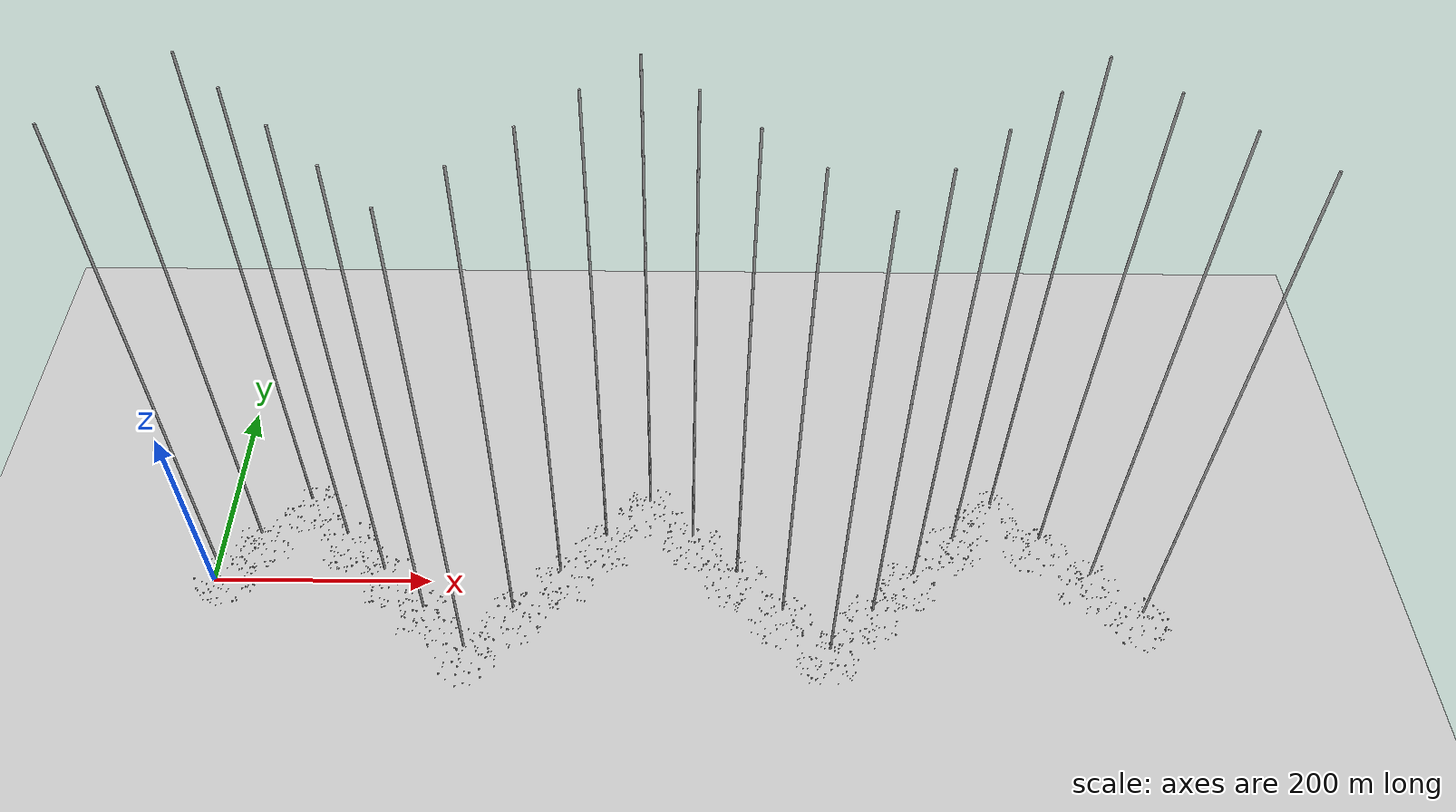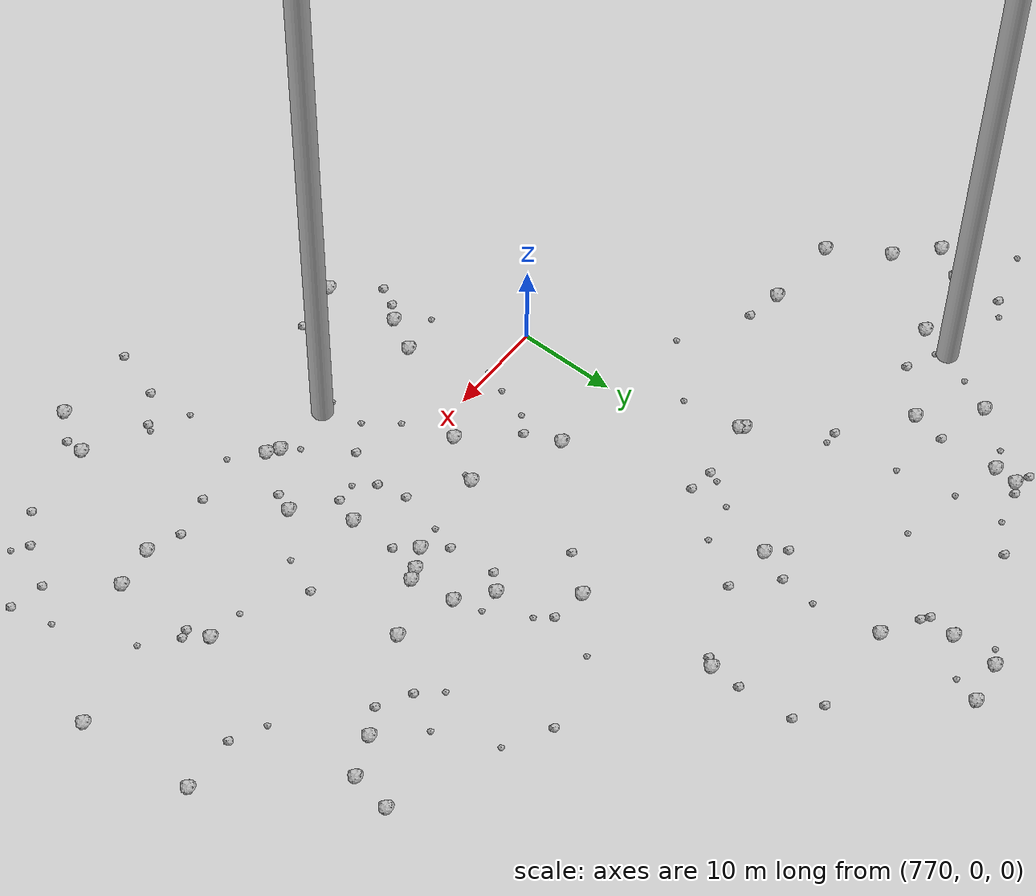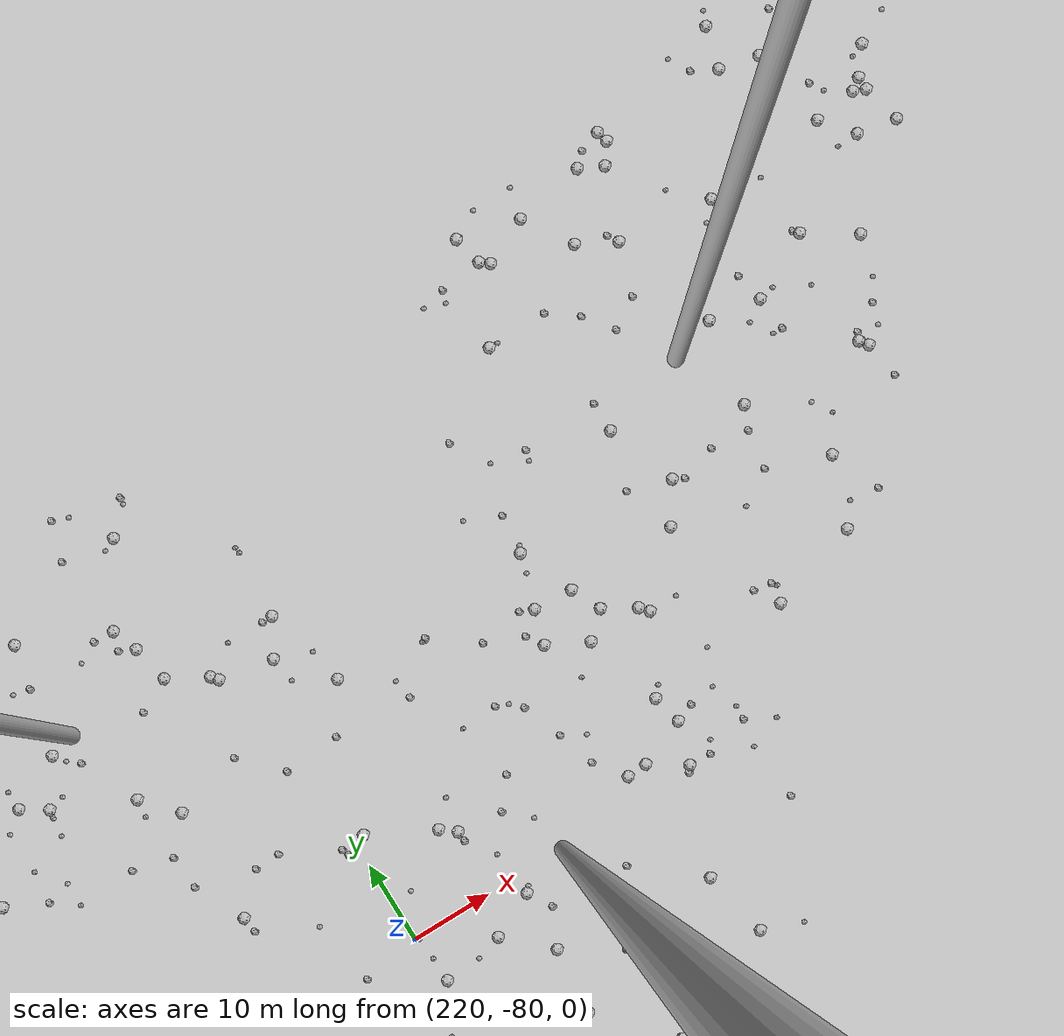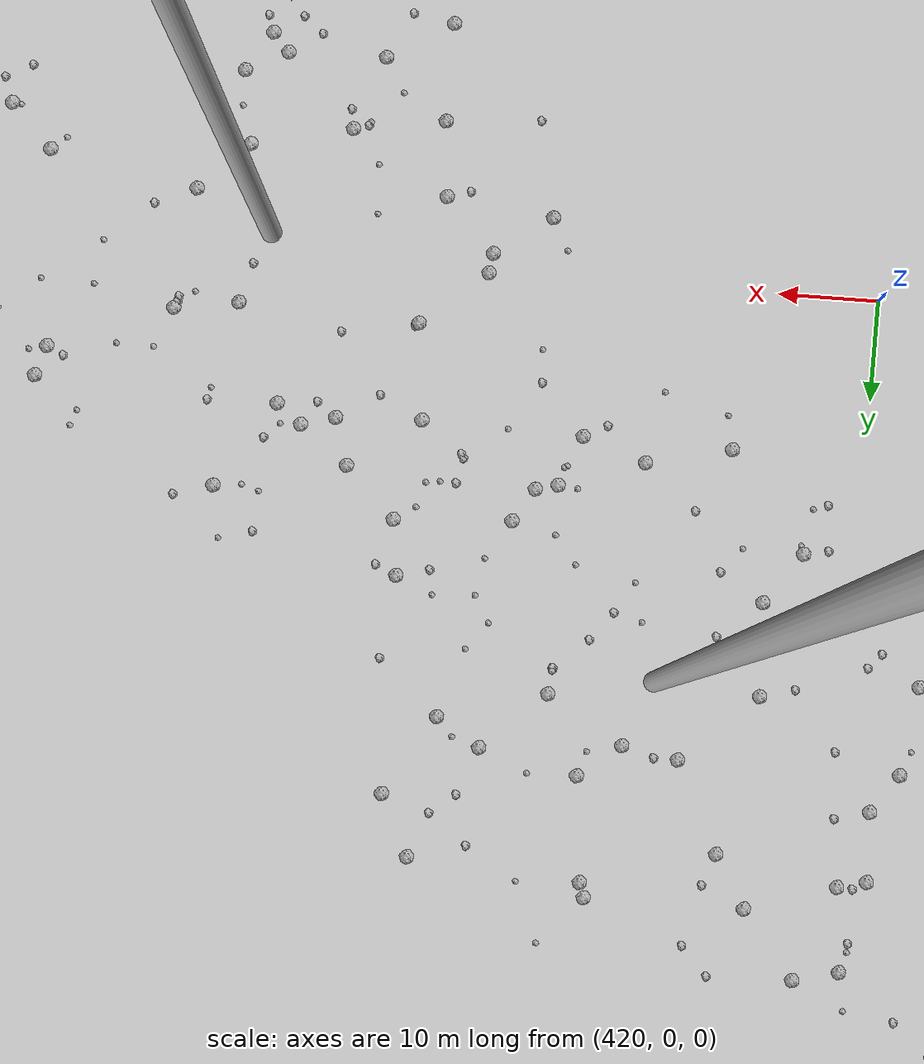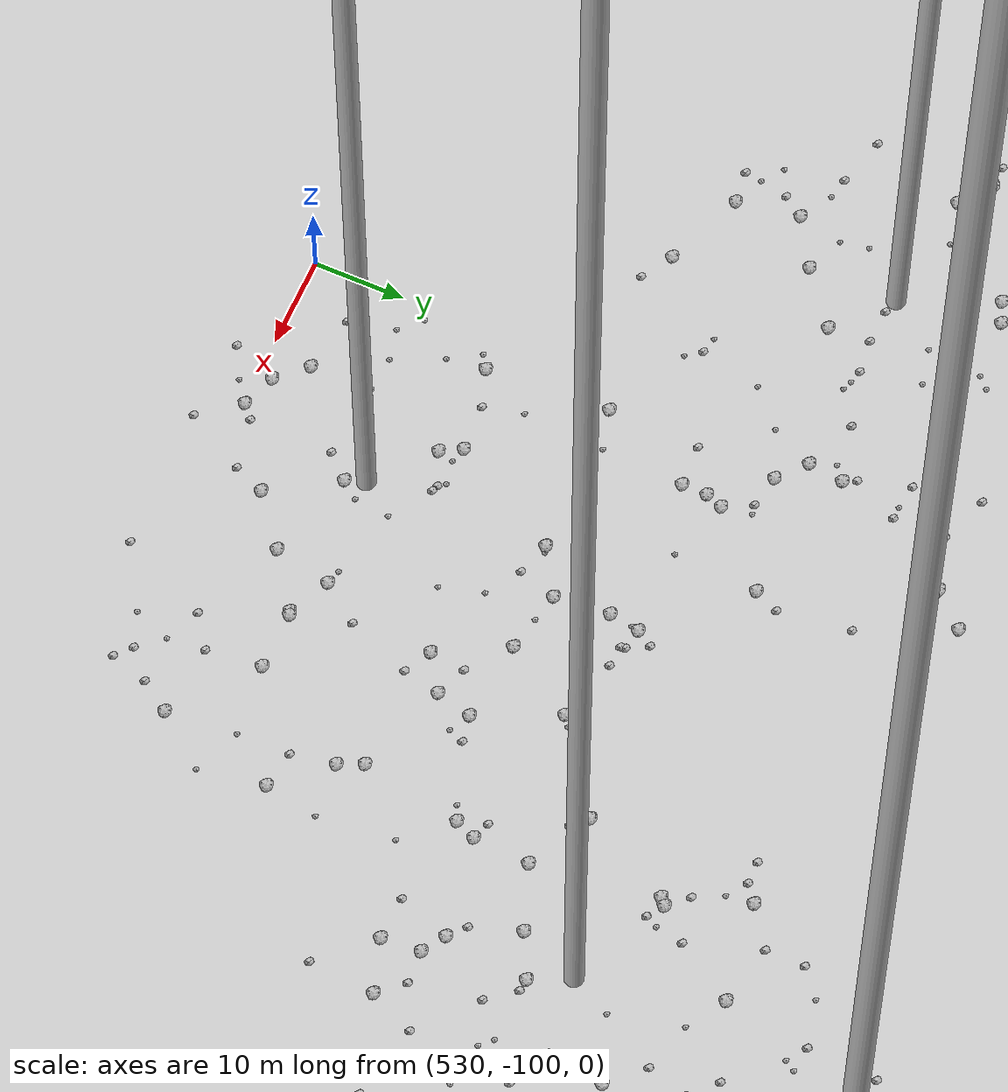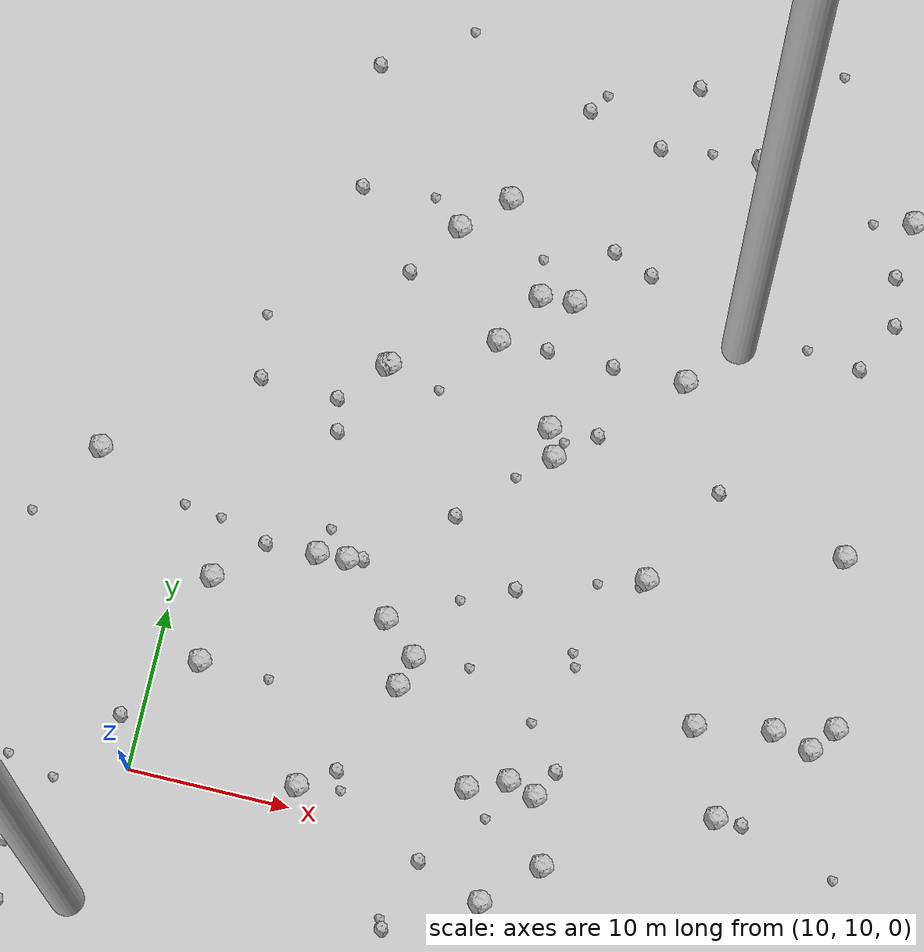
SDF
<sdf version="1.6">
 <world name="default">
  <include><uri>model://custom_ground</uri></include>
  <include><uri>model://sun</uri></include>
  <spherical_coordinates>
   <surface_model>EARTH_WGS84</surface_model>
   <latitude_deg>38.161479</latitude_deg>
   <longitude_deg>-122.454630</longitude_deg>
   <elevation>488.0</elevation>
   <heading_deg>90</heading_deg>
  </spherical_coordinates>
  <model name="rock1_0_0">
   <include><uri>model://rock1</uri><pose>-13.089091662843057 -11.832418343263008 0.5 0 0 0</pose></include>
  </model>
  <model name="rock1_0_1">
   <include><uri>model://rock1</uri><pose>-18.93702736157908 1.0147407592590199 0.5 0 0 0</pose></include>
  </model>
  <model name="rock1_0_2">
   <include><uri>model://rock1</uri><pose>-0.8347007762944791 -13.585848574019423 0.5 0 0 0</pose></include>
  </model>
  <model name="rock1_0_3">
   <include><uri>model://rock1</uri><pose>29.932797042532684 -7.243154206481332 0.5 0 0 0</pose></include>
  </model>
  <model name="rock1_0_4">
   <include><uri>model://rock1</uri><pose>-6.890203062122961 -14.525393870647296 0.5 0 0 0</pose></include>
  </model>
  <model name="rock1_0_5">
   <include><uri>model://rock1</uri><pose>32.49217723000853 14.627477199168936 0.5 0 0 0</pose></include>
  </model>
  <model name="rock1_0_6">
   <include><uri>model://rock1</uri><pose>21.43223320242025 -23.423942304812943 0.5 0 0 0</pose></include>
  </model>
  <model name="rock1_0_7">
   <include><uri>model://rock1</uri><pose>-15.017050004234143 -9.530729980270202 0.5 0 0 0</pose></include>
  </model>
  <model name="rock1_0_8">
   <include><uri>model://rock1</uri><pose>32.50418886825029 7.092666201571873 0.5 0 0 0</pose></include>
  </model>
  <model name="rock1_0_9">
   <include><uri>model://rock1</uri><pose>23.401110703666525 -19.633946964449937 0.5 0 0 0</pose></include>
  </model>
  <model name="rock1_0_10">
   <include><uri>model://rock1</uri><pose>34.248013257484665 14.088360279170779 0.5 0 0 0</pose></include>
  </model>
  <model name="rock1_0_11">
   <include><uri>model://rock1</uri><pose>27.312724513406494 -9.237385482297505 0.5 0 0 0</pose></include>
  </model>
  <model name="rock1_0_12">
   <include><uri>model://rock1</uri><pose>20.1517577268785 11.388540485116543 0.5 0 0 0</pose></include>
  </model>
  <model name="rock1_0_13">
   <include><uri>model://rock1</uri><pose>12.162409509235978 22.59898639269818 0.5 0 0 0</pose></include>
  </model>
  <model name="rock1_0_14">
   <include><uri>model://rock1</uri><pose>30.141948060873517 13.62944410867371 0.5 0 0 0</pose></include>
  </model>
  <model name="rock1_0_15">
   <include><uri>model://rock1</uri><pose>3.7012101154371955 28.74447005636494 0.5 0 0 0</pose></include>
  </model>
  <model name="rock1_0_16">
   <include><uri>model://rock1</uri><pose>12.67820393873562 17.390035511015995 0.5 0 0 0</pose></include>
  </model>
  <model name="rock1_0_17">
   <include><uri>model://rock1</uri><pose>24.660150523331048 18.70019581461927 0.5 0 0 0</pose></include>
  </model>
  <model name="rock1_0_18">
   <include><uri>model://rock1</uri><pose>-1.206696859660287 -21.885403303464663 0.5 0 0 0</pose></include>
  </model>
  <model name="rock1_0_19">
   <include><uri>model://rock1</uri><pose>0.7740740582977779 11.80666224057886 0.5 0 0 0</pose></include>
  </model>
  <model name="rock1_0_20">
   <include><uri>model://rock1</uri><pose>-7.66027476277274 22.79978689815311 0.5 0 0 0</pose></include>
  </model>
  <model name="rock1_0_21">
   <include><uri>model://rock1</uri><pose>-3.3536839200663806 10.691382111945593 0.5 0 0 0</pose></include>
  </model>
  <model name="rock1_0_22">
   <include><uri>model://rock1</uri><pose>-8.93847361363517 16.969644685988662 0.5 0 0 0</pose></include>
  </model>
  <model name="rock1_0_23">
   <include><uri>model://rock1</uri><pose>35.62070626472358 10.059102692892033 0.5 0 0 0</pose></include>
  </model>
  <model name="rock1_0_24">
   <include><uri>model://rock1</uri><pose>-15.29807296429543 -9.822260649000572 0.5 0 0 0</pose></include>
  </model>
  <model name="rock1_0_25">
   <include><uri>model://rock1</uri><pose>36.928700345798156 -5.045934607378008 0.5 0 0 0</pose></include>
  </model>
  <model name="rock1_0_26">
   <include><uri>model://rock1</uri><pose>6.801815067021341 -20.04365927238478 0.5 0 0 0</pose></include>
  </model>
  <model name="rock2_0_0">
   <include><uri>model://rock2</uri><pose>8.572947925330489 -5.2347544866569535 0.3 0 0 0</pose></include>
  </model>
  <model name="rock2_0_1">
   <include><uri>model://rock2</uri><pose>14.820319088158385 25.303114689058766 0.3 0 0 0</pose></include>
  </model>
  <model name="rock2_0_2">
   <include><uri>model://rock2</uri><pose>24.828510417500155 -22.13176590087323 0.3 0 0 0</pose></include>
  </model>
  <model name="rock2_0_3">
   <include><uri>model://rock2</uri><pose>-3.710742086907839 18.303191091329793 0.3 0 0 0</pose></include>
  </model>
  <model name="rock2_0_4">
   <include><uri>model://rock2</uri><pose>-7.334507891325327 -20.37330994851792 0.3 0 0 0</pose></include>
  </model>
  <model name="rock2_0_5">
   <include><uri>model://rock2</uri><pose>14.550998540156542 -10.01347153961084 0.3 0 0 0</pose></include>
  </model>
  <model name="rock2_0_6">
   <include><uri>model://rock2</uri><pose>3.695000222824433 4.24963126502098 0.3 0 0 0</pose></include>
  </model>
  <model name="rock2_0_7">
   <include><uri>model://rock2</uri><pose>8.777257728213637 13.129892664056399 0.3 0 0 0</pose></include>
  </model>
  <model name="rock2_0_8">
   <include><uri>model://rock2</uri><pose>1.2386333509625622 -20.84903993150591 0.3 0 0 0</pose></include>
  </model>
  <model name="rock2_0_9">
   <include><uri>model://rock2</uri><pose>-6.488197345935735 -4.613155390178996 0.3 0 0 0</pose></include>
  </model>
  <model name="rock2_0_10">
   <include><uri>model://rock2</uri><pose>11.9412992990442 -26.032302474073298 0.3 0 0 0</pose></include>
  </model>
  <model name="rock2_0_11">
   <include><uri>model://rock2</uri><pose>-9.14920212533292 12.553090238857536 0.3 0 0 0</pose></include>
  </model>
  <model name="rock2_0_12">
   <include><uri>model://rock2</uri><pose>34.884150128605725 -11.623467143645371 0.3 0 0 0</pose></include>
  </model>
  <model name="rock2_0_13">
   <include><uri>model://rock2</uri><pose>27.10915872406116 4.1577392285760695 0.3 0 0 0</pose></include>
  </model>
  <model name="rock2_0_14">
   <include><uri>model://rock2</uri><pose>-5.912899516125364 -21.528874401265057 0.3 0 0 0</pose></include>
  </model>
  <model name="rock2_0_15">
   <include><uri>model://rock2</uri><pose>31.866545633346583 -5.607914808312405 0.3 0 0 0</pose></include>
  </model>
  <model name="rock2_0_16">
   <include><uri>model://rock2</uri><pose>5.600892719301214 -8.69744728328093 0.3 0 0 0</pose></include>
  </model>
  <model name="rock2_0_17">
   <include><uri>model://rock2</uri><pose>37.71638011874665 -5.316812531203226 0.3 0 0 0</pose></include>
  </model>
  <model name="rock2_0_18">
   <include><uri>model://rock2</uri><pose>1.120975345511809 7.672495860541339 0.3 0 0 0</pose></include>
  </model>
  <model name="rock2_0_19">
   <include><uri>model://rock2</uri><pose>22.797285518925463 -22.089088277689438 0.3 0 0 0</pose></include>
  </model>
  <model name="rock2_0_20">
   <include><uri>model://rock2</uri><pose>0.5626221031082679 -7.026158543679909 0.3 0 0 0</pose></include>
  </model>
  <model name="rock2_0_21">
   <include><uri>model://rock2</uri><pose>4.187137738430447 0.5784497907685662 0.3 0 0 0</pose></include>
  </model>
  <model name="rock2_0_22">
   <include><uri>model://rock2</uri><pose>13.405258731528768 -12.981219265364448 0.3 0 0 0</pose></include>
  </model>
  <model name="rock2_0_23">
   <include><uri>model://rock2</uri><pose>28.319562353401295 8.66499649101413 0.3 0 0 0</pose></include>
  </model>
  <model name="rock2_0_24">
   <include><uri>model://rock2</uri><pose>22.258283354230947 12.839463508042627 0.3 0 0 0</pose></include>
  </model>
  <model name="rock2_0_25">
   <include><uri>model://rock2</uri><pose>-3.373290546651482 -10.632051894355016 0.3 0 0 0</pose></include>
  </model>
  <model name="rock2_0_26">
   <include><uri>model://rock2</uri><pose>35.473501248330656 -12.888903833934329 0.3 0 0 0</pose></include>
  </model>
  <model name="rock3_0_0">
   <include><uri>model://rock3</uri><pose>16.931533876584886 17.25567200103302 0.2 0 0 0</pose></include>
  </model>
  <model name="rock3_0_1">
   <include><uri>model://rock3</uri><pose>31.825411440912923 0.011909904426484985 0.2 0 0 0</pose></include>
  </model>
  <model name="rock3_0_2">
   <include><uri>model://rock3</uri><pose>28.574504500245823 20.73678743024896 0.2 0 0 0</pose></include>
  </model>
  <model name="rock3_0_3">
   <include><uri>model://rock3</uri><pose>6.230687683696981 -4.645313633200146 0.2 0 0 0</pose></include>
  </model>
  <model name="rock3_0_4">
   <include><uri>model://rock3</uri><pose>7.793366518481488 -10.014023756494929 0.2 0 0 0</pose></include>
  </model>
  <model name="rock3_0_5">
   <include><uri>model://rock3</uri><pose>-10.845762506348823 -5.4383583036962655 0.2 0 0 0</pose></include>
  </model>
  <model name="rock3_0_6">
   <include><uri>model://rock3</uri><pose>-9.520101602108689 -16.937297462095067 0.2 0 0 0</pose></include>
  </model>
  <model name="rock3_0_7">
   <include><uri>model://rock3</uri><pose>27.26444430845052 -12.994180432944432 0.2 0 0 0</pose></include>
  </model>
  <model name="rock3_0_8">
   <include><uri>model://rock3</uri><pose>7.194207568899039 -27.886507502746095 0.2 0 0 0</pose></include>
  </model>
  <model name="rock3_0_9">
   <include><uri>model://rock3</uri><pose>2.7330112445955876 9.282932225079037 0.2 0 0 0</pose></include>
  </model>
  <model name="rock3_0_10">
   <include><uri>model://rock3</uri><pose>18.463510231625577 27.055020815331936 0.2 0 0 0</pose></include>
  </model>
  <model name="rock3_0_11">
   <include><uri>model://rock3</uri><pose>22.752887886501107 11.69158213434821 0.2 0 0 0</pose></include>
  </model>
  <model name="rock3_0_12">
   <include><uri>model://rock3</uri><pose>27.06526833877404 24.634757626212647 0.2 0 0 0</pose></include>
  </model>
  <model name="rock3_0_13">
   <include><uri>model://rock3</uri><pose>5.710638455633436 8.490625148320362 0.2 0 0 0</pose></include>
  </model>
  <model name="rock3_0_14">
   <include><uri>model://rock3</uri><pose>26.83879690595238 4.7121596038460325 0.2 0 0 0</pose></include>
  </model>
  <model name="rock3_0_15">
   <include><uri>model://rock3</uri><pose>-9.966309850764645 -18.39215791586532 0.2 0 0 0</pose></include>
  </model>
  <model name="rock3_0_16">
   <include><uri>model://rock3</uri><pose>0.5356249415745253 24.00806350851264 0.2 0 0 0</pose></include>
  </model>
  <model name="rock3_0_17">
   <include><uri>model://rock3</uri><pose>12.55910108221191 -21.194325950846878 0.2 0 0 0</pose></include>
  </model>
  <model name="rock3_0_18">
   <include><uri>model://rock3</uri><pose>9.477032303760112 26.48734677322974 0.2 0 0 0</pose></include>
  </model>
  <model name="rock3_0_19">
   <include><uri>model://rock3</uri><pose>4.294171187896513 -13.799032937047862 0.2 0 0 0</pose></include>
  </model>
  <model name="rock3_0_20">
   <include><uri>model://rock3</uri><pose>-12.679329613058094 -9.256017401662902 0.2 0 0 0</pose></include>
  </model>
  <model name="rock3_0_21">
   <include><uri>model://rock3</uri><pose>31.76646896939699 -7.7669411468211464 0.2 0 0 0</pose></include>
  </model>
  <model name="rock3_0_22">
   <include><uri>model://rock3</uri><pose>-4.98264709451875 9.833356700938651 0.2 0 0 0</pose></include>
  </model>
  <model name="rock3_0_23">
   <include><uri>model://rock3</uri><pose>-11.952515507507542 19.266412201356843 0.2 0 0 0</pose></include>
  </model>
  <model name="rock3_0_24">
   <include><uri>model://rock3</uri><pose>-11.02159634805937 -2.015564673553449 0.2 0 0 0</pose></include>
  </model>
  <model name="rock3_0_25">
   <include><uri>model://rock3</uri><pose>1.3887277143086934 -24.537097258358116 0.2 0 0 0</pose></include>
  </model>
  <model name="rock3_0_26">
   <include><uri>model://rock3</uri><pose>11.805537333664404 26.200837390794028 0.2 0 0 0</pose></include>
  </model>
  <model name="rock1_1_0">
   <include><uri>model://rock1</uri><pose>25.164208618531752 20.611626476507514 0.5 0 0 0</pose></include>
  </model>
  <model name="rock1_1_1">
   <include><uri>model://rock1</uri><pose>42.62200607511218 20.467557550972884 0.5 0 0 0</pose></include>
  </model>
  <model name="rock1_1_2">
   <include><uri>model://rock1</uri><pose>37.34323781105824 40.84252806440378 0.5 0 0 0</pose></include>
  </model>
  <model name="rock1_1_3">
   <include><uri>model://rock1</uri><pose>55.563168571205175 43.796890720755584 0.5 0 0 0</pose></include>
  </model>
  <model name="rock1_1_4">
   <include><uri>model://rock1</uri><pose>18.028743515858842 25.427755572156887 0.5 0 0 0</pose></include>
  </model>
  <model name="rock1_1_5">
   <include><uri>model://rock1</uri><pose>38.8472644086359 55.328901722158214 0.5 0 0 0</pose></include>
  </model>
  <model name="rock1_1_6">
   <include><uri>model://rock1</uri><pose>27.521162641143377 43.96336015442737 0.5 0 0 0</pose></include>
  </model>
  <model name="rock1_1_7">
   <include><uri>model://rock1</uri><pose>60.054095019182874 59.803753120712365 0.5 0 0 0</pose></include>
  </model>
  <model name="rock1_1_8">
   <include><uri>model://rock1</uri><pose>48.701448631045025 53.67549086831864 0.5 0 0 0</pose></include>
  </model>
  <model name="rock1_1_9">
   <include><uri>model://rock1</uri><pose>19.561622886000727 37.75484052810164 0.5 0 0 0</pose></include>
  </model>
  <model name="rock1_1_10">
   <include><uri>model://rock1</uri><pose>30.610344468626884 34.49658260321752 0.5 0 0 0</pose></include>
  </model>
  <model name="rock1_1_11">
   <include><uri>model://rock1</uri><pose>49.765583690220396 20.656554389471328 0.5 0 0 0</pose></include>
  </model>
  <model name="rock1_1_12">
   <include><uri>model://rock1</uri><pose>29.939391374466418 36.18016653954707 0.5 0 0 0</pose></include>
  </model>
  <model name="rock1_1_13">
   <include><uri>model://rock1</uri><pose>21.753237513493552 47.021493906929315 0.5 0 0 0</pose></include>
  </model>
  <model name="rock1_1_14">
   <include><uri>model://rock1</uri><pose>37.811276732280135 28.481586810032162 0.5 0 0 0</pose></include>
  </model>
  <model name="rock1_1_15">
   <include><uri>model://rock1</uri><pose>24.37925225677027 49.45079193333062 0.5 0 0 0</pose></include>
  </model>
  <model name="rock1_1_16">
   <include><uri>model://rock1</uri><pose>59.94571078218114 41.88931001395699 0.5 0 0 0</pose></include>
  </model>
  <model name="rock1_1_17">
   <include><uri>model://rock1</uri><pose>49.1635714577034 32.57695353786991 0.5 0 0 0</pose></include>
  </model>
  <model name="rock1_1_18">
   <include><uri>model://rock1</uri><pose>48.95272196047452 60.88589079602264 0.5 0 0 0</pose></include>
  </model>
  <model name="rock1_1_19">
   <include><uri>model://rock1</uri><pose>19.8722924742288 25.529243723560967 0.5 0 0 0</pose></include>
  </model>
  <model name="rock1_1_20">
   <include><uri>model://rock1</uri><pose>23.02070138961458 22.50769622536214 0.5 0 0 0</pose></include>
  </model>
  <model name="rock1_1_21">
   <include><uri>model://rock1</uri><pose>47.3285066836494 21.303498614550175 0.5 0 0 0</pose></include>
  </model>
  <model name="rock1_1_22">
   <include><uri>model://rock1</uri><pose>19.43626360816928 37.670072434769 0.5 0 0 0</pose></include>
  </model>
  <model name="rock1_1_23">
   <include><uri>model://rock1</uri><pose>45.14467273249937 15.315497185561728 0.5 0 0 0</pose></include>
  </model>
  <model name="rock1_1_24">
   <include><uri>model://rock1</uri><pose>29.630532291783414 44.09639892296601 0.5 0 0 0</pose></include>
  </model>
  <model name="rock1_1_25">
   <include><uri>model://rock1</uri><pose>25.681641473313917 40.711900536662185 0.5 0 0 0</pose></include>
  </model>
  <model name="rock1_1_26">
   <include><uri>model://rock1</uri><pose>50.978201331031535 22.243770469147535 0.5 0 0 0</pose></include>
  </model>
  <model name="rock2_1_0">
   <include><uri>model://rock2</uri><pose>19.40690080596232 43.62240127142638 0.3 0 0 0</pose></include>
  </model>
  <model name="rock2_1_1">
   <include><uri>model://rock2</uri><pose>14.651454273569083 55.76389399903717 0.3 0 0 0</pose></include>
  </model>
  <model name="rock2_1_2">
   <include><uri>model://rock2</uri><pose>40.842950959263845 34.676633943103056 0.3 0 0 0</pose></include>
  </model>
  <model name="rock2_1_3">
   <include><uri>model://rock2</uri><pose>16.950351887107068 34.98137777145125 0.3 0 0 0</pose></include>
  </model>
  <model name="rock2_1_4">
   <include><uri>model://rock2</uri><pose>33.78921250778137 46.79269650224436 0.3 0 0 0</pose></include>
  </model>
  <model name="rock2_1_5">
   <include><uri>model://rock2</uri><pose>34.045418969777955 58.878353449458515 0.3 0 0 0</pose></include>
  </model>
  <model name="rock2_1_6">
   <include><uri>model://rock2</uri><pose>48.92718752336341 47.18479631967429 0.3 0 0 0</pose></include>
  </model>
  <model name="rock2_1_7">
   <include><uri>model://rock2</uri><pose>32.893676533319315 36.38176778696919 0.3 0 0 0</pose></include>
  </model>
  <model name="rock2_1_8">
   <include><uri>model://rock2</uri><pose>46.723660220431505 15.246996007243636 0.3 0 0 0</pose></include>
  </model>
  <model name="rock2_1_9">
   <include><uri>model://rock2</uri><pose>25.611801636121164 29.604486748948005 0.3 0 0 0</pose></include>
  </model>
  <model name="rock2_1_10">
   <include><uri>model://rock2</uri><pose>15.361617431438845 48.118548422077225 0.3 0 0 0</pose></include>
  </model>
  <model name="rock2_1_11">
   <include><uri>model://rock2</uri><pose>32.82017549273918 40.73562372248908 0.3 0 0 0</pose></include>
  </model>
  <model name="rock2_1_12">
   <include><uri>model://rock2</uri><pose>48.305421157056486 50.133364000004214 0.3 0 0 0</pose></include>
  </model>
  <model name="rock2_1_13">
   <include><uri>model://rock2</uri><pose>17.42534494591717 32.99822953279171 0.3 0 0 0</pose></include>
  </model>
  <model name="rock2_1_14">
   <include><uri>model://rock2</uri><pose>12.134144362609284 35.142202794168156 0.3 0 0 0</pose></include>
  </model>
  <model name="rock2_1_15">
   <include><uri>model://rock2</uri><pose>27.817388989708967 55.93418316717598 0.3 0 0 0</pose></include>
  </model>
  <model name="rock2_1_16">
   <include><uri>model://rock2</uri><pose>35.10892697097328 15.817813799468984 0.3 0 0 0</pose></include>
  </model>
  <model name="rock2_1_17">
   <include><uri>model://rock2</uri><pose>20.75516138531282 25.70215157049655 0.3 0 0 0</pose></include>
  </model>
  <model name="rock2_1_18">
   <include><uri>model://rock2</uri><pose>32.54625602323835 54.6500638954219 0.3 0 0 0</pose></include>
  </model>
  <model name="rock2_1_19">
   <include><uri>model://rock2</uri><pose>47.44078467907472 44.06113640392969 0.3 0 0 0</pose></include>
  </model>
  <model name="rock2_1_20">
   <include><uri>model://rock2</uri><pose>58.63999430657951 46.019814004013185 0.3 0 0 0</pose></include>
  </model>
  <model name="rock2_1_21">
   <include><uri>model://rock2</uri><pose>31.281268800458065 47.70704496585908 0.3 0 0 0</pose></include>
  </model>
  <model name="rock2_1_22">
   <include><uri>model://rock2</uri><pose>65.56363039681437 35.04018168602012 0.3 0 0 0</pose></include>
  </model>
  <model name="rock2_1_23">
   <include><uri>model://rock2</uri><pose>28.702117526204415 40.8006929970371 0.3 0 0 0</pose></include>
  </model>
  <model name="rock2_1_24">
   <include><uri>model://rock2</uri><pose>57.47210588943151 29.51541516878632 0.3 0 0 0</pose></include>
  </model>
  <model name="rock2_1_25">
   <include><uri>model://rock2</uri><pose>58.5417757893181 32.082458199326695 0.3 0 0 0</pose></include>
  </model>
  <model name="rock2_1_26">
   <include><uri>model://rock2</uri><pose>30.194010388474236 26.056863709585315 0.3 0 0 0</pose></include>
  </model>
  <model name="rock3_1_0">
   <include><uri>model://rock3</uri><pose>19.79897049634187 59.10370059638295 0.2 0 0 0</pose></include>
  </model>
  <model name="rock3_1_1">
   <include><uri>model://rock3</uri><pose>33.68015753727569 69.31265681498928 0.2 0 0 0</pose></include>
  </model>
  <model name="rock3_1_2">
   <include><uri>model://rock3</uri><pose>22.81961005378477 36.8917452245131 0.2 0 0 0</pose></include>
  </model>
  <model name="rock3_1_3">
   <include><uri>model://rock3</uri><pose>44.08201987111666 68.87792447944669 0.2 0 0 0</pose></include>
  </model>
  <model name="rock3_1_4">
   <include><uri>model://rock3</uri><pose>60.666364477649566 30.189020920231474 0.2 0 0 0</pose></include>
  </model>
  <model name="rock3_1_5">
   <include><uri>model://rock3</uri><pose>27.145544476961362 46.228358380305814 0.2 0 0 0</pose></include>
  </model>
  <model name="rock3_1_6">
   <include><uri>model://rock3</uri><pose>34.77844678193338 22.257826154307494 0.2 0 0 0</pose></include>
  </model>
  <model name="rock3_1_7">
   <include><uri>model://rock3</uri><pose>52.804807925413066 13.261155689543765 0.2 0 0 0</pose></include>
  </model>
  <model name="rock3_1_8">
   <include><uri>model://rock3</uri><pose>46.22948690743457 53.044615357871216 0.2 0 0 0</pose></include>
  </model>
  <model name="rock3_1_9">
   <include><uri>model://rock3</uri><pose>63.77034087967071 32.71886749632685 0.2 0 0 0</pose></include>
  </model>
  <model name="rock3_1_10">
   <include><uri>model://rock3</uri><pose>34.931629883085265 27.53306785320425 0.2 0 0 0</pose></include>
  </model>
  <model name="rock3_1_11">
   <include><uri>model://rock3</uri><pose>40.608616297064685 56.31772703619467 0.2 0 0 0</pose></include>
  </model>
  <model name="rock3_1_12">
   <include><uri>model://rock3</uri><pose>28.61159067754545 32.728100520583695 0.2 0 0 0</pose></include>
  </model>
  <model name="rock3_1_13">
   <include><uri>model://rock3</uri><pose>60.429888343733325 39.60852599899833 0.2 0 0 0</pose></include>
  </model>
  <model name="rock3_1_14">
   <include><uri>model://rock3</uri><pose>59.58473298147701 42.828110661572865 0.2 0 0 0</pose></include>
  </model>
  <model name="rock3_1_15">
   <include><uri>model://rock3</uri><pose>42.4801986871672 61.590474091319805 0.2 0 0 0</pose></include>
  </model>
  <model name="rock3_1_16">
   <include><uri>model://rock3</uri><pose>35.68915990181516 55.039603268604836 0.2 0 0 0</pose></include>
  </model>
  <model name="rock3_1_17">
   <include><uri>model://rock3</uri><pose>34.45605711520441 23.07723393448241 0.2 0 0 0</pose></include>
  </model>
  <model name="rock3_1_18">
   <include><uri>model://rock3</uri><pose>11.550198635798946 39.026908071715 0.2 0 0 0</pose></include>
  </model>
  <model name="rock3_1_19">
   <include><uri>model://rock3</uri><pose>30.974986223937776 35.49471464470443 0.2 0 0 0</pose></include>
  </model>
  <model name="rock3_1_20">
   <include><uri>model://rock3</uri><pose>31.62290531363738 12.052472688376062 0.2 0 0 0</pose></include>
  </model>
  <model name="rock3_1_21">
   <include><uri>model://rock3</uri><pose>62.98755230990609 24.938524304393187 0.2 0 0 0</pose></include>
  </model>
  <model name="rock3_1_22">
   <include><uri>model://rock3</uri><pose>37.48479513489558 27.91498727745306 0.2 0 0 0</pose></include>
  </model>
  <model name="rock3_1_23">
   <include><uri>model://rock3</uri><pose>32.989304060152634 18.3541376605711 0.2 0 0 0</pose></include>
  </model>
  <model name="rock3_1_24">
   <include><uri>model://rock3</uri><pose>44.06843623208331 44.477212447099674 0.2 0 0 0</pose></include>
  </model>
  <model name="rock3_1_25">
   <include><uri>model://rock3</uri><pose>19.839689413315085 48.46415610402494 0.2 0 0 0</pose></include>
  </model>
  <model name="rock3_1_26">
   <include><uri>model://rock3</uri><pose>28.62870762280121 57.08425056905081 0.2 0 0 0</pose></include>
  </model>
  <model name="rock1_2_0">
   <include><uri>model://rock1</uri><pose>63.60328339228721 72.24983565523169 0.5 0 0 0</pose></include>
  </model>
  <model name="rock1_2_1">
   <include><uri>model://rock1</uri><pose>50.624278954497 77.05944333967376 0.5 0 0 0</pose></include>
  </model>
  <model name="rock1_2_2">
   <include><uri>model://rock1</uri><pose>65.33871627250979 59.445664893014545 0.5 0 0 0</pose></include>
  </model>
  <model name="rock1_2_3">
   <include><uri>model://rock1</uri><pose>52.526725435732835 82.11709796532224 0.5 0 0 0</pose></include>
  </model>
  <model name="rock1_2_4">
   <include><uri>model://rock1</uri><pose>80.45698482232163 68.44754191449958 0.5 0 0 0</pose></include>
  </model>
  <model name="rock1_2_5">
   <include><uri>model://rock1</uri><pose>87.18917965658002 104.94641334778768 0.5 0 0 0</pose></include>
  </model>
  <model name="rock1_2_6">
   <include><uri>model://rock1</uri><pose>62.82198343698823 84.96657975719555 0.5 0 0 0</pose></include>
  </model>
  <model name="rock1_2_7">
   <include><uri>model://rock1</uri><pose>57.079850183279135 82.31758459279199 0.5 0 0 0</pose></include>
  </model>
  <model name="rock1_2_8">
   <include><uri>model://rock1</uri><pose>84.94466300401564 105.17981134119307 0.5 0 0 0</pose></include>
  </model>
  <model name="rock1_2_9">
   <include><uri>model://rock1</uri><pose>66.92452020981112 72.33823903721456 0.5 0 0 0</pose></include>
  </model>
  <model name="rock1_2_10">
   <include><uri>model://rock1</uri><pose>51.58530933957257 74.54373301163983 0.5 0 0 0</pose></include>
  </model>
  <model name="rock1_2_11">
   <include><uri>model://rock1</uri><pose>64.00829106411727 85.4118525203173 0.5 0 0 0</pose></include>
  </model>
  <model name="rock1_2_12">
   <include><uri>model://rock1</uri><pose>102.52401807730271 70.0564338931144 0.5 0 0 0</pose></include>
  </model>
  <model name="rock1_2_13">
   <include><uri>model://rock1</uri><pose>87.11604239926305 108.60181416050276 0.5 0 0 0</pose></include>
  </model>
  <model name="rock1_2_14">
   <include><uri>model://rock1</uri><pose>77.780328801062 91.70468321153035 0.5 0 0 0</pose></include>
  </model>
  <model name="rock1_2_15">
   <include><uri>model://rock1</uri><pose>90.49476133708737 69.29406332661668 0.5 0 0 0</pose></include>
  </model>
  <model name="rock1_2_16">
   <include><uri>model://rock1</uri><pose>87.49518857242117 61.2862226865655 0.5 0 0 0</pose></include>
  </model>
  <model name="rock1_2_17">
   <include><uri>model://rock1</uri><pose>77.89723375527038 65.67830646010029 0.5 0 0 0</pose></include>
  </model>
  <model name="rock1_2_18">
   <include><uri>model://rock1</uri><pose>102.03600899165292 73.94737684363218 0.5 0 0 0</pose></include>
  </model>
  <model name="rock1_2_19">
   <include><uri>model://rock1</uri><pose>75.54309923604173 106.94178158155258 0.5 0 0 0</pose></include>
  </model>
  <model name="rock1_2_20">
   <include><uri>model://rock1</uri><pose>75.72748096071165 86.30228659751035 0.5 0 0 0</pose></include>
  </model>
  <model name="rock1_2_21">
   <include><uri>model://rock1</uri><pose>85.27329042276217 93.48804885625054 0.5 0 0 0</pose></include>
  </model>
  <model name="rock1_2_22">
   <include><uri>model://rock1</uri><pose>75.65905615551938 87.46483279033565 0.5 0 0 0</pose></include>
  </model>
  <model name="rock1_2_23">
   <include><uri>model://rock1</uri><pose>89.92222884202116 96.78135446505823 0.5 0 0 0</pose></include>
  </model>
  <model name="rock1_2_24">
   <include><uri>model://rock1</uri><pose>85.97787432274026 98.74100661931325 0.5 0 0 0</pose></include>
  </model>
  <model name="rock1_2_25">
   <include><uri>model://rock1</uri><pose>89.066995163022 96.44863860079519 0.5 0 0 0</pose></include>
  </model>
  <model name="rock1_2_26">
   <include><uri>model://rock1</uri><pose>95.0653172399495 69.36630782797052 0.5 0 0 0</pose></include>
  </model>
  <model name="rock2_2_0">
   <include><uri>model://rock2</uri><pose>83.79179628975649 74.63317676975299 0.3 0 0 0</pose></include>
  </model>
  <model name="rock2_2_1">
   <include><uri>model://rock2</uri><pose>70.08355714355335 68.15921545948977 0.3 0 0 0</pose></include>
  </model>
  <model name="rock2_2_2">
   <include><uri>model://rock2</uri><pose>67.587074212239 55.02773044287877 0.3 0 0 0</pose></include>
  </model>
  <model name="rock2_2_3">
   <include><uri>model://rock2</uri><pose>80.62093688541354 86.46728530354585 0.3 0 0 0</pose></include>
  </model>
  <model name="rock2_2_4">
   <include><uri>model://rock2</uri><pose>81.0070662307574 62.69074176389694 0.3 0 0 0</pose></include>
  </model>
  <model name="rock2_2_5">
   <include><uri>model://rock2</uri><pose>73.38697308600392 85.80399589004574 0.3 0 0 0</pose></include>
  </model>
  <model name="rock2_2_6">
   <include><uri>model://rock2</uri><pose>89.32349862093787 97.31806891585735 0.3 0 0 0</pose></include>
  </model>
  <model name="rock2_2_7">
   <include><uri>model://rock2</uri><pose>92.80874338694744 96.06382923985458 0.3 0 0 0</pose></include>
  </model>
  <model name="rock2_2_8">
   <include><uri>model://rock2</uri><pose>93.28264292859413 99.94861579183504 0.3 0 0 0</pose></include>
  </model>
  <model name="rock2_2_9">
   <include><uri>model://rock2</uri><pose>105.22166976545054 76.57909836588595 0.3 0 0 0</pose></include>
  </model>
  <model name="rock2_2_10">
   <include><uri>model://rock2</uri><pose>62.24506738130141 72.5677258450256 0.3 0 0 0</pose></include>
  </model>
  <model name="rock2_2_11">
   <include><uri>model://rock2</uri><pose>55.68869639932934 74.992270698714 0.3 0 0 0</pose></include>
  </model>
  <model name="rock2_2_12">
   <include><uri>model://rock2</uri><pose>95.80880810313964 99.00255971010964 0.3 0 0 0</pose></include>
  </model>
  <model name="rock2_2_13">
   <include><uri>model://rock2</uri><pose>65.33952568348253 92.13835634655045 0.3 0 0 0</pose></include>
  </model>
  <model name="rock2_2_14">
   <include><uri>model://rock2</uri><pose>89.89408894624279 84.90358270083817 0.3 0 0 0</pose></include>
  </model>
  <model name="rock2_2_15">
   <include><uri>model://rock2</uri><pose>82.42700839287923 80.59674679944669 0.3 0 0 0</pose></include>
  </model>
  <model name="rock2_2_16">
   <include><uri>model://rock2</uri><pose>67.45374089512993 85.95357333870206 0.3 0 0 0</pose></include>
  </model>
  <model name="rock2_2_17">
   <include><uri>model://rock2</uri><pose>87.7748009719298 67.9288010010622 0.3 0 0 0</pose></include>
  </model>
  <model name="rock2_2_18">
   <include><uri>model://rock2</uri><pose>71.66911255521413 107.29334909236923 0.3 0 0 0</pose></include>
  </model>
  <model name="rock2_2_19">
   <include><uri>model://rock2</uri><pose>96.55918692900173 76.5991581362888 0.3 0 0 0</pose></include>
  </model>
  <model name="rock2_2_20">
   <include><uri>model://rock2</uri><pose>83.81637998631172 75.42687650809086 0.3 0 0 0</pose></include>
  </model>
  <model name="rock2_2_21">
   <include><uri>model://rock2</uri><pose>57.608628073310285 63.75286130680264 0.3 0 0 0</pose></include>
  </model>
  <model name="rock2_2_22">
   <include><uri>model://rock2</uri><pose>58.702849537340896 79.69338950741349 0.3 0 0 0</pose></include>
  </model>
  <model name="rock2_2_23">
   <include><uri>model://rock2</uri><pose>102.11314336372627 86.01491026045358 0.3 0 0 0</pose></include>
  </model>
  <model name="rock2_2_24">
   <include><uri>model://rock2</uri><pose>89.09778250333383 63.638267595892295 0.3 0 0 0</pose></include>
  </model>
  <model name="rock2_2_25">
   <include><uri>model://rock2</uri><pose>106.99198329853445 87.04560334490593 0.3 0 0 0</pose></include>
  </model>
  <model name="rock2_2_26">
   <include><uri>model://rock2</uri><pose>81.49002622752393 59.40863904403225 0.3 0 0 0</pose></include>
  </model>
  <model name="rock3_2_0">
   <include><uri>model://rock3</uri><pose>96.85439617410739 88.82756329986887 0.2 0 0 0</pose></include>
  </model>
  <model name="rock3_2_1">
   <include><uri>model://rock3</uri><pose>87.55821641892032 87.36873192727433 0.2 0 0 0</pose></include>
  </model>
  <model name="rock3_2_2">
   <include><uri>model://rock3</uri><pose>104.44828594120071 70.37606813814341 0.2 0 0 0</pose></include>
  </model>
  <model name="rock3_2_3">
   <include><uri>model://rock3</uri><pose>76.6936817132079 57.6821849191255 0.2 0 0 0</pose></include>
  </model>
  <model name="rock3_2_4">
   <include><uri>model://rock3</uri><pose>104.81448435501629 82.90475913620233 0.2 0 0 0</pose></include>
  </model>
  <model name="rock3_2_5">
   <include><uri>model://rock3</uri><pose>95.66180191325823 57.52697993315156 0.2 0 0 0</pose></include>
  </model>
  <model name="rock3_2_6">
   <include><uri>model://rock3</uri><pose>73.89631141209028 57.86525703671324 0.2 0 0 0</pose></include>
  </model>
  <model name="rock3_2_7">
   <include><uri>model://rock3</uri><pose>70.1552086162219 58.12868339601563 0.2 0 0 0</pose></include>
  </model>
  <model name="rock3_2_8">
   <include><uri>model://rock3</uri><pose>83.08017783473949 79.53718585857285 0.2 0 0 0</pose></include>
  </model>
  <model name="rock3_2_9">
   <include><uri>model://rock3</uri><pose>77.57381730863379 74.97507940617577 0.2 0 0 0</pose></include>
  </model>
  <model name="rock3_2_10">
   <include><uri>model://rock3</uri><pose>102.42282146280986 95.05491971223223 0.2 0 0 0</pose></include>
  </model>
  <model name="rock3_2_11">
   <include><uri>model://rock3</uri><pose>101.93637479853781 94.83644009144945 0.2 0 0 0</pose></include>
  </model>
  <model name="rock3_2_12">
   <include><uri>model://rock3</uri><pose>71.71380010759248 94.83496156114225 0.2 0 0 0</pose></include>
  </model>
  <model name="rock3_2_13">
   <include><uri>model://rock3</uri><pose>96.41189563175524 57.98756438830852 0.2 0 0 0</pose></include>
  </model>
  <model name="rock3_2_14">
   <include><uri>model://rock3</uri><pose>57.633148329594604 95.59959706708055 0.2 0 0 0</pose></include>
  </model>
  <model name="rock3_2_15">
   <include><uri>model://rock3</uri><pose>63.867062015028054 104.98254961335766 0.2 0 0 0</pose></include>
  </model>
  <model name="rock3_2_16">
   <include><uri>model://rock3</uri><pose>90.94864151926099 87.4098177160131 0.2 0 0 0</pose></include>
  </model>
  <model name="rock3_2_17">
   <include><uri>model://rock3</uri><pose>69.7954996445894 56.10598034784217 0.2 0 0 0</pose></include>
  </model>
  <model name="rock3_2_18">
   <include><uri>model://rock3</uri><pose>99.20431113201899 86.33180568419297 0.2 0 0 0</pose></include>
  </model>
  <model name="rock3_2_19">
   <include><uri>model://rock3</uri><pose>79.52493911182808 67.14689004678526 0.2 0 0 0</pose></include>
  </model>
  <model name="rock3_2_20">
   <include><uri>model://rock3</uri><pose>56.85832422234839 93.58108148681654 0.2 0 0 0</pose></include>
  </model>
  <model name="rock3_2_21">
   <include><uri>model://rock3</uri><pose>58.06454115999667 72.64820365608692 0.2 0 0 0</pose></include>
  </model>
  <model name="rock3_2_22">
   <include><uri>model://rock3</uri><pose>58.24099228670934 89.23369531776265 0.2 0 0 0</pose></include>
  </model>
  <model name="rock3_2_23">
   <include><uri>model://rock3</uri><pose>101.4775575256777 60.34958854036 0.2 0 0 0</pose></include>
  </model>
  <model name="rock3_2_24">
   <include><uri>model://rock3</uri><pose>92.95248699358332 67.1605283420493 0.2 0 0 0</pose></include>
  </model>
  <model name="rock3_2_25">
   <include><uri>model://rock3</uri><pose>85.70312147236027 107.08372255686656 0.2 0 0 0</pose></include>
  </model>
  <model name="rock3_2_26">
   <include><uri>model://rock3</uri><pose>68.08957626277501 73.19629614262512 0.2 0 0 0</pose></include>
  </model>
  <model name="rock1_3_0">
   <include><uri>model://rock1</uri><pose>127.56228739528896 20.654450056418746 0.5 0 0 0</pose></include>
  </model>
  <model name="rock1_3_1">
   <include><uri>model://rock1</uri><pose>149.23931035788866 37.711764910125346 0.5 0 0 0</pose></include>
  </model>
  <model name="rock1_3_2">
   <include><uri>model://rock1</uri><pose>121.53783171505357 24.994861150926866 0.5 0 0 0</pose></include>
  </model>
  <model name="rock1_3_3">
   <include><uri>model://rock1</uri><pose>140.51860007354878 47.00015098439757 0.5 0 0 0</pose></include>
  </model>
  <model name="rock1_3_4">
   <include><uri>model://rock1</uri><pose>97.52591160750053 52.11975464476116 0.5 0 0 0</pose></include>
  </model>
  <model name="rock1_3_5">
   <include><uri>model://rock1</uri><pose>112.40196407350203 13.150031091957388 0.5 0 0 0</pose></include>
  </model>
  <model name="rock1_3_6">
   <include><uri>model://rock1</uri><pose>117.89912167981163 34.24011449716248 0.5 0 0 0</pose></include>
  </model>
  <model name="rock1_3_7">
   <include><uri>model://rock1</uri><pose>104.10156218500289 19.64950008622567 0.5 0 0 0</pose></include>
  </model>
  <model name="rock1_3_8">
   <include><uri>model://rock1</uri><pose>96.89724638957752 22.795107009232577 0.5 0 0 0</pose></include>
  </model>
  <model name="rock1_3_9">
   <include><uri>model://rock1</uri><pose>111.99702597667317 28.201700727359984 0.5 0 0 0</pose></include>
  </model>
  <model name="rock1_3_10">
   <include><uri>model://rock1</uri><pose>124.21603127997025 65.62443405857147 0.5 0 0 0</pose></include>
  </model>
  <model name="rock1_3_11">
   <include><uri>model://rock1</uri><pose>109.1821530298518 20.306698707046905 0.5 0 0 0</pose></include>
  </model>
  <model name="rock1_3_12">
   <include><uri>model://rock1</uri><pose>92.67210563794718 51.304691399360145 0.5 0 0 0</pose></include>
  </model>
  <model name="rock1_3_13">
   <include><uri>model://rock1</uri><pose>124.19478645811482 16.36707440188699 0.5 0 0 0</pose></include>
  </model>
  <model name="rock1_3_14">
   <include><uri>model://rock1</uri><pose>129.51689709899136 32.45805560927806 0.5 0 0 0</pose></include>
  </model>
  <model name="rock1_3_15">
   <include><uri>model://rock1</uri><pose>112.22772461676587 57.51265898224365 0.5 0 0 0</pose></include>
  </model>
  <model name="rock1_3_16">
   <include><uri>model://rock1</uri><pose>102.1005319487131 52.45833543035696 0.5 0 0 0</pose></include>
  </model>
  <model name="rock1_3_17">
   <include><uri>model://rock1</uri><pose>126.74538655375792 49.27230945761477 0.5 0 0 0</pose></include>
  </model>
  <model name="rock1_3_18">
   <include><uri>model://rock1</uri><pose>107.65870914700676 63.04691472395775 0.5 0 0 0</pose></include>
  </model>
  <model name="rock1_3_19">
   <include><uri>model://rock1</uri><pose>101.66378612502267 33.40616838593016 0.5 0 0 0</pose></include>
  </model>
  <model name="rock1_3_20">
   <include><uri>model://rock1</uri><pose>133.70268217949769 64.23799892349108 0.5 0 0 0</pose></include>
  </model>
  <model name="rock1_3_21">
   <include><uri>model://rock1</uri><pose>133.26575550099096 26.79637202303414 0.5 0 0 0</pose></include>
  </model>
  <model name="rock1_3_22">
   <include><uri>model://rock1</uri><pose>134.47219829000574 21.823947595568498 0.5 0 0 0</pose></include>
  </model>
  <model name="rock1_3_23">
   <include><uri>model://rock1</uri><pose>119.91763353026158 47.18534278874692 0.5 0 0 0</pose></include>
  </model>
  <model name="rock1_3_24">
   <include><uri>model://rock1</uri><pose>145.96951512562393 33.4396313101489 0.5 0 0 0</pose></include>
  </model>
  <model name="rock1_3_25">
   <include><uri>model://rock1</uri><pose>119.62635356369877 15.71715435225155 0.5 0 0 0</pose></include>
  </model>
  <model name="rock1_3_26">
   <include><uri>model://rock1</uri><pose>134.72643203851257 49.06505980465553 0.5 0 0 0</pose></include>
  </model>
  <model name="rock2_3_0">
   <include><uri>model://rock2</uri><pose>117.98025925810455 65.59026543390442 0.3 0 0 0</pose></include>
  </model>
  <model name="rock2_3_1">
   <include><uri>model://rock2</uri><pose>110.61031557049803 12.972552660759295 0.3 0 0 0</pose></include>
  </model>
  <model name="rock2_3_2">
   <include><uri>model://rock2</uri><pose>107.53283569097562 20.762356467475733 0.3 0 0 0</pose></include>
  </model>
  <model name="rock2_3_3">
   <include><uri>model://rock2</uri><pose>114.52480141532763 29.18564767763291 0.3 0 0 0</pose></include>
  </model>
  <model name="rock2_3_4">
   <include><uri>model://rock2</uri><pose>122.81698554122735 43.039040330069504 0.3 0 0 0</pose></include>
  </model>
  <model name="rock2_3_5">
   <include><uri>model://rock2</uri><pose>126.2530797121891 25.409206878405154 0.3 0 0 0</pose></include>
  </model>
  <model name="rock2_3_6">
   <include><uri>model://rock2</uri><pose>137.73672592580658 25.61720861169158 0.3 0 0 0</pose></include>
  </model>
  <model name="rock2_3_7">
   <include><uri>model://rock2</uri><pose>105.58795444490492 27.69658327354334 0.3 0 0 0</pose></include>
  </model>
  <model name="rock2_3_8">
   <include><uri>model://rock2</uri><pose>133.6850990536546 60.56657781386252 0.3 0 0 0</pose></include>
  </model>
  <model name="rock2_3_9">
   <include><uri>model://rock2</uri><pose>132.38327808878523 42.97746574884102 0.3 0 0 0</pose></include>
  </model>
  <model name="rock2_3_10">
   <include><uri>model://rock2</uri><pose>96.51990834117248 46.51665155104039 0.3 0 0 0</pose></include>
  </model>
  <model name="rock2_3_11">
   <include><uri>model://rock2</uri><pose>133.73128733875885 51.32115180956741 0.3 0 0 0</pose></include>
  </model>
  <model name="rock2_3_12">
   <include><uri>model://rock2</uri><pose>108.68989628012783 31.633268941700393 0.3 0 0 0</pose></include>
  </model>
  <model name="rock2_3_13">
   <include><uri>model://rock2</uri><pose>132.20045004300707 31.414472063301673 0.3 0 0 0</pose></include>
  </model>
  <model name="rock2_3_14">
   <include><uri>model://rock2</uri><pose>136.07743466240223 48.37337584912328 0.3 0 0 0</pose></include>
  </model>
  <model name="rock2_3_15">
   <include><uri>model://rock2</uri><pose>92.76182804026061 46.735176338165374 0.3 0 0 0</pose></include>
  </model>
  <model name="rock2_3_16">
   <include><uri>model://rock2</uri><pose>126.42142454974962 56.31519073995285 0.3 0 0 0</pose></include>
  </model>
  <model name="rock2_3_17">
   <include><uri>model://rock2</uri><pose>116.9464733663448 15.150947939883935 0.3 0 0 0</pose></include>
  </model>
  <model name="rock2_3_18">
   <include><uri>model://rock2</uri><pose>134.68586395130995 51.70198030912173 0.3 0 0 0</pose></include>
  </model>
  <model name="rock2_3_19">
   <include><uri>model://rock2</uri><pose>107.77044563302039 61.074580915271156 0.3 0 0 0</pose></include>
  </model>
  <model name="rock2_3_20">
   <include><uri>model://rock2</uri><pose>128.1485090179102 43.76435928233698 0.3 0 0 0</pose></include>
  </model>
  <model name="rock2_3_21">
   <include><uri>model://rock2</uri><pose>105.24213211488784 32.077102862033655 0.3 0 0 0</pose></include>
  </model>
  <model name="rock2_3_22">
   <include><uri>model://rock2</uri><pose>104.60474828237449 14.350469820283404 0.3 0 0 0</pose></include>
  </model>
  <model name="rock2_3_23">
   <include><uri>model://rock2</uri><pose>101.28449824254966 38.23028014653278 0.3 0 0 0</pose></include>
  </model>
  <model name="rock2_3_24">
   <include><uri>model://rock2</uri><pose>137.28737821370973 16.220521254058784 0.3 0 0 0</pose></include>
  </model>
  <model name="rock2_3_25">
   <include><uri>model://rock2</uri><pose>139.98251762511137 52.48075748591225 0.3 0 0 0</pose></include>
  </model>
  <model name="rock2_3_26">
   <include><uri>model://rock2</uri><pose>119.57107439267907 10.660023331907666 0.3 0 0 0</pose></include>
  </model>
  <model name="rock3_3_0">
   <include><uri>model://rock3</uri><pose>105.81587577055454 37.89057387208466 0.2 0 0 0</pose></include>
  </model>
  <model name="rock3_3_1">
   <include><uri>model://rock3</uri><pose>102.63565443892793 17.138178998274956 0.2 0 0 0</pose></include>
  </model>
  <model name="rock3_3_2">
   <include><uri>model://rock3</uri><pose>131.7748637769435 27.56287694464368 0.2 0 0 0</pose></include>
  </model>
  <model name="rock3_3_3">
   <include><uri>model://rock3</uri><pose>110.27764818093708 46.114963993042934 0.2 0 0 0</pose></include>
  </model>
  <model name="rock3_3_4">
   <include><uri>model://rock3</uri><pose>110.20108246803156 15.103891404298352 0.2 0 0 0</pose></include>
  </model>
  <model name="rock3_3_5">
   <include><uri>model://rock3</uri><pose>90.81436310997988 45.98127463812222 0.2 0 0 0</pose></include>
  </model>
  <model name="rock3_3_6">
   <include><uri>model://rock3</uri><pose>110.13278063847449 29.413188485558386 0.2 0 0 0</pose></include>
  </model>
  <model name="rock3_3_7">
   <include><uri>model://rock3</uri><pose>115.59451305243516 11.541725673054277 0.2 0 0 0</pose></include>
  </model>
  <model name="rock3_3_8">
   <include><uri>model://rock3</uri><pose>122.663648269562 46.56510821236089 0.2 0 0 0</pose></include>
  </model>
  <model name="rock3_3_9">
   <include><uri>model://rock3</uri><pose>144.35531731459946 54.69861300417751 0.2 0 0 0</pose></include>
  </model>
  <model name="rock3_3_10">
   <include><uri>model://rock3</uri><pose>139.6097963620419 34.06443224587498 0.2 0 0 0</pose></include>
  </model>
  <model name="rock3_3_11">
   <include><uri>model://rock3</uri><pose>104.90472183471061 30.335895056870157 0.2 0 0 0</pose></include>
  </model>
  <model name="rock3_3_12">
   <include><uri>model://rock3</uri><pose>143.344650863657 49.028607633303835 0.2 0 0 0</pose></include>
  </model>
  <model name="rock3_3_13">
   <include><uri>model://rock3</uri><pose>134.31979950822273 25.465274940379054 0.2 0 0 0</pose></include>
  </model>
  <model name="rock3_3_14">
   <include><uri>model://rock3</uri><pose>148.9713059522889 44.90404081791673 0.2 0 0 0</pose></include>
  </model>
  <model name="rock3_3_15">
   <include><uri>model://rock3</uri><pose>127.10858837718999 28.3586165169859 0.2 0 0 0</pose></include>
  </model>
  <model name="rock3_3_16">
   <include><uri>model://rock3</uri><pose>103.03850191040314 25.371363442294587 0.2 0 0 0</pose></include>
  </model>
  <model name="rock3_3_17">
   <include><uri>model://rock3</uri><pose>102.55705036030554 27.909397308126504 0.2 0 0 0</pose></include>
  </model>
  <model name="rock3_3_18">
   <include><uri>model://rock3</uri><pose>94.25827860066954 49.55973223967176 0.2 0 0 0</pose></include>
  </model>
  <model name="rock3_3_19">
   <include><uri>model://rock3</uri><pose>133.7726665022313 62.69722537026508 0.2 0 0 0</pose></include>
  </model>
  <model name="rock3_3_20">
   <include><uri>model://rock3</uri><pose>130.58290032544414 13.639092647761188 0.2 0 0 0</pose></include>
  </model>
  <model name="rock3_3_21">
   <include><uri>model://rock3</uri><pose>101.67626964495419 53.80641557964653 0.2 0 0 0</pose></include>
  </model>
  <model name="rock3_3_22">
   <include><uri>model://rock3</uri><pose>136.7851957513894 62.24882357571929 0.2 0 0 0</pose></include>
  </model>
  <model name="rock3_3_23">
   <include><uri>model://rock3</uri><pose>110.09130253965525 52.17248237316939 0.2 0 0 0</pose></include>
  </model>
  <model name="rock3_3_24">
   <include><uri>model://rock3</uri><pose>134.65604377550198 55.22357932605209 0.2 0 0 0</pose></include>
  </model>
  <model name="rock3_3_25">
   <include><uri>model://rock3</uri><pose>133.15770779626757 62.37667511230922 0.2 0 0 0</pose></include>
  </model>
  <model name="rock3_3_26">
   <include><uri>model://rock3</uri><pose>139.22859095715975 51.92193777898195 0.2 0 0 0</pose></include>
  </model>
  <model name="rock1_4_0">
   <include><uri>model://rock1</uri><pose>146.69546906241277 -10.54288093500886 0.5 0 0 0</pose></include>
  </model>
  <model name="rock1_4_1">
   <include><uri>model://rock1</uri><pose>189.2896819380862 -2.5667292040944574 0.5 0 0 0</pose></include>
  </model>
  <model name="rock1_4_2">
   <include><uri>model://rock1</uri><pose>154.49925372922257 15.684534883650933 0.5 0 0 0</pose></include>
  </model>
  <model name="rock1_4_3">
   <include><uri>model://rock1</uri><pose>164.33034704092654 23.890762429898935 0.5 0 0 0</pose></include>
  </model>
  <model name="rock1_4_4">
   <include><uri>model://rock1</uri><pose>175.07908992301887 23.88178151579922 0.5 0 0 0</pose></include>
  </model>
  <model name="rock1_4_5">
   <include><uri>model://rock1</uri><pose>169.48047125789935 -2.7483049489834173 0.5 0 0 0</pose></include>
  </model>
  <model name="rock1_4_6">
   <include><uri>model://rock1</uri><pose>155.34656771514867 -7.578321251534007 0.5 0 0 0</pose></include>
  </model>
  <model name="rock1_4_7">
   <include><uri>model://rock1</uri><pose>138.97824659815703 14.502785973552037 0.5 0 0 0</pose></include>
  </model>
  <model name="rock1_4_8">
   <include><uri>model://rock1</uri><pose>158.6064169247937 -28.23213092939782 0.5 0 0 0</pose></include>
  </model>
  <model name="rock1_4_9">
   <include><uri>model://rock1</uri><pose>148.61666277637823 -21.98725871976363 0.5 0 0 0</pose></include>
  </model>
  <model name="rock1_4_10">
   <include><uri>model://rock1</uri><pose>163.86078476238376 17.90766701192497 0.5 0 0 0</pose></include>
  </model>
  <model name="rock1_4_11">
   <include><uri>model://rock1</uri><pose>166.46602358151364 21.832984023297804 0.5 0 0 0</pose></include>
  </model>
  <model name="rock1_4_12">
   <include><uri>model://rock1</uri><pose>145.32862357552952 16.90242368891935 0.5 0 0 0</pose></include>
  </model>
  <model name="rock1_4_13">
   <include><uri>model://rock1</uri><pose>177.20273933990805 -24.067413353798838 0.5 0 0 0</pose></include>
  </model>
  <model name="rock1_4_14">
   <include><uri>model://rock1</uri><pose>146.35333636278446 18.310797130056727 0.5 0 0 0</pose></include>
  </model>
  <model name="rock1_4_15">
   <include><uri>model://rock1</uri><pose>160.77803852643441 -27.496397239750884 0.5 0 0 0</pose></include>
  </model>
  <model name="rock1_4_16">
   <include><uri>model://rock1</uri><pose>177.85998427276257 -12.406661249852785 0.5 0 0 0</pose></include>
  </model>
  <model name="rock1_4_17">
   <include><uri>model://rock1</uri><pose>168.89300603921237 3.2400634112416213 0.5 0 0 0</pose></include>
  </model>
  <model name="rock1_4_18">
   <include><uri>model://rock1</uri><pose>177.76088660916847 -9.787358832419365 0.5 0 0 0</pose></include>
  </model>
  <model name="rock1_4_19">
   <include><uri>model://rock1</uri><pose>146.2749637632736 -22.88132145852138 0.5 0 0 0</pose></include>
  </model>
  <model name="rock1_4_20">
   <include><uri>model://rock1</uri><pose>144.15691414551668 7.903740270536254 0.5 0 0 0</pose></include>
  </model>
  <model name="rock1_4_21">
   <include><uri>model://rock1</uri><pose>181.00968811326612 18.671654510694957 0.5 0 0 0</pose></include>
  </model>
  <model name="rock1_4_22">
   <include><uri>model://rock1</uri><pose>141.15045395687943 12.306679140037474 0.5 0 0 0</pose></include>
  </model>
  <model name="rock1_4_23">
   <include><uri>model://rock1</uri><pose>146.98286134287775 -6.85099600647813 0.5 0 0 0</pose></include>
  </model>
  <model name="rock1_4_24">
   <include><uri>model://rock1</uri><pose>162.78719658651818 -21.708241351141233 0.5 0 0 0</pose></include>
  </model>
  <model name="rock1_4_25">
   <include><uri>model://rock1</uri><pose>156.82873437235241 20.479811697308797 0.5 0 0 0</pose></include>
  </model>
  <model name="rock1_4_26">
   <include><uri>model://rock1</uri><pose>179.45136195728332 -19.287766775545286 0.5 0 0 0</pose></include>
  </model>
  <model name="rock2_4_0">
   <include><uri>model://rock2</uri><pose>149.50540209927394 -22.797628183781786 0.3 0 0 0</pose></include>
  </model>
  <model name="rock2_4_1">
   <include><uri>model://rock2</uri><pose>144.09139182179143 -3.982892355819672 0.3 0 0 0</pose></include>
  </model>
  <model name="rock2_4_2">
   <include><uri>model://rock2</uri><pose>142.3380396770962 -2.2029428533122477 0.3 0 0 0</pose></include>
  </model>
  <model name="rock2_4_3">
   <include><uri>model://rock2</uri><pose>142.04117836110004 -23.042102701435823 0.3 0 0 0</pose></include>
  </model>
  <model name="rock2_4_4">
   <include><uri>model://rock2</uri><pose>181.68574552388094 10.182530366649637 0.3 0 0 0</pose></include>
  </model>
  <model name="rock2_4_5">
   <include><uri>model://rock2</uri><pose>154.74822666231174 -18.49104514064725 0.3 0 0 0</pose></include>
  </model>
  <model name="rock2_4_6">
   <include><uri>model://rock2</uri><pose>177.174672891431 2.684602766491423 0.3 0 0 0</pose></include>
  </model>
  <model name="rock2_4_7">
   <include><uri>model://rock2</uri><pose>150.8738574431879 0.32219114716297526 0.3 0 0 0</pose></include>
  </model>
  <model name="rock2_4_8">
   <include><uri>model://rock2</uri><pose>161.5689614342883 -7.0994656366542515 0.3 0 0 0</pose></include>
  </model>
  <model name="rock2_4_9">
   <include><uri>model://rock2</uri><pose>134.35357447358388 8.447647973766259 0.3 0 0 0</pose></include>
  </model>
  <model name="rock2_4_10">
   <include><uri>model://rock2</uri><pose>152.45550816964996 -4.459538741704275 0.3 0 0 0</pose></include>
  </model>
  <model name="rock2_4_11">
   <include><uri>model://rock2</uri><pose>182.1730367985674 18.488079836644857 0.3 0 0 0</pose></include>
  </model>
  <model name="rock2_4_12">
   <include><uri>model://rock2</uri><pose>150.65118343161612 15.915008481817367 0.3 0 0 0</pose></include>
  </model>
  <model name="rock2_4_13">
   <include><uri>model://rock2</uri><pose>164.35350135945325 12.242129139639339 0.3 0 0 0</pose></include>
  </model>
  <model name="rock2_4_14">
   <include><uri>model://rock2</uri><pose>143.1182249902026 20.150828665280216 0.3 0 0 0</pose></include>
  </model>
  <model name="rock2_4_15">
   <include><uri>model://rock2</uri><pose>139.67411004307024 10.59916772963188 0.3 0 0 0</pose></include>
  </model>
  <model name="rock2_4_16">
   <include><uri>model://rock2</uri><pose>151.33081221141268 3.525126622103933 0.3 0 0 0</pose></include>
  </model>
  <model name="rock2_4_17">
   <include><uri>model://rock2</uri><pose>154.9479366638896 27.327395873834895 0.3 0 0 0</pose></include>
  </model>
  <model name="rock2_4_18">
   <include><uri>model://rock2</uri><pose>148.83925662126623 10.254448538464544 0.3 0 0 0</pose></include>
  </model>
  <model name="rock2_4_19">
   <include><uri>model://rock2</uri><pose>170.19003933615846 -10.033491670102844 0.3 0 0 0</pose></include>
  </model>
  <model name="rock2_4_20">
   <include><uri>model://rock2</uri><pose>172.45457431188217 -21.65676565577289 0.3 0 0 0</pose></include>
  </model>
  <model name="rock2_4_21">
   <include><uri>model://rock2</uri><pose>155.79180197985931 3.423760234733308 0.3 0 0 0</pose></include>
  </model>
  <model name="rock2_4_22">
   <include><uri>model://rock2</uri><pose>174.47005080204607 -25.78974894107666 0.3 0 0 0</pose></include>
  </model>
  <model name="rock2_4_23">
   <include><uri>model://rock2</uri><pose>159.6081396510518 -20.063186190539852 0.3 0 0 0</pose></include>
  </model>
  <model name="rock2_4_24">
   <include><uri>model://rock2</uri><pose>150.81461706489003 6.941271005949467 0.3 0 0 0</pose></include>
  </model>
  <model name="rock2_4_25">
   <include><uri>model://rock2</uri><pose>179.5016556857114 18.81910484548152 0.3 0 0 0</pose></include>
  </model>
  <model name="rock2_4_26">
   <include><uri>model://rock2</uri><pose>134.23146256817887 -11.246372780007523 0.3 0 0 0</pose></include>
  </model>
  <model name="rock3_4_0">
   <include><uri>model://rock3</uri><pose>137.55487596239468 4.590885196354833 0.2 0 0 0</pose></include>
  </model>
  <model name="rock3_4_1">
   <include><uri>model://rock3</uri><pose>153.13066125907673 17.881076180610307 0.2 0 0 0</pose></include>
  </model>
  <model name="rock3_4_2">
   <include><uri>model://rock3</uri><pose>153.16812582816868 19.607837693146728 0.2 0 0 0</pose></include>
  </model>
  <model name="rock3_4_3">
   <include><uri>model://rock3</uri><pose>136.37490505244577 9.547560005483632 0.2 0 0 0</pose></include>
  </model>
  <model name="rock3_4_4">
   <include><uri>model://rock3</uri><pose>142.72707837254254 -12.066164267192566 0.2 0 0 0</pose></include>
  </model>
  <model name="rock3_4_5">
   <include><uri>model://rock3</uri><pose>151.627665021028 -4.21500518360472 0.2 0 0 0</pose></include>
  </model>
  <model name="rock3_4_6">
   <include><uri>model://rock3</uri><pose>186.8721851280975 -2.860289802838345 0.2 0 0 0</pose></include>
  </model>
  <model name="rock3_4_7">
   <include><uri>model://rock3</uri><pose>163.25693690220024 10.891356946818881 0.2 0 0 0</pose></include>
  </model>
  <model name="rock3_4_8">
   <include><uri>model://rock3</uri><pose>149.14388267880085 18.443306334679036 0.2 0 0 0</pose></include>
  </model>
  <model name="rock3_4_9">
   <include><uri>model://rock3</uri><pose>139.35707416856306 -1.1104225613493632 0.2 0 0 0</pose></include>
  </model>
  <model name="rock3_4_10">
   <include><uri>model://rock3</uri><pose>158.63522629141028 4.154474494668115 0.2 0 0 0</pose></include>
  </model>
  <model name="rock3_4_11">
   <include><uri>model://rock3</uri><pose>150.4309790667091 -19.575696370846096 0.2 0 0 0</pose></include>
  </model>
  <model name="rock3_4_12">
   <include><uri>model://rock3</uri><pose>157.34842454051585 -25.346727485161637 0.2 0 0 0</pose></include>
  </model>
  <model name="rock3_4_13">
   <include><uri>model://rock3</uri><pose>139.98781666272185 -11.705437344409905 0.2 0 0 0</pose></include>
  </model>
  <model name="rock3_4_14">
   <include><uri>model://rock3</uri><pose>184.19924768624816 -13.3428706809919 0.2 0 0 0</pose></include>
  </model>
  <model name="rock3_4_15">
   <include><uri>model://rock3</uri><pose>133.0109499661797 -1.289203921034197 0.2 0 0 0</pose></include>
  </model>
  <model name="rock3_4_16">
   <include><uri>model://rock3</uri><pose>181.22182554866 -10.46097231812335 0.2 0 0 0</pose></include>
  </model>
  <model name="rock3_4_17">
   <include><uri>model://rock3</uri><pose>159.0062813982152 -18.02421140066975 0.2 0 0 0</pose></include>
  </model>
  <model name="rock3_4_18">
   <include><uri>model://rock3</uri><pose>168.84438905945234 -0.9561030414622564 0.2 0 0 0</pose></include>
  </model>
  <model name="rock3_4_19">
   <include><uri>model://rock3</uri><pose>148.15929855131014 17.079520029587634 0.2 0 0 0</pose></include>
  </model>
  <model name="rock3_4_20">
   <include><uri>model://rock3</uri><pose>168.77635050379453 -15.88495776902294 0.2 0 0 0</pose></include>
  </model>
  <model name="rock3_4_21">
   <include><uri>model://rock3</uri><pose>146.91908558733283 -16.778704329247077 0.2 0 0 0</pose></include>
  </model>
  <model name="rock3_4_22">
   <include><uri>model://rock3</uri><pose>146.91703372296013 24.80161207731608 0.2 0 0 0</pose></include>
  </model>
  <model name="rock3_4_23">
   <include><uri>model://rock3</uri><pose>148.64995696982126 13.173045053026854 0.2 0 0 0</pose></include>
  </model>
  <model name="rock3_4_24">
   <include><uri>model://rock3</uri><pose>173.62878120466428 -2.8337094070456352 0.2 0 0 0</pose></include>
  </model>
  <model name="rock3_4_25">
   <include><uri>model://rock3</uri><pose>149.87962490688975 -26.469066293835365 0.2 0 0 0</pose></include>
  </model>
  <model name="rock3_4_26">
   <include><uri>model://rock3</uri><pose>148.76196430165245 -3.1650073176401534 0.2 0 0 0</pose></include>
  </model>
  <model name="rock1_5_0">
   <include><uri>model://rock1</uri><pose>211.30755764445712 -38.9032831232538 0.5 0 0 0</pose></include>
  </model>
  <model name="rock1_5_1">
   <include><uri>model://rock1</uri><pose>186.96380028683865 -31.644528126683284 0.5 0 0 0</pose></include>
  </model>
  <model name="rock1_5_2">
   <include><uri>model://rock1</uri><pose>215.97513566017852 -41.57483357201722 0.5 0 0 0</pose></include>
  </model>
  <model name="rock1_5_3">
   <include><uri>model://rock1</uri><pose>174.152833716909 -26.70606140196746 0.5 0 0 0</pose></include>
  </model>
  <model name="rock1_5_4">
   <include><uri>model://rock1</uri><pose>228.35142070199885 -49.617666155897716 0.5 0 0 0</pose></include>
  </model>
  <model name="rock1_5_5">
   <include><uri>model://rock1</uri><pose>190.44088633512635 -32.2850572893181 0.5 0 0 0</pose></include>
  </model>
  <model name="rock1_5_6">
   <include><uri>model://rock1</uri><pose>198.62499463842533 -26.42164334933942 0.5 0 0 0</pose></include>
  </model>
  <model name="rock1_5_7">
   <include><uri>model://rock1</uri><pose>193.14818747338424 -19.27407939792984 0.5 0 0 0</pose></include>
  </model>
  <model name="rock1_5_8">
   <include><uri>model://rock1</uri><pose>204.54918619948282 -67.38577250712417 0.5 0 0 0</pose></include>
  </model>
  <model name="rock1_5_9">
   <include><uri>model://rock1</uri><pose>210.37134300195646 -34.28635201274766 0.5 0 0 0</pose></include>
  </model>
  <model name="rock1_5_10">
   <include><uri>model://rock1</uri><pose>201.2891946306227 -49.192737841516866 0.5 0 0 0</pose></include>
  </model>
  <model name="rock1_5_11">
   <include><uri>model://rock1</uri><pose>192.07056093316945 -44.81616810969655 0.5 0 0 0</pose></include>
  </model>
  <model name="rock1_5_12">
   <include><uri>model://rock1</uri><pose>214.93327837339294 -21.911257437874042 0.5 0 0 0</pose></include>
  </model>
  <model name="rock1_5_13">
   <include><uri>model://rock1</uri><pose>209.20456404489025 -31.129346289542873 0.5 0 0 0</pose></include>
  </model>
  <model name="rock1_5_14">
   <include><uri>model://rock1</uri><pose>223.260851186075 -43.71107236230193 0.5 0 0 0</pose></include>
  </model>
  <model name="rock1_5_15">
   <include><uri>model://rock1</uri><pose>181.7833995615418 -20.4108927675355 0.5 0 0 0</pose></include>
  </model>
  <model name="rock1_5_16">
   <include><uri>model://rock1</uri><pose>202.04924422145902 -10.37027470163438 0.5 0 0 0</pose></include>
  </model>
  <model name="rock1_5_17">
   <include><uri>model://rock1</uri><pose>195.61170322581583 -39.64030254001093 0.5 0 0 0</pose></include>
  </model>
  <model name="rock1_5_18">
   <include><uri>model://rock1</uri><pose>200.1191676029542 -12.477631157784316 0.5 0 0 0</pose></include>
  </model>
  <model name="rock1_5_19">
   <include><uri>model://rock1</uri><pose>185.12928836738305 -21.748514447459755 0.5 0 0 0</pose></include>
  </model>
  <model name="rock1_5_20">
   <include><uri>model://rock1</uri><pose>180.89879349531722 -39.91912095544433 0.5 0 0 0</pose></include>
  </model>
  <model name="rock1_5_21">
   <include><uri>model://rock1</uri><pose>204.871843406905 -53.237356165097324 0.5 0 0 0</pose></include>
  </model>
  <model name="rock1_5_22">
   <include><uri>model://rock1</uri><pose>177.6154312206306 -38.147257061884936 0.5 0 0 0</pose></include>
  </model>
  <model name="rock1_5_23">
   <include><uri>model://rock1</uri><pose>216.65103595608633 -42.37844176700259 0.5 0 0 0</pose></include>
  </model>
  <model name="rock1_5_24">
   <include><uri>model://rock1</uri><pose>189.05725596921175 -42.85526731211275 0.5 0 0 0</pose></include>
  </model>
  <model name="rock1_5_25">
   <include><uri>model://rock1</uri><pose>225.75823192886057 -39.37979859039456 0.5 0 0 0</pose></include>
  </model>
  <model name="rock1_5_26">
   <include><uri>model://rock1</uri><pose>181.51435440872254 -51.542337687396895 0.5 0 0 0</pose></include>
  </model>
  <model name="rock2_5_0">
   <include><uri>model://rock2</uri><pose>213.3264208906686 -51.01643913982086 0.3 0 0 0</pose></include>
  </model>
  <model name="rock2_5_1">
   <include><uri>model://rock2</uri><pose>173.6430052556228 -25.682747340559274 0.3 0 0 0</pose></include>
  </model>
  <model name="rock2_5_2">
   <include><uri>model://rock2</uri><pose>208.46334599436818 -33.3576863189017 0.3 0 0 0</pose></include>
  </model>
  <model name="rock2_5_3">
   <include><uri>model://rock2</uri><pose>207.1688926582175 -40.96101199660097 0.3 0 0 0</pose></include>
  </model>
  <model name="rock2_5_4">
   <include><uri>model://rock2</uri><pose>209.814485980901 -16.361050685863056 0.3 0 0 0</pose></include>
  </model>
  <model name="rock2_5_5">
   <include><uri>model://rock2</uri><pose>211.78101473899704 -63.19827546377029 0.3 0 0 0</pose></include>
  </model>
  <model name="rock2_5_6">
   <include><uri>model://rock2</uri><pose>224.3988151342558 -39.366821928541256 0.3 0 0 0</pose></include>
  </model>
  <model name="rock2_5_7">
   <include><uri>model://rock2</uri><pose>197.96662391715935 -42.153168185995284 0.3 0 0 0</pose></include>
  </model>
  <model name="rock2_5_8">
   <include><uri>model://rock2</uri><pose>175.1858643721471 -56.78199743804707 0.3 0 0 0</pose></include>
  </model>
  <model name="rock2_5_9">
   <include><uri>model://rock2</uri><pose>217.70416313075822 -55.59548421238278 0.3 0 0 0</pose></include>
  </model>
  <model name="rock2_5_10">
   <include><uri>model://rock2</uri><pose>175.4937686156476 -31.938732594153265 0.3 0 0 0</pose></include>
  </model>
  <model name="rock2_5_11">
   <include><uri>model://rock2</uri><pose>186.3309057885359 -53.91850871680944 0.3 0 0 0</pose></include>
  </model>
  <model name="rock2_5_12">
   <include><uri>model://rock2</uri><pose>179.96331027556832 -33.40107081229333 0.3 0 0 0</pose></include>
  </model>
  <model name="rock2_5_13">
   <include><uri>model://rock2</uri><pose>175.8940733126178 -50.77159484408839 0.3 0 0 0</pose></include>
  </model>
  <model name="rock2_5_14">
   <include><uri>model://rock2</uri><pose>196.410597850172 -55.85805596421774 0.3 0 0 0</pose></include>
  </model>
  <model name="rock2_5_15">
   <include><uri>model://rock2</uri><pose>208.33594770877318 -21.064895591148655 0.3 0 0 0</pose></include>
  </model>
  <model name="rock2_5_16">
   <include><uri>model://rock2</uri><pose>206.61353575607126 -30.97016755240393 0.3 0 0 0</pose></include>
  </model>
  <model name="rock2_5_17">
   <include><uri>model://rock2</uri><pose>201.5419689007847 -61.302782445346715 0.3 0 0 0</pose></include>
  </model>
  <model name="rock2_5_18">
   <include><uri>model://rock2</uri><pose>201.60032914429138 -12.978790875505062 0.3 0 0 0</pose></include>
  </model>
  <model name="rock2_5_19">
   <include><uri>model://rock2</uri><pose>179.91013286722463 -33.01264009540004 0.3 0 0 0</pose></include>
  </model>
  <model name="rock2_5_20">
   <include><uri>model://rock2</uri><pose>201.274145180202 -57.11216070868808 0.3 0 0 0</pose></include>
  </model>
  <model name="rock2_5_21">
   <include><uri>model://rock2</uri><pose>179.9202635849595 -38.8746658237186 0.3 0 0 0</pose></include>
  </model>
  <model name="rock2_5_22">
   <include><uri>model://rock2</uri><pose>189.64693149404164 -12.025149626571803 0.3 0 0 0</pose></include>
  </model>
  <model name="rock2_5_23">
   <include><uri>model://rock2</uri><pose>218.02860397446733 -18.303186152304505 0.3 0 0 0</pose></include>
  </model>
  <model name="rock2_5_24">
   <include><uri>model://rock2</uri><pose>204.75098394475694 -69.31977036240916 0.3 0 0 0</pose></include>
  </model>
  <model name="rock2_5_25">
   <include><uri>model://rock2</uri><pose>197.42261587198706 -31.673713160018856 0.3 0 0 0</pose></include>
  </model>
  <model name="rock2_5_26">
   <include><uri>model://rock2</uri><pose>208.67470762781093 -63.265873771805715 0.3 0 0 0</pose></include>
  </model>
  <model name="rock3_5_0">
   <include><uri>model://rock3</uri><pose>188.9693977955983 -40.53220247665806 0.2 0 0 0</pose></include>
  </model>
  <model name="rock3_5_1">
   <include><uri>model://rock3</uri><pose>194.04659276802656 -44.33043532148249 0.2 0 0 0</pose></include>
  </model>
  <model name="rock3_5_2">
   <include><uri>model://rock3</uri><pose>195.4002288795628 -31.22643033574486 0.2 0 0 0</pose></include>
  </model>
  <model name="rock3_5_3">
   <include><uri>model://rock3</uri><pose>194.9567148153654 -24.97885164032271 0.2 0 0 0</pose></include>
  </model>
  <model name="rock3_5_4">
   <include><uri>model://rock3</uri><pose>196.58696542329548 -41.03372826095156 0.2 0 0 0</pose></include>
  </model>
  <model name="rock3_5_5">
   <include><uri>model://rock3</uri><pose>186.73648652539896 -50.00812688693545 0.2 0 0 0</pose></include>
  </model>
  <model name="rock3_5_6">
   <include><uri>model://rock3</uri><pose>189.24462484598092 -56.08917826833624 0.2 0 0 0</pose></include>
  </model>
  <model name="rock3_5_7">
   <include><uri>model://rock3</uri><pose>217.91499982824487 -19.130947554066594 0.2 0 0 0</pose></include>
  </model>
  <model name="rock3_5_8">
   <include><uri>model://rock3</uri><pose>226.35119931438993 -31.103499601222914 0.2 0 0 0</pose></include>
  </model>
  <model name="rock3_5_9">
   <include><uri>model://rock3</uri><pose>223.70994027754 -46.93539203526221 0.2 0 0 0</pose></include>
  </model>
  <model name="rock3_5_10">
   <include><uri>model://rock3</uri><pose>226.29597476706078 -30.351009285826954 0.2 0 0 0</pose></include>
  </model>
  <model name="rock3_5_11">
   <include><uri>model://rock3</uri><pose>211.73584791648125 -17.102805386010388 0.2 0 0 0</pose></include>
  </model>
  <model name="rock3_5_12">
   <include><uri>model://rock3</uri><pose>186.5962379171904 -44.81696444198983 0.2 0 0 0</pose></include>
  </model>
  <model name="rock3_5_13">
   <include><uri>model://rock3</uri><pose>189.2391961727892 -53.15810863318366 0.2 0 0 0</pose></include>
  </model>
  <model name="rock3_5_14">
   <include><uri>model://rock3</uri><pose>204.0579316306982 -32.30284839359946 0.2 0 0 0</pose></include>
  </model>
  <model name="rock3_5_15">
   <include><uri>model://rock3</uri><pose>219.7067851246922 -39.30319188179392 0.2 0 0 0</pose></include>
  </model>
  <model name="rock3_5_16">
   <include><uri>model://rock3</uri><pose>191.8249993615901 -45.75075278283444 0.2 0 0 0</pose></include>
  </model>
  <model name="rock3_5_17">
   <include><uri>model://rock3</uri><pose>213.2875280339533 -22.65287741804761 0.2 0 0 0</pose></include>
  </model>
  <model name="rock3_5_18">
   <include><uri>model://rock3</uri><pose>184.43776142477938 -38.010749830936874 0.2 0 0 0</pose></include>
  </model>
  <model name="rock3_5_19">
   <include><uri>model://rock3</uri><pose>191.5317624137606 -48.10495676590156 0.2 0 0 0</pose></include>
  </model>
  <model name="rock3_5_20">
   <include><uri>model://rock3</uri><pose>179.26573281130908 -35.579419381384106 0.2 0 0 0</pose></include>
  </model>
  <model name="rock3_5_21">
   <include><uri>model://rock3</uri><pose>191.4017724895931 -15.418715800447906 0.2 0 0 0</pose></include>
  </model>
  <model name="rock3_5_22">
   <include><uri>model://rock3</uri><pose>191.18158814145022 -32.06269068066748 0.2 0 0 0</pose></include>
  </model>
  <model name="rock3_5_23">
   <include><uri>model://rock3</uri><pose>189.0171649079418 -21.121173222653027 0.2 0 0 0</pose></include>
  </model>
  <model name="rock3_5_24">
   <include><uri>model://rock3</uri><pose>191.82372553385798 -45.9141236136544 0.2 0 0 0</pose></include>
  </model>
  <model name="rock3_5_25">
   <include><uri>model://rock3</uri><pose>227.57623935329306 -45.4031528527437 0.2 0 0 0</pose></include>
  </model>
  <model name="rock3_5_26">
   <include><uri>model://rock3</uri><pose>200.99419141986596 -51.39851372406645 0.2 0 0 0</pose></include>
  </model>
  <model name="rock1_6_0">
   <include><uri>model://rock1</uri><pose>254.47650627984 -100.22651684391822 0.5 0 0 0</pose></include>
  </model>
  <model name="rock1_6_1">
   <include><uri>model://rock1</uri><pose>255.59843312959788 -61.528291033724514 0.5 0 0 0</pose></include>
  </model>
  <model name="rock1_6_2">
   <include><uri>model://rock1</uri><pose>233.84392270863515 -82.28039443458186 0.5 0 0 0</pose></include>
  </model>
  <model name="rock1_6_3">
   <include><uri>model://rock1</uri><pose>220.7048908398643 -85.96393711035569 0.5 0 0 0</pose></include>
  </model>
  <model name="rock1_6_4">
   <include><uri>model://rock1</uri><pose>244.74504199419025 -95.63936255403281 0.5 0 0 0</pose></include>
  </model>
  <model name="rock1_6_5">
   <include><uri>model://rock1</uri><pose>252.02720154432785 -54.87380259174748 0.5 0 0 0</pose></include>
  </model>
  <model name="rock1_6_6">
   <include><uri>model://rock1</uri><pose>233.20677205903613 -109.08568954729778 0.5 0 0 0</pose></include>
  </model>
  <model name="rock1_6_7">
   <include><uri>model://rock1</uri><pose>250.9512371757229 -77.06591796873766 0.5 0 0 0</pose></include>
  </model>
  <model name="rock1_6_8">
   <include><uri>model://rock1</uri><pose>232.57933852659153 -97.72580480721535 0.5 0 0 0</pose></include>
  </model>
  <model name="rock1_6_9">
   <include><uri>model://rock1</uri><pose>259.29228462719186 -74.68627743761057 0.5 0 0 0</pose></include>
  </model>
  <model name="rock1_6_10">
   <include><uri>model://rock1</uri><pose>257.7051418439692 -79.72229302853403 0.5 0 0 0</pose></include>
  </model>
  <model name="rock1_6_11">
   <include><uri>model://rock1</uri><pose>240.06265708786154 -106.01721066271622 0.5 0 0 0</pose></include>
  </model>
  <model name="rock1_6_12">
   <include><uri>model://rock1</uri><pose>221.3413688002499 -66.53057607611439 0.5 0 0 0</pose></include>
  </model>
  <model name="rock1_6_13">
   <include><uri>model://rock1</uri><pose>230.83900860595574 -72.04567903203122 0.5 0 0 0</pose></include>
  </model>
  <model name="rock1_6_14">
   <include><uri>model://rock1</uri><pose>252.81661678090427 -92.02208872440465 0.5 0 0 0</pose></include>
  </model>
  <model name="rock1_6_15">
   <include><uri>model://rock1</uri><pose>263.29058211769944 -62.16021875919964 0.5 0 0 0</pose></include>
  </model>
  <model name="rock1_6_16">
   <include><uri>model://rock1</uri><pose>233.37164712598087 -89.64154061926864 0.5 0 0 0</pose></include>
  </model>
  <model name="rock1_6_17">
   <include><uri>model://rock1</uri><pose>217.83023680739473 -96.92130249920349 0.5 0 0 0</pose></include>
  </model>
  <model name="rock1_6_18">
   <include><uri>model://rock1</uri><pose>258.55818521202775 -58.844881540092885 0.5 0 0 0</pose></include>
  </model>
  <model name="rock1_6_19">
   <include><uri>model://rock1</uri><pose>253.4253325961771 -76.93301924738039 0.5 0 0 0</pose></include>
  </model>
  <model name="rock1_6_20">
   <include><uri>model://rock1</uri><pose>262.3554739666385 -61.101477833047525 0.5 0 0 0</pose></include>
  </model>
  <model name="rock1_6_21">
   <include><uri>model://rock1</uri><pose>258.4684081212338 -71.07248777380798 0.5 0 0 0</pose></include>
  </model>
  <model name="rock1_6_22">
   <include><uri>model://rock1</uri><pose>228.3285758243403 -84.81792187232415 0.5 0 0 0</pose></include>
  </model>
  <model name="rock1_6_23">
   <include><uri>model://rock1</uri><pose>250.78096533287356 -58.98659031797272 0.5 0 0 0</pose></include>
  </model>
  <model name="rock1_6_24">
   <include><uri>model://rock1</uri><pose>256.85731129471515 -55.21231474413995 0.5 0 0 0</pose></include>
  </model>
  <model name="rock1_6_25">
   <include><uri>model://rock1</uri><pose>240.20373411118632 -106.04090856453729 0.5 0 0 0</pose></include>
  </model>
  <model name="rock1_6_26">
   <include><uri>model://rock1</uri><pose>229.06496714016956 -70.62267501718057 0.5 0 0 0</pose></include>
  </model>
  <model name="rock2_6_0">
   <include><uri>model://rock2</uri><pose>244.9599975723537 -63.921238203428686 0.3 0 0 0</pose></include>
  </model>
  <model name="rock2_6_1">
   <include><uri>model://rock2</uri><pose>235.5233142860841 -85.12733245002137 0.3 0 0 0</pose></include>
  </model>
  <model name="rock2_6_2">
   <include><uri>model://rock2</uri><pose>250.341402725912 -54.14714741119845 0.3 0 0 0</pose></include>
  </model>
  <model name="rock2_6_3">
   <include><uri>model://rock2</uri><pose>240.1029690793861 -93.91073460822136 0.3 0 0 0</pose></include>
  </model>
  <model name="rock2_6_4">
   <include><uri>model://rock2</uri><pose>239.46287954295252 -50.939823710090614 0.3 0 0 0</pose></include>
  </model>
  <model name="rock2_6_5">
   <include><uri>model://rock2</uri><pose>249.44318401871806 -56.989904293985006 0.3 0 0 0</pose></include>
  </model>
  <model name="rock2_6_6">
   <include><uri>model://rock2</uri><pose>245.82337134340764 -107.35966365641079 0.3 0 0 0</pose></include>
  </model>
  <model name="rock2_6_7">
   <include><uri>model://rock2</uri><pose>248.21529239844284 -73.44428110026696 0.3 0 0 0</pose></include>
  </model>
  <model name="rock2_6_8">
   <include><uri>model://rock2</uri><pose>239.07325550756715 -69.36701190431748 0.3 0 0 0</pose></include>
  </model>
  <model name="rock2_6_9">
   <include><uri>model://rock2</uri><pose>236.33547441383206 -72.74252130065193 0.3 0 0 0</pose></include>
  </model>
  <model name="rock2_6_10">
   <include><uri>model://rock2</uri><pose>257.1546369244222 -80.38628677870008 0.3 0 0 0</pose></include>
  </model>
  <model name="rock2_6_11">
   <include><uri>model://rock2</uri><pose>219.93043111125598 -89.52431306911262 0.3 0 0 0</pose></include>
  </model>
  <model name="rock2_6_12">
   <include><uri>model://rock2</uri><pose>261.5440184388644 -73.83496437715505 0.3 0 0 0</pose></include>
  </model>
  <model name="rock2_6_13">
   <include><uri>model://rock2</uri><pose>234.31576285777123 -55.853188039813396 0.3 0 0 0</pose></include>
  </model>
  <model name="rock2_6_14">
   <include><uri>model://rock2</uri><pose>260.39333372983043 -79.8922232330685 0.3 0 0 0</pose></include>
  </model>
  <model name="rock2_6_15">
   <include><uri>model://rock2</uri><pose>265.79627233014617 -78.49507208860479 0.3 0 0 0</pose></include>
  </model>
  <model name="rock2_6_16">
   <include><uri>model://rock2</uri><pose>224.6462263589675 -55.196777971188894 0.3 0 0 0</pose></include>
  </model>
  <model name="rock2_6_17">
   <include><uri>model://rock2</uri><pose>218.636472892165 -67.57044544860557 0.3 0 0 0</pose></include>
  </model>
  <model name="rock2_6_18">
   <include><uri>model://rock2</uri><pose>223.8968926026463 -102.6408149346895 0.3 0 0 0</pose></include>
  </model>
  <model name="rock2_6_19">
   <include><uri>model://rock2</uri><pose>212.8785571609192 -80.93031321530012 0.3 0 0 0</pose></include>
  </model>
  <model name="rock2_6_20">
   <include><uri>model://rock2</uri><pose>245.29502328878485 -85.72463557810538 0.3 0 0 0</pose></include>
  </model>
  <model name="rock2_6_21">
   <include><uri>model://rock2</uri><pose>242.1288076766327 -61.96177653716354 0.3 0 0 0</pose></include>
  </model>
  <model name="rock2_6_22">
   <include><uri>model://rock2</uri><pose>218.33729399254324 -66.70937590917586 0.3 0 0 0</pose></include>
  </model>
  <model name="rock2_6_23">
   <include><uri>model://rock2</uri><pose>230.89158512120795 -73.2918505849932 0.3 0 0 0</pose></include>
  </model>
  <model name="rock2_6_24">
   <include><uri>model://rock2</uri><pose>265.72369371104014 -88.92972586038545 0.3 0 0 0</pose></include>
  </model>
  <model name="rock2_6_25">
   <include><uri>model://rock2</uri><pose>244.83510085068073 -54.99230780789957 0.3 0 0 0</pose></include>
  </model>
  <model name="rock2_6_26">
   <include><uri>model://rock2</uri><pose>246.76659271014486 -68.83343662890525 0.3 0 0 0</pose></include>
  </model>
  <model name="rock3_6_0">
   <include><uri>model://rock3</uri><pose>233.2302325789761 -76.67300384058713 0.2 0 0 0</pose></include>
  </model>
  <model name="rock3_6_1">
   <include><uri>model://rock3</uri><pose>220.4077451963588 -80.18278056286745 0.2 0 0 0</pose></include>
  </model>
  <model name="rock3_6_2">
   <include><uri>model://rock3</uri><pose>259.4993891371181 -69.89457521119182 0.2 0 0 0</pose></include>
  </model>
  <model name="rock3_6_3">
   <include><uri>model://rock3</uri><pose>249.44522856043614 -70.4030158412326 0.2 0 0 0</pose></include>
  </model>
  <model name="rock3_6_4">
   <include><uri>model://rock3</uri><pose>264.7435251277768 -73.43526163566848 0.2 0 0 0</pose></include>
  </model>
  <model name="rock3_6_5">
   <include><uri>model://rock3</uri><pose>239.1360462183269 -75.34769541797255 0.2 0 0 0</pose></include>
  </model>
  <model name="rock3_6_6">
   <include><uri>model://rock3</uri><pose>261.2803550297185 -78.504923820925 0.2 0 0 0</pose></include>
  </model>
  <model name="rock3_6_7">
   <include><uri>model://rock3</uri><pose>238.90538822039537 -51.18238233201113 0.2 0 0 0</pose></include>
  </model>
  <model name="rock3_6_8">
   <include><uri>model://rock3</uri><pose>211.37128808224773 -72.85905212226578 0.2 0 0 0</pose></include>
  </model>
  <model name="rock3_6_9">
   <include><uri>model://rock3</uri><pose>217.63557084208213 -91.7131598369187 0.2 0 0 0</pose></include>
  </model>
  <model name="rock3_6_10">
   <include><uri>model://rock3</uri><pose>239.35926759232964 -51.25777354072119 0.2 0 0 0</pose></include>
  </model>
  <model name="rock3_6_11">
   <include><uri>model://rock3</uri><pose>252.44101437894724 -64.4677371091677 0.2 0 0 0</pose></include>
  </model>
  <model name="rock3_6_12">
   <include><uri>model://rock3</uri><pose>243.62565417468664 -62.61442007547054 0.2 0 0 0</pose></include>
  </model>
  <model name="rock3_6_13">
   <include><uri>model://rock3</uri><pose>225.12863680020098 -85.75756509023805 0.2 0 0 0</pose></include>
  </model>
  <model name="rock3_6_14">
   <include><uri>model://rock3</uri><pose>222.53476158267722 -74.9584041725742 0.2 0 0 0</pose></include>
  </model>
  <model name="rock3_6_15">
   <include><uri>model://rock3</uri><pose>265.15703789994916 -81.88342301706268 0.2 0 0 0</pose></include>
  </model>
  <model name="rock3_6_16">
   <include><uri>model://rock3</uri><pose>237.59810107907046 -62.22864616116629 0.2 0 0 0</pose></include>
  </model>
  <model name="rock3_6_17">
   <include><uri>model://rock3</uri><pose>231.70574969586795 -67.9705722732944 0.2 0 0 0</pose></include>
  </model>
  <model name="rock3_6_18">
   <include><uri>model://rock3</uri><pose>266.6613806510898 -69.23432894812066 0.2 0 0 0</pose></include>
  </model>
  <model name="rock3_6_19">
   <include><uri>model://rock3</uri><pose>215.50054673446667 -93.20038297213628 0.2 0 0 0</pose></include>
  </model>
  <model name="rock3_6_20">
   <include><uri>model://rock3</uri><pose>234.39538807334253 -81.65323858855174 0.2 0 0 0</pose></include>
  </model>
  <model name="rock3_6_21">
   <include><uri>model://rock3</uri><pose>242.43067776189565 -109.0883477023206 0.2 0 0 0</pose></include>
  </model>
  <model name="rock3_6_22">
   <include><uri>model://rock3</uri><pose>259.26830472121094 -102.13765038145215 0.2 0 0 0</pose></include>
  </model>
  <model name="rock3_6_23">
   <include><uri>model://rock3</uri><pose>233.91353602250157 -53.41421523333495 0.2 0 0 0</pose></include>
  </model>
  <model name="rock3_6_24">
   <include><uri>model://rock3</uri><pose>265.89587410529947 -76.82190126129785 0.2 0 0 0</pose></include>
  </model>
  <model name="rock3_6_25">
   <include><uri>model://rock3</uri><pose>220.58923566845615 -82.9588141559941 0.2 0 0 0</pose></include>
  </model>
  <model name="rock3_6_26">
   <include><uri>model://rock3</uri><pose>269.17751132898667 -80.41824440313012 0.2 0 0 0</pose></include>
  </model>
  <model name="rock1_7_0">
   <include><uri>model://rock1</uri><pose>283.5328061358823 -13.875704610216047 0.5 0 0 0</pose></include>
  </model>
  <model name="rock1_7_1">
   <include><uri>model://rock1</uri><pose>274.7822217101043 -15.380007024077983 0.5 0 0 0</pose></include>
  </model>
  <model name="rock1_7_2">
   <include><uri>model://rock1</uri><pose>301.4054373649922 -49.37245566148637 0.5 0 0 0</pose></include>
  </model>
  <model name="rock1_7_3">
   <include><uri>model://rock1</uri><pose>286.4464640439448 -15.333208705841486 0.5 0 0 0</pose></include>
  </model>
  <model name="rock1_7_4">
   <include><uri>model://rock1</uri><pose>288.21657301419776 -33.53619642846812 0.5 0 0 0</pose></include>
  </model>
  <model name="rock1_7_5">
   <include><uri>model://rock1</uri><pose>273.63640840234996 -50.51596557343391 0.5 0 0 0</pose></include>
  </model>
  <model name="rock1_7_6">
   <include><uri>model://rock1</uri><pose>276.6257647192702 -69.41553137566467 0.5 0 0 0</pose></include>
  </model>
  <model name="rock1_7_7">
   <include><uri>model://rock1</uri><pose>269.07774052828745 -17.958460396923073 0.5 0 0 0</pose></include>
  </model>
  <model name="rock1_7_8">
   <include><uri>model://rock1</uri><pose>267.18345588617774 -13.449175378793711 0.5 0 0 0</pose></include>
  </model>
  <model name="rock1_7_9">
   <include><uri>model://rock1</uri><pose>290.9270231341226 -57.96949905613633 0.5 0 0 0</pose></include>
  </model>
  <model name="rock1_7_10">
   <include><uri>model://rock1</uri><pose>307.4756555125381 -37.91041809995926 0.5 0 0 0</pose></include>
  </model>
  <model name="rock1_7_11">
   <include><uri>model://rock1</uri><pose>294.9057429423444 -25.193673117157978 0.5 0 0 0</pose></include>
  </model>
  <model name="rock1_7_12">
   <include><uri>model://rock1</uri><pose>285.3581427415427 -47.59914929563138 0.5 0 0 0</pose></include>
  </model>
  <model name="rock1_7_13">
   <include><uri>model://rock1</uri><pose>283.10458870447326 -23.72175528201351 0.5 0 0 0</pose></include>
  </model>
  <model name="rock1_7_14">
   <include><uri>model://rock1</uri><pose>293.51026419883453 -38.13622935903304 0.5 0 0 0</pose></include>
  </model>
  <model name="rock1_7_15">
   <include><uri>model://rock1</uri><pose>288.1561708693597 -12.96439166068356 0.5 0 0 0</pose></include>
  </model>
  <model name="rock1_7_16">
   <include><uri>model://rock1</uri><pose>287.7949936480393 -66.20217995864988 0.5 0 0 0</pose></include>
  </model>
  <model name="rock1_7_17">
   <include><uri>model://rock1</uri><pose>267.9864887057251 -17.10069344382864 0.5 0 0 0</pose></include>
  </model>
  <model name="rock1_7_18">
   <include><uri>model://rock1</uri><pose>278.54418718312456 -21.221095185619788 0.5 0 0 0</pose></include>
  </model>
  <model name="rock1_7_19">
   <include><uri>model://rock1</uri><pose>254.07558486238912 -48.47774235993289 0.5 0 0 0</pose></include>
  </model>
  <model name="rock1_7_20">
   <include><uri>model://rock1</uri><pose>270.54382782076016 -41.9312578117861 0.5 0 0 0</pose></include>
  </model>
  <model name="rock1_7_21">
   <include><uri>model://rock1</uri><pose>301.51239482373865 -34.0229923120445 0.5 0 0 0</pose></include>
  </model>
  <model name="rock1_7_22">
   <include><uri>model://rock1</uri><pose>263.7222025236241 -26.22459458333379 0.5 0 0 0</pose></include>
  </model>
  <model name="rock1_7_23">
   <include><uri>model://rock1</uri><pose>287.1168244369797 -37.09518742465299 0.5 0 0 0</pose></include>
  </model>
  <model name="rock1_7_24">
   <include><uri>model://rock1</uri><pose>270.5335982986657 -55.11361590522531 0.5 0 0 0</pose></include>
  </model>
  <model name="rock1_7_25">
   <include><uri>model://rock1</uri><pose>287.7970369264525 -11.533501257306746 0.5 0 0 0</pose></include>
  </model>
  <model name="rock1_7_26">
   <include><uri>model://rock1</uri><pose>300.61927179922526 -48.36510260078546 0.5 0 0 0</pose></include>
  </model>
  <model name="rock2_7_0">
   <include><uri>model://rock2</uri><pose>277.35402074964406 -32.264752677375576 0.3 0 0 0</pose></include>
  </model>
  <model name="rock2_7_1">
   <include><uri>model://rock2</uri><pose>300.78758722079624 -48.20376604916426 0.3 0 0 0</pose></include>
  </model>
  <model name="rock2_7_2">
   <include><uri>model://rock2</uri><pose>279.37138967609707 -49.85937546979372 0.3 0 0 0</pose></include>
  </model>
  <model name="rock2_7_3">
   <include><uri>model://rock2</uri><pose>282.2964725226737 -22.3867975140205 0.3 0 0 0</pose></include>
  </model>
  <model name="rock2_7_4">
   <include><uri>model://rock2</uri><pose>301.05260170407286 -47.377157075507675 0.3 0 0 0</pose></include>
  </model>
  <model name="rock2_7_5">
   <include><uri>model://rock2</uri><pose>293.86045666545203 -42.35131620445899 0.3 0 0 0</pose></include>
  </model>
  <model name="rock2_7_6">
   <include><uri>model://rock2</uri><pose>270.55330828739307 -38.18575883696315 0.3 0 0 0</pose></include>
  </model>
  <model name="rock2_7_7">
   <include><uri>model://rock2</uri><pose>285.10684546855725 -12.385909300736735 0.3 0 0 0</pose></include>
  </model>
  <model name="rock2_7_8">
   <include><uri>model://rock2</uri><pose>253.85273200679066 -33.226020617431445 0.3 0 0 0</pose></include>
  </model>
  <model name="rock2_7_9">
   <include><uri>model://rock2</uri><pose>292.75767777584673 -34.503029404203026 0.3 0 0 0</pose></include>
  </model>
  <model name="rock2_7_10">
   <include><uri>model://rock2</uri><pose>268.3746749471444 -48.86840162591763 0.3 0 0 0</pose></include>
  </model>
  <model name="rock2_7_11">
   <include><uri>model://rock2</uri><pose>258.4635064695892 -58.50906565209533 0.3 0 0 0</pose></include>
  </model>
  <model name="rock2_7_12">
   <include><uri>model://rock2</uri><pose>293.4096619525699 -64.03617819848007 0.3 0 0 0</pose></include>
  </model>
  <model name="rock2_7_13">
   <include><uri>model://rock2</uri><pose>281.00329178945213 -29.958052346629074 0.3 0 0 0</pose></include>
  </model>
  <model name="rock2_7_14">
   <include><uri>model://rock2</uri><pose>274.76758918205917 -66.48195341673103 0.3 0 0 0</pose></include>
  </model>
  <model name="rock2_7_15">
   <include><uri>model://rock2</uri><pose>276.94835309025103 -66.86039922292392 0.3 0 0 0</pose></include>
  </model>
  <model name="rock2_7_16">
   <include><uri>model://rock2</uri><pose>254.60322023389162 -43.634372343110755 0.3 0 0 0</pose></include>
  </model>
  <model name="rock2_7_17">
   <include><uri>model://rock2</uri><pose>274.7359110009348 -28.779918101978183 0.3 0 0 0</pose></include>
  </model>
  <model name="rock2_7_18">
   <include><uri>model://rock2</uri><pose>284.14500778108174 -50.36512004168992 0.3 0 0 0</pose></include>
  </model>
  <model name="rock2_7_19">
   <include><uri>model://rock2</uri><pose>283.3556323214069 -55.13675986097771 0.3 0 0 0</pose></include>
  </model>
  <model name="rock2_7_20">
   <include><uri>model://rock2</uri><pose>302.04888216961734 -53.904529166469636 0.3 0 0 0</pose></include>
  </model>
  <model name="rock2_7_21">
   <include><uri>model://rock2</uri><pose>271.2362108856868 -26.167259729237756 0.3 0 0 0</pose></include>
  </model>
  <model name="rock2_7_22">
   <include><uri>model://rock2</uri><pose>304.39690904670533 -45.37106244907976 0.3 0 0 0</pose></include>
  </model>
  <model name="rock2_7_23">
   <include><uri>model://rock2</uri><pose>274.9173155750134 -51.175614914430625 0.3 0 0 0</pose></include>
  </model>
  <model name="rock2_7_24">
   <include><uri>model://rock2</uri><pose>262.6417985843828 -17.610982024289022 0.3 0 0 0</pose></include>
  </model>
  <model name="rock2_7_25">
   <include><uri>model://rock2</uri><pose>300.93495804380774 -33.371606438818546 0.3 0 0 0</pose></include>
  </model>
  <model name="rock2_7_26">
   <include><uri>model://rock2</uri><pose>260.9810697073907 -38.592427945422735 0.3 0 0 0</pose></include>
  </model>
  <model name="rock3_7_0">
   <include><uri>model://rock3</uri><pose>290.916633369495 -21.478823183689393 0.2 0 0 0</pose></include>
  </model>
  <model name="rock3_7_1">
   <include><uri>model://rock3</uri><pose>279.23367350518504 -57.762820763863374 0.2 0 0 0</pose></include>
  </model>
  <model name="rock3_7_2">
   <include><uri>model://rock3</uri><pose>275.6719061042297 -11.597865271232827 0.2 0 0 0</pose></include>
  </model>
  <model name="rock3_7_3">
   <include><uri>model://rock3</uri><pose>262.12618811450153 -19.11586587146288 0.2 0 0 0</pose></include>
  </model>
  <model name="rock3_7_4">
   <include><uri>model://rock3</uri><pose>259.6198900876226 -18.28108612178127 0.2 0 0 0</pose></include>
  </model>
  <model name="rock3_7_5">
   <include><uri>model://rock3</uri><pose>266.76283648715065 -62.2418361752174 0.2 0 0 0</pose></include>
  </model>
  <model name="rock3_7_6">
   <include><uri>model://rock3</uri><pose>303.5486871172652 -47.91762025466434 0.2 0 0 0</pose></include>
  </model>
  <model name="rock3_7_7">
   <include><uri>model://rock3</uri><pose>277.3653048481931 -67.46038808747531 0.2 0 0 0</pose></include>
  </model>
  <model name="rock3_7_8">
   <include><uri>model://rock3</uri><pose>292.9354961999539 -27.268233119683494 0.2 0 0 0</pose></include>
  </model>
  <model name="rock3_7_9">
   <include><uri>model://rock3</uri><pose>260.6174548919336 -39.85235253974886 0.2 0 0 0</pose></include>
  </model>
  <model name="rock3_7_10">
   <include><uri>model://rock3</uri><pose>291.01335983157344 -39.79232698999023 0.2 0 0 0</pose></include>
  </model>
  <model name="rock3_7_11">
   <include><uri>model://rock3</uri><pose>264.80674244633684 -26.260425870831185 0.2 0 0 0</pose></include>
  </model>
  <model name="rock3_7_12">
   <include><uri>model://rock3</uri><pose>250.39097759094201 -41.75633280463804 0.2 0 0 0</pose></include>
  </model>
  <model name="rock3_7_13">
   <include><uri>model://rock3</uri><pose>301.0984926784487 -26.120032658555544 0.2 0 0 0</pose></include>
  </model>
  <model name="rock3_7_14">
   <include><uri>model://rock3</uri><pose>299.41958441289506 -39.85840954665446 0.2 0 0 0</pose></include>
  </model>
  <model name="rock3_7_15">
   <include><uri>model://rock3</uri><pose>291.9914593428466 -29.350867532920475 0.2 0 0 0</pose></include>
  </model>
  <model name="rock3_7_16">
   <include><uri>model://rock3</uri><pose>253.42487176888326 -50.82030127168284 0.2 0 0 0</pose></include>
  </model>
  <model name="rock3_7_17">
   <include><uri>model://rock3</uri><pose>256.6278529276852 -37.75396275168912 0.2 0 0 0</pose></include>
  </model>
  <model name="rock3_7_18">
   <include><uri>model://rock3</uri><pose>306.02926368058627 -42.86398061917855 0.2 0 0 0</pose></include>
  </model>
  <model name="rock3_7_19">
   <include><uri>model://rock3</uri><pose>292.1443256966933 -51.48639740729569 0.2 0 0 0</pose></include>
  </model>
  <model name="rock3_7_20">
   <include><uri>model://rock3</uri><pose>270.6161888621806 -11.586128296364151 0.2 0 0 0</pose></include>
  </model>
  <model name="rock3_7_21">
   <include><uri>model://rock3</uri><pose>254.44807496936414 -47.63307615177069 0.2 0 0 0</pose></include>
  </model>
  <model name="rock3_7_22">
   <include><uri>model://rock3</uri><pose>289.85881283285977 -63.5793354684149 0.2 0 0 0</pose></include>
  </model>
  <model name="rock3_7_23">
   <include><uri>model://rock3</uri><pose>285.5715147920963 -36.21482450511341 0.2 0 0 0</pose></include>
  </model>
  <model name="rock3_7_24">
   <include><uri>model://rock3</uri><pose>293.6098735226436 -53.80691902650403 0.2 0 0 0</pose></include>
  </model>
  <model name="rock3_7_25">
   <include><uri>model://rock3</uri><pose>295.4359094527661 -37.73994174115932 0.2 0 0 0</pose></include>
  </model>
  <model name="rock3_7_26">
   <include><uri>model://rock3</uri><pose>292.65417769045524 -42.34115733841553 0.2 0 0 0</pose></include>
  </model>
  <model name="rock1_8_0">
   <include><uri>model://rock1</uri><pose>305.1466153584625 -7.675147765257538 0.5 0 0 0</pose></include>
  </model>
  <model name="rock1_8_1">
   <include><uri>model://rock1</uri><pose>296.91736471122096 7.03739200015869 0.5 0 0 0</pose></include>
  </model>
  <model name="rock1_8_2">
   <include><uri>model://rock1</uri><pose>318.2525356769823 -28.658914498689263 0.5 0 0 0</pose></include>
  </model>
  <model name="rock1_8_3">
   <include><uri>model://rock1</uri><pose>325.03535665563754 23.476955641179472 0.5 0 0 0</pose></include>
  </model>
  <model name="rock1_8_4">
   <include><uri>model://rock1</uri><pose>342.0292600169885 -20.354428208282055 0.5 0 0 0</pose></include>
  </model>
  <model name="rock1_8_5">
   <include><uri>model://rock1</uri><pose>315.34657347429885 -10.137028660005033 0.5 0 0 0</pose></include>
  </model>
  <model name="rock1_8_6">
   <include><uri>model://rock1</uri><pose>328.85108068883176 7.372520856900721 0.5 0 0 0</pose></include>
  </model>
  <model name="rock1_8_7">
   <include><uri>model://rock1</uri><pose>310.31394746215574 -23.92097538193891 0.5 0 0 0</pose></include>
  </model>
  <model name="rock1_8_8">
   <include><uri>model://rock1</uri><pose>308.5819761275098 -13.870665414171242 0.5 0 0 0</pose></include>
  </model>
  <model name="rock1_8_9">
   <include><uri>model://rock1</uri><pose>321.35560167802635 17.455662408644848 0.5 0 0 0</pose></include>
  </model>
  <model name="rock1_8_10">
   <include><uri>model://rock1</uri><pose>313.0997896982712 28.39353461050481 0.5 0 0 0</pose></include>
  </model>
  <model name="rock1_8_11">
   <include><uri>model://rock1</uri><pose>347.6046149209151 2.8068994922605057 0.5 0 0 0</pose></include>
  </model>
  <model name="rock1_8_12">
   <include><uri>model://rock1</uri><pose>315.64335163757914 -23.233725477257774 0.5 0 0 0</pose></include>
  </model>
  <model name="rock1_8_13">
   <include><uri>model://rock1</uri><pose>322.0597494924417 27.348317434195913 0.5 0 0 0</pose></include>
  </model>
  <model name="rock1_8_14">
   <include><uri>model://rock1</uri><pose>319.79268183345846 -11.44005081347953 0.5 0 0 0</pose></include>
  </model>
  <model name="rock1_8_15">
   <include><uri>model://rock1</uri><pose>313.42190294048174 -27.734417852890004 0.5 0 0 0</pose></include>
  </model>
  <model name="rock1_8_16">
   <include><uri>model://rock1</uri><pose>303.7472535757377 -12.740852838829568 0.5 0 0 0</pose></include>
  </model>
  <model name="rock1_8_17">
   <include><uri>model://rock1</uri><pose>314.8109277625966 14.230570134017803 0.5 0 0 0</pose></include>
  </model>
  <model name="rock1_8_18">
   <include><uri>model://rock1</uri><pose>309.1086385792508 8.02112485599018 0.5 0 0 0</pose></include>
  </model>
  <model name="rock1_8_19">
   <include><uri>model://rock1</uri><pose>317.061555407921 -22.2137677665075 0.5 0 0 0</pose></include>
  </model>
  <model name="rock1_8_20">
   <include><uri>model://rock1</uri><pose>316.2003453075463 11.131228891667426 0.5 0 0 0</pose></include>
  </model>
  <model name="rock1_8_21">
   <include><uri>model://rock1</uri><pose>344.47453493557265 5.699878945854053 0.5 0 0 0</pose></include>
  </model>
  <model name="rock1_8_22">
   <include><uri>model://rock1</uri><pose>319.5143365852853 -19.080442298834555 0.5 0 0 0</pose></include>
  </model>
  <model name="rock1_8_23">
   <include><uri>model://rock1</uri><pose>318.27879212374984 -6.731773248560479 0.5 0 0 0</pose></include>
  </model>
  <model name="rock1_8_24">
   <include><uri>model://rock1</uri><pose>331.6242980811051 26.554985858031174 0.5 0 0 0</pose></include>
  </model>
  <model name="rock1_8_25">
   <include><uri>model://rock1</uri><pose>325.7740667343163 -4.463663434954967 0.5 0 0 0</pose></include>
  </model>
  <model name="rock1_8_26">
   <include><uri>model://rock1</uri><pose>317.0953385525478 -23.858783671636502 0.5 0 0 0</pose></include>
  </model>
  <model name="rock2_8_0">
   <include><uri>model://rock2</uri><pose>314.7050860352666 25.010878910850266 0.3 0 0 0</pose></include>
  </model>
  <model name="rock2_8_1">
   <include><uri>model://rock2</uri><pose>297.9854083669298 15.436660625721444 0.3 0 0 0</pose></include>
  </model>
  <model name="rock2_8_2">
   <include><uri>model://rock2</uri><pose>300.7732755033688 -11.130265304157902 0.3 0 0 0</pose></include>
  </model>
  <model name="rock2_8_3">
   <include><uri>model://rock2</uri><pose>319.70925615222427 24.825044387578423 0.3 0 0 0</pose></include>
  </model>
  <model name="rock2_8_4">
   <include><uri>model://rock2</uri><pose>324.87945511154686 -8.473935011661268 0.3 0 0 0</pose></include>
  </model>
  <model name="rock2_8_5">
   <include><uri>model://rock2</uri><pose>312.4649819976001 -9.78241210695483 0.3 0 0 0</pose></include>
  </model>
  <model name="rock2_8_6">
   <include><uri>model://rock2</uri><pose>335.12390912669343 -19.16802542569399 0.3 0 0 0</pose></include>
  </model>
  <model name="rock2_8_7">
   <include><uri>model://rock2</uri><pose>301.7516501774451 1.02448646932433 0.3 0 0 0</pose></include>
  </model>
  <model name="rock2_8_8">
   <include><uri>model://rock2</uri><pose>295.85014632908496 14.579286322258184 0.3 0 0 0</pose></include>
  </model>
  <model name="rock2_8_9">
   <include><uri>model://rock2</uri><pose>305.3321506843548 24.5122052195953 0.3 0 0 0</pose></include>
  </model>
  <model name="rock2_8_10">
   <include><uri>model://rock2</uri><pose>308.4015269690385 12.206620368345867 0.3 0 0 0</pose></include>
  </model>
  <model name="rock2_8_11">
   <include><uri>model://rock2</uri><pose>335.5141264655163 6.271673978670677 0.3 0 0 0</pose></include>
  </model>
  <model name="rock2_8_12">
   <include><uri>model://rock2</uri><pose>331.5056914968417 4.871219691073932 0.3 0 0 0</pose></include>
  </model>
  <model name="rock2_8_13">
   <include><uri>model://rock2</uri><pose>340.005055605706 21.984961121078854 0.3 0 0 0</pose></include>
  </model>
  <model name="rock2_8_14">
   <include><uri>model://rock2</uri><pose>311.8179059968807 -19.687641182522086 0.3 0 0 0</pose></include>
  </model>
  <model name="rock2_8_15">
   <include><uri>model://rock2</uri><pose>309.9671476070495 16.113962469819427 0.3 0 0 0</pose></include>
  </model>
  <model name="rock2_8_16">
   <include><uri>model://rock2</uri><pose>317.41799324288814 17.76260503606394 0.3 0 0 0</pose></include>
  </model>
  <model name="rock2_8_17">
   <include><uri>model://rock2</uri><pose>338.1437927607292 6.614984266450826 0.3 0 0 0</pose></include>
  </model>
  <model name="rock2_8_18">
   <include><uri>model://rock2</uri><pose>325.58695066257707 -13.184973481511687 0.3 0 0 0</pose></include>
  </model>
  <model name="rock2_8_19">
   <include><uri>model://rock2</uri><pose>306.1207097048335 16.38998925985794 0.3 0 0 0</pose></include>
  </model>
  <model name="rock2_8_20">
   <include><uri>model://rock2</uri><pose>309.6588242144344 0.281726996516511 0.3 0 0 0</pose></include>
  </model>
  <model name="rock2_8_21">
   <include><uri>model://rock2</uri><pose>300.6096133600273 5.852638851453804 0.3 0 0 0</pose></include>
  </model>
  <model name="rock2_8_22">
   <include><uri>model://rock2</uri><pose>308.2720643419275 -17.12819179634436 0.3 0 0 0</pose></include>
  </model>
  <model name="rock2_8_23">
   <include><uri>model://rock2</uri><pose>313.2547432958572 28.685622627570652 0.3 0 0 0</pose></include>
  </model>
  <model name="rock2_8_24">
   <include><uri>model://rock2</uri><pose>336.6601550938075 -11.24345563888475 0.3 0 0 0</pose></include>
  </model>
  <model name="rock2_8_25">
   <include><uri>model://rock2</uri><pose>348.11992965585176 4.0184859986523165 0.3 0 0 0</pose></include>
  </model>
  <model name="rock2_8_26">
   <include><uri>model://rock2</uri><pose>304.77361409223505 9.717090909743483 0.3 0 0 0</pose></include>
  </model>
  <model name="rock3_8_0">
   <include><uri>model://rock3</uri><pose>323.8869483329486 23.851365891454577 0.2 0 0 0</pose></include>
  </model>
  <model name="rock3_8_1">
   <include><uri>model://rock3</uri><pose>348.79999889753134 -5.587761703049939 0.2 0 0 0</pose></include>
  </model>
  <model name="rock3_8_2">
   <include><uri>model://rock3</uri><pose>323.9201110883316 25.933922292684834 0.2 0 0 0</pose></include>
  </model>
  <model name="rock3_8_3">
   <include><uri>model://rock3</uri><pose>330.1113616261969 -12.692875280751405 0.2 0 0 0</pose></include>
  </model>
  <model name="rock3_8_4">
   <include><uri>model://rock3</uri><pose>305.86210215450956 -5.949186811510984 0.2 0 0 0</pose></include>
  </model>
  <model name="rock3_8_5">
   <include><uri>model://rock3</uri><pose>310.73374892342355 -27.805331091877637 0.2 0 0 0</pose></include>
  </model>
  <model name="rock3_8_6">
   <include><uri>model://rock3</uri><pose>333.29846518240095 -4.837912479674053 0.2 0 0 0</pose></include>
  </model>
  <model name="rock3_8_7">
   <include><uri>model://rock3</uri><pose>337.7153434703603 7.706144517626377 0.2 0 0 0</pose></include>
  </model>
  <model name="rock3_8_8">
   <include><uri>model://rock3</uri><pose>315.3634390052142 -8.597999433192726 0.2 0 0 0</pose></include>
  </model>
  <model name="rock3_8_9">
   <include><uri>model://rock3</uri><pose>331.51834317002664 17.317499617979045 0.2 0 0 0</pose></include>
  </model>
  <model name="rock3_8_10">
   <include><uri>model://rock3</uri><pose>316.64095230957855 -10.77460239099213 0.2 0 0 0</pose></include>
  </model>
  <model name="rock3_8_11">
   <include><uri>model://rock3</uri><pose>323.62648591036253 -16.873655377988626 0.2 0 0 0</pose></include>
  </model>
  <model name="rock3_8_12">
   <include><uri>model://rock3</uri><pose>343.26413901041093 5.5645155951150045 0.2 0 0 0</pose></include>
  </model>
  <model name="rock3_8_13">
   <include><uri>model://rock3</uri><pose>312.7878699474069 -21.352928859735314 0.2 0 0 0</pose></include>
  </model>
  <model name="rock3_8_14">
   <include><uri>model://rock3</uri><pose>299.29327146950124 -8.604277814105725 0.2 0 0 0</pose></include>
  </model>
  <model name="rock3_8_15">
   <include><uri>model://rock3</uri><pose>334.68644665174685 8.584590886530407 0.2 0 0 0</pose></include>
  </model>
  <model name="rock3_8_16">
   <include><uri>model://rock3</uri><pose>338.4622114559507 11.680497916018957 0.2 0 0 0</pose></include>
  </model>
  <model name="rock3_8_17">
   <include><uri>model://rock3</uri><pose>333.55907492350923 1.0315753894223683 0.2 0 0 0</pose></include>
  </model>
  <model name="rock3_8_18">
   <include><uri>model://rock3</uri><pose>348.19415466841326 -2.5217534033296722 0.2 0 0 0</pose></include>
  </model>
  <model name="rock3_8_19">
   <include><uri>model://rock3</uri><pose>317.00289176762783 1.455732919662612 0.2 0 0 0</pose></include>
  </model>
  <model name="rock3_8_20">
   <include><uri>model://rock3</uri><pose>326.60349530328926 -15.32527015663913 0.2 0 0 0</pose></include>
  </model>
  <model name="rock3_8_21">
   <include><uri>model://rock3</uri><pose>344.0829449450676 7.708525343381325 0.2 0 0 0</pose></include>
  </model>
  <model name="rock3_8_22">
   <include><uri>model://rock3</uri><pose>336.0639561198544 -18.22564917799585 0.2 0 0 0</pose></include>
  </model>
  <model name="rock3_8_23">
   <include><uri>model://rock3</uri><pose>336.0829496023539 -7.259572630727057 0.2 0 0 0</pose></include>
  </model>
  <model name="rock3_8_24">
   <include><uri>model://rock3</uri><pose>338.387541952171 -19.341186540561665 0.2 0 0 0</pose></include>
  </model>
  <model name="rock3_8_25">
   <include><uri>model://rock3</uri><pose>317.80361078664635 -19.751203341154444 0.2 0 0 0</pose></include>
  </model>
  <model name="rock3_8_26">
   <include><uri>model://rock3</uri><pose>316.31114731611825 18.91021478174691 0.2 0 0 0</pose></include>
  </model>
  <model name="rock1_9_0">
   <include><uri>model://rock1</uri><pose>343.0759976172065 52.122785708310545 0.5 0 0 0</pose></include>
  </model>
  <model name="rock1_9_1">
   <include><uri>model://rock1</uri><pose>357.89211863760164 19.93634086282114 0.5 0 0 0</pose></include>
  </model>
  <model name="rock1_9_2">
   <include><uri>model://rock1</uri><pose>358.48267693307804 68.59329749757735 0.5 0 0 0</pose></include>
  </model>
  <model name="rock1_9_3">
   <include><uri>model://rock1</uri><pose>375.55506423806474 20.129313294612288 0.5 0 0 0</pose></include>
  </model>
  <model name="rock1_9_4">
   <include><uri>model://rock1</uri><pose>365.83806288902326 20.751524203919658 0.5 0 0 0</pose></include>
  </model>
  <model name="rock1_9_5">
   <include><uri>model://rock1</uri><pose>361.08487940715884 35.91062932571975 0.5 0 0 0</pose></include>
  </model>
  <model name="rock1_9_6">
   <include><uri>model://rock1</uri><pose>379.05771459060264 19.367848171021564 0.5 0 0 0</pose></include>
  </model>
  <model name="rock1_9_7">
   <include><uri>model://rock1</uri><pose>372.20966752433037 47.49194184546483 0.5 0 0 0</pose></include>
  </model>
  <model name="rock1_9_8">
   <include><uri>model://rock1</uri><pose>343.11382336704634 15.963592585514167 0.5 0 0 0</pose></include>
  </model>
  <model name="rock1_9_9">
   <include><uri>model://rock1</uri><pose>335.11892445957324 34.53950529167186 0.5 0 0 0</pose></include>
  </model>
  <model name="rock1_9_10">
   <include><uri>model://rock1</uri><pose>356.2564513907342 55.79410334830099 0.5 0 0 0</pose></include>
  </model>
  <model name="rock1_9_11">
   <include><uri>model://rock1</uri><pose>339.82228507773493 29.389595553086984 0.5 0 0 0</pose></include>
  </model>
  <model name="rock1_9_12">
   <include><uri>model://rock1</uri><pose>347.9545419986136 59.93559358144444 0.5 0 0 0</pose></include>
  </model>
  <model name="rock1_9_13">
   <include><uri>model://rock1</uri><pose>339.24042593354636 49.904007964390836 0.5 0 0 0</pose></include>
  </model>
  <model name="rock1_9_14">
   <include><uri>model://rock1</uri><pose>345.7275941745953 20.042789421305404 0.5 0 0 0</pose></include>
  </model>
  <model name="rock1_9_15">
   <include><uri>model://rock1</uri><pose>341.3473749220485 22.145828176732955 0.5 0 0 0</pose></include>
  </model>
  <model name="rock1_9_16">
   <include><uri>model://rock1</uri><pose>354.239302028699 37.86188840729758 0.5 0 0 0</pose></include>
  </model>
  <model name="rock1_9_17">
   <include><uri>model://rock1</uri><pose>382.04942032780264 51.16199851463311 0.5 0 0 0</pose></include>
  </model>
  <model name="rock1_9_18">
   <include><uri>model://rock1</uri><pose>351.32478609370355 37.71390500419248 0.5 0 0 0</pose></include>
  </model>
  <model name="rock1_9_19">
   <include><uri>model://rock1</uri><pose>348.9265974143989 50.430209749303884 0.5 0 0 0</pose></include>
  </model>
  <model name="rock1_9_20">
   <include><uri>model://rock1</uri><pose>371.7228293866781 26.067034108678072 0.5 0 0 0</pose></include>
  </model>
  <model name="rock1_9_21">
   <include><uri>model://rock1</uri><pose>349.4915455965323 23.734561131819376 0.5 0 0 0</pose></include>
  </model>
  <model name="rock1_9_22">
   <include><uri>model://rock1</uri><pose>356.8726978085894 61.289079641973856 0.5 0 0 0</pose></include>
  </model>
  <model name="rock1_9_23">
   <include><uri>model://rock1</uri><pose>356.17936831094386 30.357759695859844 0.5 0 0 0</pose></include>
  </model>
  <model name="rock1_9_24">
   <include><uri>model://rock1</uri><pose>348.82111991337064 63.98607107976145 0.5 0 0 0</pose></include>
  </model>
  <model name="rock1_9_25">
   <include><uri>model://rock1</uri><pose>356.6060738072179 17.585000480841664 0.5 0 0 0</pose></include>
  </model>
  <model name="rock1_9_26">
   <include><uri>model://rock1</uri><pose>358.1168349749571 46.12187624733472 0.5 0 0 0</pose></include>
  </model>
  <model name="rock2_9_0">
   <include><uri>model://rock2</uri><pose>375.43339888172403 55.575210426515675 0.3 0 0 0</pose></include>
  </model>
  <model name="rock2_9_1">
   <include><uri>model://rock2</uri><pose>381.4911179386943 41.86001848013005 0.3 0 0 0</pose></include>
  </model>
  <model name="rock2_9_2">
   <include><uri>model://rock2</uri><pose>367.8100458537003 34.60727400141225 0.3 0 0 0</pose></include>
  </model>
  <model name="rock2_9_3">
   <include><uri>model://rock2</uri><pose>380.63523367262195 59.27713928798113 0.3 0 0 0</pose></include>
  </model>
  <model name="rock2_9_4">
   <include><uri>model://rock2</uri><pose>354.0899714272542 65.10847724899864 0.3 0 0 0</pose></include>
  </model>
  <model name="rock2_9_5">
   <include><uri>model://rock2</uri><pose>343.8539752192932 24.872870673406688 0.3 0 0 0</pose></include>
  </model>
  <model name="rock2_9_6">
   <include><uri>model://rock2</uri><pose>368.83403210997596 61.94053409529542 0.3 0 0 0</pose></include>
  </model>
  <model name="rock2_9_7">
   <include><uri>model://rock2</uri><pose>369.7278054632176 27.182121870875292 0.3 0 0 0</pose></include>
  </model>
  <model name="rock2_9_8">
   <include><uri>model://rock2</uri><pose>363.8794311322989 50.63328567385625 0.3 0 0 0</pose></include>
  </model>
  <model name="rock2_9_9">
   <include><uri>model://rock2</uri><pose>339.6248231993421 35.48557306562196 0.3 0 0 0</pose></include>
  </model>
  <model name="rock2_9_10">
   <include><uri>model://rock2</uri><pose>369.31816695144374 57.68898977863662 0.3 0 0 0</pose></include>
  </model>
  <model name="rock2_9_11">
   <include><uri>model://rock2</uri><pose>339.97120779532366 23.4368463207244 0.3 0 0 0</pose></include>
  </model>
  <model name="rock2_9_12">
   <include><uri>model://rock2</uri><pose>364.0612763879282 38.16656198317792 0.3 0 0 0</pose></include>
  </model>
  <model name="rock2_9_13">
   <include><uri>model://rock2</uri><pose>353.70370807176596 52.741061221537514 0.3 0 0 0</pose></include>
  </model>
  <model name="rock2_9_14">
   <include><uri>model://rock2</uri><pose>368.45527674015375 55.75694661515961 0.3 0 0 0</pose></include>
  </model>
  <model name="rock2_9_15">
   <include><uri>model://rock2</uri><pose>363.6233872450435 48.394632795001904 0.3 0 0 0</pose></include>
  </model>
  <model name="rock2_9_16">
   <include><uri>model://rock2</uri><pose>347.0306921318254 56.459306503931124 0.3 0 0 0</pose></include>
  </model>
  <model name="rock2_9_17">
   <include><uri>model://rock2</uri><pose>379.54585863935654 54.01368483140685 0.3 0 0 0</pose></include>
  </model>
  <model name="rock2_9_18">
   <include><uri>model://rock2</uri><pose>341.34582579213867 62.31572286456575 0.3 0 0 0</pose></include>
  </model>
  <model name="rock2_9_19">
   <include><uri>model://rock2</uri><pose>365.1756750085523 15.478043798963245 0.3 0 0 0</pose></include>
  </model>
  <model name="rock2_9_20">
   <include><uri>model://rock2</uri><pose>335.8045090252311 46.92723062797886 0.3 0 0 0</pose></include>
  </model>
  <model name="rock2_9_21">
   <include><uri>model://rock2</uri><pose>364.71801770865017 21.216066949900014 0.3 0 0 0</pose></include>
  </model>
  <model name="rock2_9_22">
   <include><uri>model://rock2</uri><pose>368.5766679386897 41.387646326189866 0.3 0 0 0</pose></include>
  </model>
  <model name="rock2_9_23">
   <include><uri>model://rock2</uri><pose>330.36305457057006 44.157532692731465 0.3 0 0 0</pose></include>
  </model>
  <model name="rock2_9_24">
   <include><uri>model://rock2</uri><pose>360.6864185220688 12.503735334421517 0.3 0 0 0</pose></include>
  </model>
  <model name="rock2_9_25">
   <include><uri>model://rock2</uri><pose>376.29972198009534 46.43863363935209 0.3 0 0 0</pose></include>
  </model>
  <model name="rock2_9_26">
   <include><uri>model://rock2</uri><pose>357.1786479824076 58.300678565216884 0.3 0 0 0</pose></include>
  </model>
  <model name="rock3_9_0">
   <include><uri>model://rock3</uri><pose>341.2832513132212 60.741604631856255 0.2 0 0 0</pose></include>
  </model>
  <model name="rock3_9_1">
   <include><uri>model://rock3</uri><pose>343.0639125755955 28.316344939763386 0.2 0 0 0</pose></include>
  </model>
  <model name="rock3_9_2">
   <include><uri>model://rock3</uri><pose>378.2285979934601 40.87078094199268 0.2 0 0 0</pose></include>
  </model>
  <model name="rock3_9_3">
   <include><uri>model://rock3</uri><pose>369.18535889619363 39.756754562674196 0.2 0 0 0</pose></include>
  </model>
  <model name="rock3_9_4">
   <include><uri>model://rock3</uri><pose>357.29890810094736 32.4958898167686 0.2 0 0 0</pose></include>
  </model>
  <model name="rock3_9_5">
   <include><uri>model://rock3</uri><pose>372.37591787195225 62.97515286897094 0.2 0 0 0</pose></include>
  </model>
  <model name="rock3_9_6">
   <include><uri>model://rock3</uri><pose>378.11754152574326 62.86355755465073 0.2 0 0 0</pose></include>
  </model>
  <model name="rock3_9_7">
   <include><uri>model://rock3</uri><pose>362.04345555724313 28.78417117340646 0.2 0 0 0</pose></include>
  </model>
  <model name="rock3_9_8">
   <include><uri>model://rock3</uri><pose>360.7756509652805 35.00696430312426 0.2 0 0 0</pose></include>
  </model>
  <model name="rock3_9_9">
   <include><uri>model://rock3</uri><pose>376.7486967621041 43.99123339775697 0.2 0 0 0</pose></include>
  </model>
  <model name="rock3_9_10">
   <include><uri>model://rock3</uri><pose>364.90325617744656 18.145795720659525 0.2 0 0 0</pose></include>
  </model>
  <model name="rock3_9_11">
   <include><uri>model://rock3</uri><pose>343.63150152397975 24.67605258902129 0.2 0 0 0</pose></include>
  </model>
  <model name="rock3_9_12">
   <include><uri>model://rock3</uri><pose>356.0457125434334 33.503163080538584 0.2 0 0 0</pose></include>
  </model>
  <model name="rock3_9_13">
   <include><uri>model://rock3</uri><pose>356.29063626832556 54.88857594799793 0.2 0 0 0</pose></include>
  </model>
  <model name="rock3_9_14">
   <include><uri>model://rock3</uri><pose>369.38385664840513 18.483712541904147 0.2 0 0 0</pose></include>
  </model>
  <model name="rock3_9_15">
   <include><uri>model://rock3</uri><pose>334.71774080260997 41.018009643610384 0.2 0 0 0</pose></include>
  </model>
  <model name="rock3_9_16">
   <include><uri>model://rock3</uri><pose>374.93822482603747 50.63295107492302 0.2 0 0 0</pose></include>
  </model>
  <model name="rock3_9_17">
   <include><uri>model://rock3</uri><pose>376.37534115165624 27.599834749926035 0.2 0 0 0</pose></include>
  </model>
  <model name="rock3_9_18">
   <include><uri>model://rock3</uri><pose>340.84929682121617 51.88835538842044 0.2 0 0 0</pose></include>
  </model>
  <model name="rock3_9_19">
   <include><uri>model://rock3</uri><pose>364.8013433602306 37.19949303146277 0.2 0 0 0</pose></include>
  </model>
  <model name="rock3_9_20">
   <include><uri>model://rock3</uri><pose>342.64912191177734 42.23990212750285 0.2 0 0 0</pose></include>
  </model>
  <model name="rock3_9_21">
   <include><uri>model://rock3</uri><pose>341.14573069409425 23.300268731885943 0.2 0 0 0</pose></include>
  </model>
  <model name="rock3_9_22">
   <include><uri>model://rock3</uri><pose>340.23817830710425 17.613290062941513 0.2 0 0 0</pose></include>
  </model>
  <model name="rock3_9_23">
   <include><uri>model://rock3</uri><pose>377.1261143781325 53.04380526611598 0.2 0 0 0</pose></include>
  </model>
  <model name="rock3_9_24">
   <include><uri>model://rock3</uri><pose>384.0188520732876 42.77879610511655 0.2 0 0 0</pose></include>
  </model>
  <model name="rock3_9_25">
   <include><uri>model://rock3</uri><pose>336.3431335188667 48.50675513876911 0.2 0 0 0</pose></include>
  </model>
  <model name="rock3_9_26">
   <include><uri>model://rock3</uri><pose>350.12811726189256 62.76853813993263 0.2 0 0 0</pose></include>
  </model>
  <model name="rock1_10_0">
   <include><uri>model://rock1</uri><pose>386.40455548418004 95.77305693563042 0.5 0 0 0</pose></include>
  </model>
  <model name="rock1_10_1">
   <include><uri>model://rock1</uri><pose>381.01435662384046 87.26892267441637 0.5 0 0 0</pose></include>
  </model>
  <model name="rock1_10_2">
   <include><uri>model://rock1</uri><pose>372.1595692476656 82.94845205067269 0.5 0 0 0</pose></include>
  </model>
  <model name="rock1_10_3">
   <include><uri>model://rock1</uri><pose>393.832424824831 95.41381854562252 0.5 0 0 0</pose></include>
  </model>
  <model name="rock1_10_4">
   <include><uri>model://rock1</uri><pose>400.0351437686447 54.073031621452614 0.5 0 0 0</pose></include>
  </model>
  <model name="rock1_10_5">
   <include><uri>model://rock1</uri><pose>408.9435569890529 99.01347308744946 0.5 0 0 0</pose></include>
  </model>
  <model name="rock1_10_6">
   <include><uri>model://rock1</uri><pose>387.0697023022399 89.47192942142976 0.5 0 0 0</pose></include>
  </model>
  <model name="rock1_10_7">
   <include><uri>model://rock1</uri><pose>408.1778296869797 90.27362573257544 0.5 0 0 0</pose></include>
  </model>
  <model name="rock1_10_8">
   <include><uri>model://rock1</uri><pose>403.87678174498933 77.99904818957823 0.5 0 0 0</pose></include>
  </model>
  <model name="rock1_10_9">
   <include><uri>model://rock1</uri><pose>382.94417747176675 100.40020817422612 0.5 0 0 0</pose></include>
  </model>
  <model name="rock1_10_10">
   <include><uri>model://rock1</uri><pose>423.3858904330157 68.2466000200627 0.5 0 0 0</pose></include>
  </model>
  <model name="rock1_10_11">
   <include><uri>model://rock1</uri><pose>400.0562593365638 64.28552846295761 0.5 0 0 0</pose></include>
  </model>
  <model name="rock1_10_12">
   <include><uri>model://rock1</uri><pose>429.7942393217136 80.87813752347358 0.5 0 0 0</pose></include>
  </model>
  <model name="rock1_10_13">
   <include><uri>model://rock1</uri><pose>412.8716845485194 86.01817976948561 0.5 0 0 0</pose></include>
  </model>
  <model name="rock1_10_14">
   <include><uri>model://rock1</uri><pose>403.0123003835962 92.88803217075437 0.5 0 0 0</pose></include>
  </model>
  <model name="rock1_10_15">
   <include><uri>model://rock1</uri><pose>384.57568331283363 65.00156518261373 0.5 0 0 0</pose></include>
  </model>
  <model name="rock1_10_16">
   <include><uri>model://rock1</uri><pose>381.12127288664703 75.95550443561545 0.5 0 0 0</pose></include>
  </model>
  <model name="rock1_10_17">
   <include><uri>model://rock1</uri><pose>379.5351149856668 76.32877962915659 0.5 0 0 0</pose></include>
  </model>
  <model name="rock1_10_18">
   <include><uri>model://rock1</uri><pose>417.77293160889536 103.32608034977414 0.5 0 0 0</pose></include>
  </model>
  <model name="rock1_10_19">
   <include><uri>model://rock1</uri><pose>370.9484256496795 85.06847219170584 0.5 0 0 0</pose></include>
  </model>
  <model name="rock1_10_20">
   <include><uri>model://rock1</uri><pose>380.0558160881797 84.17057182384607 0.5 0 0 0</pose></include>
  </model>
  <model name="rock1_10_21">
   <include><uri>model://rock1</uri><pose>370.0137718847578 79.42216281303143 0.5 0 0 0</pose></include>
  </model>
  <model name="rock1_10_22">
   <include><uri>model://rock1</uri><pose>412.43720591896465 78.37954590837893 0.5 0 0 0</pose></include>
  </model>
  <model name="rock1_10_23">
   <include><uri>model://rock1</uri><pose>409.3121282203203 76.4073071153401 0.5 0 0 0</pose></include>
  </model>
  <model name="rock1_10_24">
   <include><uri>model://rock1</uri><pose>418.79807896309114 67.0882132013525 0.5 0 0 0</pose></include>
  </model>
  <model name="rock1_10_25">
   <include><uri>model://rock1</uri><pose>386.31905065086573 60.223053063892124 0.5 0 0 0</pose></include>
  </model>
  <model name="rock1_10_26">
   <include><uri>model://rock1</uri><pose>424.7171407013442 79.31831123710296 0.5 0 0 0</pose></include>
  </model>
  <model name="rock2_10_0">
   <include><uri>model://rock2</uri><pose>386.2781858816095 94.89933023257792 0.3 0 0 0</pose></include>
  </model>
  <model name="rock2_10_1">
   <include><uri>model://rock2</uri><pose>385.29532007179955 98.10597856002357 0.3 0 0 0</pose></include>
  </model>
  <model name="rock2_10_2">
   <include><uri>model://rock2</uri><pose>379.56034014960346 96.42063671464828 0.3 0 0 0</pose></include>
  </model>
  <model name="rock2_10_3">
   <include><uri>model://rock2</uri><pose>385.9671131465917 102.86278294104017 0.3 0 0 0</pose></include>
  </model>
  <model name="rock2_10_4">
   <include><uri>model://rock2</uri><pose>411.89154272655526 95.06581208706477 0.3 0 0 0</pose></include>
  </model>
  <model name="rock2_10_5">
   <include><uri>model://rock2</uri><pose>418.0890352565615 64.20710015555544 0.3 0 0 0</pose></include>
  </model>
  <model name="rock2_10_6">
   <include><uri>model://rock2</uri><pose>404.015999867725 73.60946863161733 0.3 0 0 0</pose></include>
  </model>
  <model name="rock2_10_7">
   <include><uri>model://rock2</uri><pose>426.1609851737556 79.47747415664244 0.3 0 0 0</pose></include>
  </model>
  <model name="rock2_10_8">
   <include><uri>model://rock2</uri><pose>400.6961714568288 87.53514747353199 0.3 0 0 0</pose></include>
  </model>
  <model name="rock2_10_9">
   <include><uri>model://rock2</uri><pose>418.04671741035474 58.77287174553531 0.3 0 0 0</pose></include>
  </model>
  <model name="rock2_10_10">
   <include><uri>model://rock2</uri><pose>400.42447112582045 62.13946329803517 0.3 0 0 0</pose></include>
  </model>
  <model name="rock2_10_11">
   <include><uri>model://rock2</uri><pose>383.93660875420966 104.30019892676599 0.3 0 0 0</pose></include>
  </model>
  <model name="rock2_10_12">
   <include><uri>model://rock2</uri><pose>406.211197424879 107.73831099372379 0.3 0 0 0</pose></include>
  </model>
  <model name="rock2_10_13">
   <include><uri>model://rock2</uri><pose>395.4148703213611 99.24732483721128 0.3 0 0 0</pose></include>
  </model>
  <model name="rock2_10_14">
   <include><uri>model://rock2</uri><pose>372.65490052906364 78.38135411883067 0.3 0 0 0</pose></include>
  </model>
  <model name="rock2_10_15">
   <include><uri>model://rock2</uri><pose>395.9970834891553 70.14096003388838 0.3 0 0 0</pose></include>
  </model>
  <model name="rock2_10_16">
   <include><uri>model://rock2</uri><pose>420.46421955624123 82.05853747392207 0.3 0 0 0</pose></include>
  </model>
  <model name="rock2_10_17">
   <include><uri>model://rock2</uri><pose>387.16283086743397 59.74766339760667 0.3 0 0 0</pose></include>
  </model>
  <model name="rock2_10_18">
   <include><uri>model://rock2</uri><pose>413.9709029947036 106.138358236269 0.3 0 0 0</pose></include>
  </model>
  <model name="rock2_10_19">
   <include><uri>model://rock2</uri><pose>382.0010882763681 62.21748191488045 0.3 0 0 0</pose></include>
  </model>
  <model name="rock2_10_20">
   <include><uri>model://rock2</uri><pose>382.3560555057369 94.13509126580911 0.3 0 0 0</pose></include>
  </model>
  <model name="rock2_10_21">
   <include><uri>model://rock2</uri><pose>382.9747518693203 94.8424728327166 0.3 0 0 0</pose></include>
  </model>
  <model name="rock2_10_22">
   <include><uri>model://rock2</uri><pose>412.9530862411044 71.6880464206154 0.3 0 0 0</pose></include>
  </model>
  <model name="rock2_10_23">
   <include><uri>model://rock2</uri><pose>389.86324139214685 96.94388593333767 0.3 0 0 0</pose></include>
  </model>
  <model name="rock2_10_24">
   <include><uri>model://rock2</uri><pose>373.7239547865816 79.8965024781198 0.3 0 0 0</pose></include>
  </model>
  <model name="rock2_10_25">
   <include><uri>model://rock2</uri><pose>395.09975237563145 51.56726746801717 0.3 0 0 0</pose></include>
  </model>
  <model name="rock2_10_26">
   <include><uri>model://rock2</uri><pose>421.12586236147564 79.8070022074518 0.3 0 0 0</pose></include>
  </model>
  <model name="rock3_10_0">
   <include><uri>model://rock3</uri><pose>409.33391179822297 74.80088114640677 0.2 0 0 0</pose></include>
  </model>
  <model name="rock3_10_1">
   <include><uri>model://rock3</uri><pose>418.0481483482721 70.91179444979078 0.2 0 0 0</pose></include>
  </model>
  <model name="rock3_10_2">
   <include><uri>model://rock3</uri><pose>418.1109153456763 65.04786010551435 0.2 0 0 0</pose></include>
  </model>
  <model name="rock3_10_3">
   <include><uri>model://rock3</uri><pose>392.052143582529 89.60504921441327 0.2 0 0 0</pose></include>
  </model>
  <model name="rock3_10_4">
   <include><uri>model://rock3</uri><pose>380.6231314352512 69.65430894186693 0.2 0 0 0</pose></include>
  </model>
  <model name="rock3_10_5">
   <include><uri>model://rock3</uri><pose>397.0259790481218 108.7889173695011 0.2 0 0 0</pose></include>
  </model>
  <model name="rock3_10_6">
   <include><uri>model://rock3</uri><pose>403.7738298553898 59.88062656173012 0.2 0 0 0</pose></include>
  </model>
  <model name="rock3_10_7">
   <include><uri>model://rock3</uri><pose>402.43895281044587 70.35193094692951 0.2 0 0 0</pose></include>
  </model>
  <model name="rock3_10_8">
   <include><uri>model://rock3</uri><pose>408.0500367777455 62.2216023260349 0.2 0 0 0</pose></include>
  </model>
  <model name="rock3_10_9">
   <include><uri>model://rock3</uri><pose>413.6348607012251 88.76035909402032 0.2 0 0 0</pose></include>
  </model>
  <model name="rock3_10_10">
   <include><uri>model://rock3</uri><pose>415.4726467462418 104.8809997624714 0.2 0 0 0</pose></include>
  </model>
  <model name="rock3_10_11">
   <include><uri>model://rock3</uri><pose>421.7689795432589 89.20008693730104 0.2 0 0 0</pose></include>
  </model>
  <model name="rock3_10_12">
   <include><uri>model://rock3</uri><pose>381.0452064097085 88.8674901947586 0.2 0 0 0</pose></include>
  </model>
  <model name="rock3_10_13">
   <include><uri>model://rock3</uri><pose>391.67460433932047 83.27845672964663 0.2 0 0 0</pose></include>
  </model>
  <model name="rock3_10_14">
   <include><uri>model://rock3</uri><pose>380.2216208205855 73.06494084278059 0.2 0 0 0</pose></include>
  </model>
  <model name="rock3_10_15">
   <include><uri>model://rock3</uri><pose>385.0233795908486 75.62623025461284 0.2 0 0 0</pose></include>
  </model>
  <model name="rock3_10_16">
   <include><uri>model://rock3</uri><pose>381.53077595713285 82.57127954656302 0.2 0 0 0</pose></include>
  </model>
  <model name="rock3_10_17">
   <include><uri>model://rock3</uri><pose>419.382658124701 83.33855533978158 0.2 0 0 0</pose></include>
  </model>
  <model name="rock3_10_18">
   <include><uri>model://rock3</uri><pose>405.4222394296309 73.5888565873694 0.2 0 0 0</pose></include>
  </model>
  <model name="rock3_10_19">
   <include><uri>model://rock3</uri><pose>375.7794086536453 63.30338317685387 0.2 0 0 0</pose></include>
  </model>
  <model name="rock3_10_20">
   <include><uri>model://rock3</uri><pose>392.08025453411074 83.87725184830204 0.2 0 0 0</pose></include>
  </model>
  <model name="rock3_10_21">
   <include><uri>model://rock3</uri><pose>396.2105780595914 100.10444227985454 0.2 0 0 0</pose></include>
  </model>
  <model name="rock3_10_22">
   <include><uri>model://rock3</uri><pose>381.05087292524246 82.54675406607325 0.2 0 0 0</pose></include>
  </model>
  <model name="rock3_10_23">
   <include><uri>model://rock3</uri><pose>394.24578733317793 75.63364344158995 0.2 0 0 0</pose></include>
  </model>
  <model name="rock3_10_24">
   <include><uri>model://rock3</uri><pose>385.4347988940307 58.09571174161993 0.2 0 0 0</pose></include>
  </model>
  <model name="rock3_10_25">
   <include><uri>model://rock3</uri><pose>395.8051164147256 88.484866025945 0.2 0 0 0</pose></include>
  </model>
  <model name="rock3_10_26">
   <include><uri>model://rock3</uri><pose>391.97906043491054 96.96846420629822 0.2 0 0 0</pose></include>
  </model>
  <model name="rock1_11_0">
   <include><uri>model://rock1</uri><pose>428.72799322067823 61.55966775529862 0.5 0 0 0</pose></include>
  </model>
  <model name="rock1_11_1">
   <include><uri>model://rock1</uri><pose>436.4612622851084 47.297085152495164 0.5 0 0 0</pose></include>
  </model>
  <model name="rock1_11_2">
   <include><uri>model://rock1</uri><pose>431.9130294836474 56.34072595601051 0.5 0 0 0</pose></include>
  </model>
  <model name="rock1_11_3">
   <include><uri>model://rock1</uri><pose>419.64135849081407 58.6597569760972 0.5 0 0 0</pose></include>
  </model>
  <model name="rock1_11_4">
   <include><uri>model://rock1</uri><pose>444.729525206043 61.71354668920856 0.5 0 0 0</pose></include>
  </model>
  <model name="rock1_11_5">
   <include><uri>model://rock1</uri><pose>445.2450337959672 60.23688020669119 0.5 0 0 0</pose></include>
  </model>
  <model name="rock1_11_6">
   <include><uri>model://rock1</uri><pose>465.61278089635186 52.99986111799132 0.5 0 0 0</pose></include>
  </model>
  <model name="rock1_11_7">
   <include><uri>model://rock1</uri><pose>446.3663760445624 49.67217722848046 0.5 0 0 0</pose></include>
  </model>
  <model name="rock1_11_8">
   <include><uri>model://rock1</uri><pose>450.5105951161976 20.906874361795552 0.5 0 0 0</pose></include>
  </model>
  <model name="rock1_11_9">
   <include><uri>model://rock1</uri><pose>456.32055080303206 47.66416337089275 0.5 0 0 0</pose></include>
  </model>
  <model name="rock1_11_10">
   <include><uri>model://rock1</uri><pose>442.1115234016908 46.32437187932037 0.5 0 0 0</pose></include>
  </model>
  <model name="rock1_11_11">
   <include><uri>model://rock1</uri><pose>460.75597106261773 44.92395631759551 0.5 0 0 0</pose></include>
  </model>
  <model name="rock1_11_12">
   <include><uri>model://rock1</uri><pose>425.51448387983777 25.82362148255264 0.5 0 0 0</pose></include>
  </model>
  <model name="rock1_11_13">
   <include><uri>model://rock1</uri><pose>449.8793866459466 41.77013129992184 0.5 0 0 0</pose></include>
  </model>
  <model name="rock1_11_14">
   <include><uri>model://rock1</uri><pose>452.76028236278074 21.49519393662562 0.5 0 0 0</pose></include>
  </model>
  <model name="rock1_11_15">
   <include><uri>model://rock1</uri><pose>412.9906880960471 38.161362710203946 0.5 0 0 0</pose></include>
  </model>
  <model name="rock1_11_16">
   <include><uri>model://rock1</uri><pose>414.2548295205719 47.06233618376012 0.5 0 0 0</pose></include>
  </model>
  <model name="rock1_11_17">
   <include><uri>model://rock1</uri><pose>441.98688055862084 17.985851013986927 0.5 0 0 0</pose></include>
  </model>
  <model name="rock1_11_18">
   <include><uri>model://rock1</uri><pose>462.6052410329391 59.079942149343964 0.5 0 0 0</pose></include>
  </model>
  <model name="rock1_11_19">
   <include><uri>model://rock1</uri><pose>448.40601825143875 15.852743645605383 0.5 0 0 0</pose></include>
  </model>
  <model name="rock1_11_20">
   <include><uri>model://rock1</uri><pose>416.72443882319396 57.93083616358018 0.5 0 0 0</pose></include>
  </model>
  <model name="rock1_11_21">
   <include><uri>model://rock1</uri><pose>465.9443735258338 31.207072553916657 0.5 0 0 0</pose></include>
  </model>
  <model name="rock1_11_22">
   <include><uri>model://rock1</uri><pose>433.4351823198377 15.971747805741 0.5 0 0 0</pose></include>
  </model>
  <model name="rock1_11_23">
   <include><uri>model://rock1</uri><pose>416.95009903742016 50.95074579582962 0.5 0 0 0</pose></include>
  </model>
  <model name="rock1_11_24">
   <include><uri>model://rock1</uri><pose>429.2032619694598 30.97711690383577 0.5 0 0 0</pose></include>
  </model>
  <model name="rock1_11_25">
   <include><uri>model://rock1</uri><pose>428.7842152905952 40.342518961636344 0.5 0 0 0</pose></include>
  </model>
  <model name="rock1_11_26">
   <include><uri>model://rock1</uri><pose>454.81528574755833 24.838013409301688 0.5 0 0 0</pose></include>
  </model>
  <model name="rock2_11_0">
   <include><uri>model://rock2</uri><pose>449.6228209595062 39.34654894763689 0.3 0 0 0</pose></include>
  </model>
  <model name="rock2_11_1">
   <include><uri>model://rock2</uri><pose>443.9291741571567 33.186182487586734 0.3 0 0 0</pose></include>
  </model>
  <model name="rock2_11_2">
   <include><uri>model://rock2</uri><pose>438.8278008077459 47.33791496461388 0.3 0 0 0</pose></include>
  </model>
  <model name="rock2_11_3">
   <include><uri>model://rock2</uri><pose>433.51935361053575 34.76807573651709 0.3 0 0 0</pose></include>
  </model>
  <model name="rock2_11_4">
   <include><uri>model://rock2</uri><pose>436.5988265542504 22.425081931950054 0.3 0 0 0</pose></include>
  </model>
  <model name="rock2_11_5">
   <include><uri>model://rock2</uri><pose>458.1886047503687 52.542614053152334 0.3 0 0 0</pose></include>
  </model>
  <model name="rock2_11_6">
   <include><uri>model://rock2</uri><pose>436.8180061908903 37.78172091838593 0.3 0 0 0</pose></include>
  </model>
  <model name="rock2_11_7">
   <include><uri>model://rock2</uri><pose>468.06028575396147 30.277060706707594 0.3 0 0 0</pose></include>
  </model>
  <model name="rock2_11_8">
   <include><uri>model://rock2</uri><pose>418.1988078746377 36.69649008893828 0.3 0 0 0</pose></include>
  </model>
  <model name="rock2_11_9">
   <include><uri>model://rock2</uri><pose>462.60782546629474 30.39041919548325 0.3 0 0 0</pose></include>
  </model>
  <model name="rock2_11_10">
   <include><uri>model://rock2</uri><pose>423.0110277046749 25.357100214758972 0.3 0 0 0</pose></include>
  </model>
  <model name="rock2_11_11">
   <include><uri>model://rock2</uri><pose>420.82366230488293 45.30664808636091 0.3 0 0 0</pose></include>
  </model>
  <model name="rock2_11_12">
   <include><uri>model://rock2</uri><pose>420.4070190395347 51.92124301924031 0.3 0 0 0</pose></include>
  </model>
  <model name="rock2_11_13">
   <include><uri>model://rock2</uri><pose>460.7419777214383 54.59219629400455 0.3 0 0 0</pose></include>
  </model>
  <model name="rock2_11_14">
   <include><uri>model://rock2</uri><pose>446.1584554474971 36.08526935912144 0.3 0 0 0</pose></include>
  </model>
  <model name="rock2_11_15">
   <include><uri>model://rock2</uri><pose>466.89442999292856 39.55673550592719 0.3 0 0 0</pose></include>
  </model>
  <model name="rock2_11_16">
   <include><uri>model://rock2</uri><pose>434.56624154353835 65.71506829076733 0.3 0 0 0</pose></include>
  </model>
  <model name="rock2_11_17">
   <include><uri>model://rock2</uri><pose>449.5694709358971 39.17794509445528 0.3 0 0 0</pose></include>
  </model>
  <model name="rock2_11_18">
   <include><uri>model://rock2</uri><pose>460.1555703177878 19.003154825389604 0.3 0 0 0</pose></include>
  </model>
  <model name="rock2_11_19">
   <include><uri>model://rock2</uri><pose>433.05949456675637 59.581076960226795 0.3 0 0 0</pose></include>
  </model>
  <model name="rock2_11_20">
   <include><uri>model://rock2</uri><pose>416.88063398639366 35.1832257996731 0.3 0 0 0</pose></include>
  </model>
  <model name="rock2_11_21">
   <include><uri>model://rock2</uri><pose>433.6123723513016 28.30064174391052 0.3 0 0 0</pose></include>
  </model>
  <model name="rock2_11_22">
   <include><uri>model://rock2</uri><pose>431.89964175155336 68.58417515296895 0.3 0 0 0</pose></include>
  </model>
  <model name="rock2_11_23">
   <include><uri>model://rock2</uri><pose>445.9996418524928 14.62622253082162 0.3 0 0 0</pose></include>
  </model>
  <model name="rock2_11_24">
   <include><uri>model://rock2</uri><pose>423.4082995810591 20.798865498608546 0.3 0 0 0</pose></include>
  </model>
  <model name="rock2_11_25">
   <include><uri>model://rock2</uri><pose>456.82257173138396 57.53406896070709 0.3 0 0 0</pose></include>
  </model>
  <model name="rock2_11_26">
   <include><uri>model://rock2</uri><pose>425.2406403725837 39.44361813157471 0.3 0 0 0</pose></include>
  </model>
  <model name="rock3_11_0">
   <include><uri>model://rock3</uri><pose>464.474204693431 24.206378145497442 0.2 0 0 0</pose></include>
  </model>
  <model name="rock3_11_1">
   <include><uri>model://rock3</uri><pose>456.3294001220593 35.17744588512134 0.2 0 0 0</pose></include>
  </model>
  <model name="rock3_11_2">
   <include><uri>model://rock3</uri><pose>431.57082044433406 25.746640669207917 0.2 0 0 0</pose></include>
  </model>
  <model name="rock3_11_3">
   <include><uri>model://rock3</uri><pose>449.0623174382511 66.58822265963497 0.2 0 0 0</pose></include>
  </model>
  <model name="rock3_11_4">
   <include><uri>model://rock3</uri><pose>462.28471385571055 21.45597138061512 0.2 0 0 0</pose></include>
  </model>
  <model name="rock3_11_5">
   <include><uri>model://rock3</uri><pose>462.1724160613215 32.830239359437336 0.2 0 0 0</pose></include>
  </model>
  <model name="rock3_11_6">
   <include><uri>model://rock3</uri><pose>449.68304953580076 18.890491469318288 0.2 0 0 0</pose></include>
  </model>
  <model name="rock3_11_7">
   <include><uri>model://rock3</uri><pose>445.53284271373974 47.17349454564031 0.2 0 0 0</pose></include>
  </model>
  <model name="rock3_11_8">
   <include><uri>model://rock3</uri><pose>422.0604756969606 30.82210959407351 0.2 0 0 0</pose></include>
  </model>
  <model name="rock3_11_9">
   <include><uri>model://rock3</uri><pose>441.0394337140382 33.901224094257984 0.2 0 0 0</pose></include>
  </model>
  <model name="rock3_11_10">
   <include><uri>model://rock3</uri><pose>457.21009903569666 28.788307149252542 0.2 0 0 0</pose></include>
  </model>
  <model name="rock3_11_11">
   <include><uri>model://rock3</uri><pose>450.327153155794 25.88360723184718 0.2 0 0 0</pose></include>
  </model>
  <model name="rock3_11_12">
   <include><uri>model://rock3</uri><pose>413.21365989698694 44.67035497100841 0.2 0 0 0</pose></include>
  </model>
  <model name="rock3_11_13">
   <include><uri>model://rock3</uri><pose>459.0625133806995 46.77684548803236 0.2 0 0 0</pose></include>
  </model>
  <model name="rock3_11_14">
   <include><uri>model://rock3</uri><pose>451.31916980059594 49.812822439423044 0.2 0 0 0</pose></include>
  </model>
  <model name="rock3_11_15">
   <include><uri>model://rock3</uri><pose>458.41573421193084 37.9573571508557 0.2 0 0 0</pose></include>
  </model>
  <model name="rock3_11_16">
   <include><uri>model://rock3</uri><pose>448.1056626317037 28.6946421561843 0.2 0 0 0</pose></include>
  </model>
  <model name="rock3_11_17">
   <include><uri>model://rock3</uri><pose>450.0040093554224 19.079321780691323 0.2 0 0 0</pose></include>
  </model>
  <model name="rock3_11_18">
   <include><uri>model://rock3</uri><pose>424.8524616178841 21.262739892477093 0.2 0 0 0</pose></include>
  </model>
  <model name="rock3_11_19">
   <include><uri>model://rock3</uri><pose>434.0587694426584 12.574681530564646 0.2 0 0 0</pose></include>
  </model>
  <model name="rock3_11_20">
   <include><uri>model://rock3</uri><pose>448.50667681469025 21.090190661517205 0.2 0 0 0</pose></include>
  </model>
  <model name="rock3_11_21">
   <include><uri>model://rock3</uri><pose>440.5343468368199 10.737920075961105 0.2 0 0 0</pose></include>
  </model>
  <model name="rock3_11_22">
   <include><uri>model://rock3</uri><pose>442.01855019962454 29.98420689074939 0.2 0 0 0</pose></include>
  </model>
  <model name="rock3_11_23">
   <include><uri>model://rock3</uri><pose>451.58490578294027 60.62544390673657 0.2 0 0 0</pose></include>
  </model>
  <model name="rock3_11_24">
   <include><uri>model://rock3</uri><pose>455.9285747945338 15.689971064143922 0.2 0 0 0</pose></include>
  </model>
  <model name="rock3_11_25">
   <include><uri>model://rock3</uri><pose>425.7479639214008 24.994628629746977 0.2 0 0 0</pose></include>
  </model>
  <model name="rock3_11_26">
   <include><uri>model://rock3</uri><pose>457.86649837268743 32.531386511102454 0.2 0 0 0</pose></include>
  </model>
  <model name="rock1_12_0">
   <include><uri>model://rock1</uri><pose>471.7473014382876 20.63624765415439 0.5 0 0 0</pose></include>
  </model>
  <model name="rock1_12_1">
   <include><uri>model://rock1</uri><pose>458.8261623951084 -1.7053912981367247 0.5 0 0 0</pose></include>
  </model>
  <model name="rock1_12_2">
   <include><uri>model://rock1</uri><pose>484.89826433091235 23.672708555850704 0.5 0 0 0</pose></include>
  </model>
  <model name="rock1_12_3">
   <include><uri>model://rock1</uri><pose>473.80108534094137 -13.07187404056425 0.5 0 0 0</pose></include>
  </model>
  <model name="rock1_12_4">
   <include><uri>model://rock1</uri><pose>453.1091130825989 -5.7617871654119845 0.5 0 0 0</pose></include>
  </model>
  <model name="rock1_12_5">
   <include><uri>model://rock1</uri><pose>464.60739064996676 -14.572239380947398 0.5 0 0 0</pose></include>
  </model>
  <model name="rock1_12_6">
   <include><uri>model://rock1</uri><pose>485.75380457455236 -11.468251144124814 0.5 0 0 0</pose></include>
  </model>
  <model name="rock1_12_7">
   <include><uri>model://rock1</uri><pose>464.6025659182254 15.52083574964572 0.5 0 0 0</pose></include>
  </model>
  <model name="rock1_12_8">
   <include><uri>model://rock1</uri><pose>502.6167086543792 11.103410946437073 0.5 0 0 0</pose></include>
  </model>
  <model name="rock1_12_9">
   <include><uri>model://rock1</uri><pose>488.9204654406699 -5.8499483654377755 0.5 0 0 0</pose></include>
  </model>
  <model name="rock1_12_10">
   <include><uri>model://rock1</uri><pose>471.07267568691856 -20.488842103227086 0.5 0 0 0</pose></include>
  </model>
  <model name="rock1_12_11">
   <include><uri>model://rock1</uri><pose>464.5594891514453 -24.41132192413791 0.5 0 0 0</pose></include>
  </model>
  <model name="rock1_12_12">
   <include><uri>model://rock1</uri><pose>490.26428800007176 6.258183904330849 0.5 0 0 0</pose></include>
  </model>
  <model name="rock1_12_13">
   <include><uri>model://rock1</uri><pose>480.88442406198874 -20.216655673399913 0.5 0 0 0</pose></include>
  </model>
  <model name="rock1_12_14">
   <include><uri>model://rock1</uri><pose>483.9096465495513 -10.742859135012782 0.5 0 0 0</pose></include>
  </model>
  <model name="rock1_12_15">
   <include><uri>model://rock1</uri><pose>465.6750051011246 5.843905020765185 0.5 0 0 0</pose></include>
  </model>
  <model name="rock1_12_16">
   <include><uri>model://rock1</uri><pose>503.85673230466995 -8.618771926015437 0.5 0 0 0</pose></include>
  </model>
  <model name="rock1_12_17">
   <include><uri>model://rock1</uri><pose>503.5794184780342 14.1183280197002 0.5 0 0 0</pose></include>
  </model>
  <model name="rock1_12_18">
   <include><uri>model://rock1</uri><pose>476.6569625497939 16.91280400936588 0.5 0 0 0</pose></include>
  </model>
  <model name="rock1_12_19">
   <include><uri>model://rock1</uri><pose>463.8895422575715 -7.007437460438968 0.5 0 0 0</pose></include>
  </model>
  <model name="rock1_12_20">
   <include><uri>model://rock1</uri><pose>482.5468966107199 -22.090061400516937 0.5 0 0 0</pose></include>
  </model>
  <model name="rock1_12_21">
   <include><uri>model://rock1</uri><pose>473.23060436580363 15.951299245606492 0.5 0 0 0</pose></include>
  </model>
  <model name="rock1_12_22">
   <include><uri>model://rock1</uri><pose>485.0769910410563 -18.095207833101654 0.5 0 0 0</pose></include>
  </model>
  <model name="rock1_12_23">
   <include><uri>model://rock1</uri><pose>466.66375484443927 25.642600332944063 0.5 0 0 0</pose></include>
  </model>
  <model name="rock1_12_24">
   <include><uri>model://rock1</uri><pose>479.17238580531546 14.990841265295018 0.5 0 0 0</pose></include>
  </model>
  <model name="rock1_12_25">
   <include><uri>model://rock1</uri><pose>459.1078357721125 0.28452640396481144 0.5 0 0 0</pose></include>
  </model>
  <model name="rock1_12_26">
   <include><uri>model://rock1</uri><pose>483.81055327324214 5.207980769441164 0.5 0 0 0</pose></include>
  </model>
  <model name="rock2_12_0">
   <include><uri>model://rock2</uri><pose>493.03801484725005 -4.046561811167344 0.3 0 0 0</pose></include>
  </model>
  <model name="rock2_12_1">
   <include><uri>model://rock2</uri><pose>479.575383017274 -23.95101365585909 0.3 0 0 0</pose></include>
  </model>
  <model name="rock2_12_2">
   <include><uri>model://rock2</uri><pose>472.2542616229906 -13.517600349231792 0.3 0 0 0</pose></include>
  </model>
  <model name="rock2_12_3">
   <include><uri>model://rock2</uri><pose>488.8256638786982 24.889540131864756 0.3 0 0 0</pose></include>
  </model>
  <model name="rock2_12_4">
   <include><uri>model://rock2</uri><pose>473.3219536363663 7.329845345472208 0.3 0 0 0</pose></include>
  </model>
  <model name="rock2_12_5">
   <include><uri>model://rock2</uri><pose>481.10469265400997 -25.895763483578243 0.3 0 0 0</pose></include>
  </model>
  <model name="rock2_12_6">
   <include><uri>model://rock2</uri><pose>460.37439980926575 18.59250195278699 0.3 0 0 0</pose></include>
  </model>
  <model name="rock2_12_7">
   <include><uri>model://rock2</uri><pose>480.2412477119324 18.508064085210037 0.3 0 0 0</pose></include>
  </model>
  <model name="rock2_12_8">
   <include><uri>model://rock2</uri><pose>477.5894258902599 -22.345640670648095 0.3 0 0 0</pose></include>
  </model>
  <model name="rock2_12_9">
   <include><uri>model://rock2</uri><pose>475.15333576075284 14.52043635865845 0.3 0 0 0</pose></include>
  </model>
  <model name="rock2_12_10">
   <include><uri>model://rock2</uri><pose>480.1570618516891 -29.85677163409519 0.3 0 0 0</pose></include>
  </model>
  <model name="rock2_12_11">
   <include><uri>model://rock2</uri><pose>480.5996542472024 27.97480555096041 0.3 0 0 0</pose></include>
  </model>
  <model name="rock2_12_12">
   <include><uri>model://rock2</uri><pose>474.0908250213737 -15.01240958522353 0.3 0 0 0</pose></include>
  </model>
  <model name="rock2_12_13">
   <include><uri>model://rock2</uri><pose>461.51690861475055 -7.68917289967381 0.3 0 0 0</pose></include>
  </model>
  <model name="rock2_12_14">
   <include><uri>model://rock2</uri><pose>489.8335187582361 5.119662123842367 0.3 0 0 0</pose></include>
  </model>
  <model name="rock2_12_15">
   <include><uri>model://rock2</uri><pose>486.17219962283747 15.180863437276109 0.3 0 0 0</pose></include>
  </model>
  <model name="rock2_12_16">
   <include><uri>model://rock2</uri><pose>500.8981734048272 11.930405946493195 0.3 0 0 0</pose></include>
  </model>
  <model name="rock2_12_17">
   <include><uri>model://rock2</uri><pose>481.0345586747487 -2.363534972442892 0.3 0 0 0</pose></include>
  </model>
  <model name="rock2_12_18">
   <include><uri>model://rock2</uri><pose>455.05049593863623 -15.35641506587639 0.3 0 0 0</pose></include>
  </model>
  <model name="rock2_12_19">
   <include><uri>model://rock2</uri><pose>483.11540795732424 -23.812877590585856 0.3 0 0 0</pose></include>
  </model>
  <model name="rock2_12_20">
   <include><uri>model://rock2</uri><pose>482.67451484142657 1.214333016488819 0.3 0 0 0</pose></include>
  </model>
  <model name="rock2_12_21">
   <include><uri>model://rock2</uri><pose>468.65317298829603 -25.110940422746975 0.3 0 0 0</pose></include>
  </model>
  <model name="rock2_12_22">
   <include><uri>model://rock2</uri><pose>452.8732535040449 10.839329143555702 0.3 0 0 0</pose></include>
  </model>
  <model name="rock2_12_23">
   <include><uri>model://rock2</uri><pose>460.6828673269417 21.538514047184584 0.3 0 0 0</pose></include>
  </model>
  <model name="rock2_12_24">
   <include><uri>model://rock2</uri><pose>489.9430542480882 5.627785324635667 0.3 0 0 0</pose></include>
  </model>
  <model name="rock2_12_25">
   <include><uri>model://rock2</uri><pose>468.92793910592184 13.348379713951864 0.3 0 0 0</pose></include>
  </model>
  <model name="rock2_12_26">
   <include><uri>model://rock2</uri><pose>466.03972727372906 6.148511067838136 0.3 0 0 0</pose></include>
  </model>
  <model name="rock3_12_0">
   <include><uri>model://rock3</uri><pose>453.0823167215998 7.48169118509103 0.2 0 0 0</pose></include>
  </model>
  <model name="rock3_12_1">
   <include><uri>model://rock3</uri><pose>497.8166313668746 0.017404440779085206 0.2 0 0 0</pose></include>
  </model>
  <model name="rock3_12_2">
   <include><uri>model://rock3</uri><pose>483.96071288455914 28.85179783722903 0.2 0 0 0</pose></include>
  </model>
  <model name="rock3_12_3">
   <include><uri>model://rock3</uri><pose>482.0433014020137 23.334371986783637 0.2 0 0 0</pose></include>
  </model>
  <model name="rock3_12_4">
   <include><uri>model://rock3</uri><pose>488.22436624354646 4.444786939946873 0.2 0 0 0</pose></include>
  </model>
  <model name="rock3_12_5">
   <include><uri>model://rock3</uri><pose>469.0113462843797 -17.10835499064224 0.2 0 0 0</pose></include>
  </model>
  <model name="rock3_12_6">
   <include><uri>model://rock3</uri><pose>470.6477796147479 -4.766738491849679 0.2 0 0 0</pose></include>
  </model>
  <model name="rock3_12_7">
   <include><uri>model://rock3</uri><pose>474.0165214842234 -27.36357259530558 0.2 0 0 0</pose></include>
  </model>
  <model name="rock3_12_8">
   <include><uri>model://rock3</uri><pose>478.69005308180965 16.954623711257938 0.2 0 0 0</pose></include>
  </model>
  <model name="rock3_12_9">
   <include><uri>model://rock3</uri><pose>495.68550631149327 10.221045027070701 0.2 0 0 0</pose></include>
  </model>
  <model name="rock3_12_10">
   <include><uri>model://rock3</uri><pose>499.0926367771053 17.23976959708412 0.2 0 0 0</pose></include>
  </model>
  <model name="rock3_12_11">
   <include><uri>model://rock3</uri><pose>498.38903395746064 4.469369537805264 0.2 0 0 0</pose></include>
  </model>
  <model name="rock3_12_12">
   <include><uri>model://rock3</uri><pose>485.00008168603205 -14.568615985603133 0.2 0 0 0</pose></include>
  </model>
  <model name="rock3_12_13">
   <include><uri>model://rock3</uri><pose>472.0429420293037 -13.938417275898765 0.2 0 0 0</pose></include>
  </model>
  <model name="rock3_12_14">
   <include><uri>model://rock3</uri><pose>502.3055880241112 -9.943346512023354 0.2 0 0 0</pose></include>
  </model>
  <model name="rock3_12_15">
   <include><uri>model://rock3</uri><pose>451.3811596533812 -2.605125593164569 0.2 0 0 0</pose></include>
  </model>
  <model name="rock3_12_16">
   <include><uri>model://rock3</uri><pose>478.41399575856127 -28.23380436604356 0.2 0 0 0</pose></include>
  </model>
  <model name="rock3_12_17">
   <include><uri>model://rock3</uri><pose>504.3929018741412 11.51310955764096 0.2 0 0 0</pose></include>
  </model>
  <model name="rock3_12_18">
   <include><uri>model://rock3</uri><pose>463.6956479692492 21.664598218866338 0.2 0 0 0</pose></include>
  </model>
  <model name="rock3_12_19">
   <include><uri>model://rock3</uri><pose>499.6464001064089 18.82137990046916 0.2 0 0 0</pose></include>
  </model>
  <model name="rock3_12_20">
   <include><uri>model://rock3</uri><pose>487.80555965162233 -16.46811018787627 0.2 0 0 0</pose></include>
  </model>
  <model name="rock3_12_21">
   <include><uri>model://rock3</uri><pose>470.9056048068806 -9.740267587304547 0.2 0 0 0</pose></include>
  </model>
  <model name="rock3_12_22">
   <include><uri>model://rock3</uri><pose>503.7420366963525 4.322904215439323 0.2 0 0 0</pose></include>
  </model>
  <model name="rock3_12_23">
   <include><uri>model://rock3</uri><pose>485.8635328097753 13.919889185947468 0.2 0 0 0</pose></include>
  </model>
  <model name="rock3_12_24">
   <include><uri>model://rock3</uri><pose>480.3067240916221 23.87229442883274 0.2 0 0 0</pose></include>
  </model>
  <model name="rock3_12_25">
   <include><uri>model://rock3</uri><pose>491.9624053480956 10.287766937195343 0.2 0 0 0</pose></include>
  </model>
  <model name="rock3_12_26">
   <include><uri>model://rock3</uri><pose>507.78367715452856 7.5729811508382525 0.2 0 0 0</pose></include>
  </model>
  <model name="rock1_13_0">
   <include><uri>model://rock1</uri><pose>507.7088841732807 -32.15892490350005 0.5 0 0 0</pose></include>
  </model>
  <model name="rock1_13_1">
   <include><uri>model://rock1</uri><pose>513.9584605824541 -24.468435221200316 0.5 0 0 0</pose></include>
  </model>
  <model name="rock1_13_2">
   <include><uri>model://rock1</uri><pose>531.3656995071486 -40.10942858858233 0.5 0 0 0</pose></include>
  </model>
  <model name="rock1_13_3">
   <include><uri>model://rock1</uri><pose>504.4957740347721 -56.078069968943446 0.5 0 0 0</pose></include>
  </model>
  <model name="rock1_13_4">
   <include><uri>model://rock1</uri><pose>509.7504449329409 -52.83549041948069 0.5 0 0 0</pose></include>
  </model>
  <model name="rock1_13_5">
   <include><uri>model://rock1</uri><pose>512.4493971534877 -11.46283013715751 0.5 0 0 0</pose></include>
  </model>
  <model name="rock1_13_6">
   <include><uri>model://rock1</uri><pose>500.8252329111086 -26.664238350795415 0.5 0 0 0</pose></include>
  </model>
  <model name="rock1_13_7">
   <include><uri>model://rock1</uri><pose>515.5021872438303 -48.315970393902724 0.5 0 0 0</pose></include>
  </model>
  <model name="rock1_13_8">
   <include><uri>model://rock1</uri><pose>508.0686607638914 -12.951684714818008 0.5 0 0 0</pose></include>
  </model>
  <model name="rock1_13_9">
   <include><uri>model://rock1</uri><pose>530.8605715094795 -43.988822761261446 0.5 0 0 0</pose></include>
  </model>
  <model name="rock1_13_10">
   <include><uri>model://rock1</uri><pose>533.0842503642723 -14.876183258481475 0.5 0 0 0</pose></include>
  </model>
  <model name="rock1_13_11">
   <include><uri>model://rock1</uri><pose>538.7740263258454 -26.431896634889256 0.5 0 0 0</pose></include>
  </model>
  <model name="rock1_13_12">
   <include><uri>model://rock1</uri><pose>492.9473693793725 -39.02799986376904 0.5 0 0 0</pose></include>
  </model>
  <model name="rock1_13_13">
   <include><uri>model://rock1</uri><pose>496.314461829404 -41.70840909766196 0.5 0 0 0</pose></include>
  </model>
  <model name="rock1_13_14">
   <include><uri>model://rock1</uri><pose>538.3885176261964 -52.17084085870892 0.5 0 0 0</pose></include>
  </model>
  <model name="rock1_13_15">
   <include><uri>model://rock1</uri><pose>546.4210463047921 -43.258217333327096 0.5 0 0 0</pose></include>
  </model>
  <model name="rock1_13_16">
   <include><uri>model://rock1</uri><pose>524.328245432058 -19.519114914372288 0.5 0 0 0</pose></include>
  </model>
  <model name="rock1_13_17">
   <include><uri>model://rock1</uri><pose>505.36006235969563 -33.04766614923038 0.5 0 0 0</pose></include>
  </model>
  <model name="rock1_13_18">
   <include><uri>model://rock1</uri><pose>511.05326377056934 -13.248088593105003 0.5 0 0 0</pose></include>
  </model>
  <model name="rock1_13_19">
   <include><uri>model://rock1</uri><pose>542.0776796955962 -22.905992790734658 0.5 0 0 0</pose></include>
  </model>
  <model name="rock1_13_20">
   <include><uri>model://rock1</uri><pose>539.0786636197246 -50.297272197995014 0.5 0 0 0</pose></include>
  </model>
  <model name="rock1_13_21">
   <include><uri>model://rock1</uri><pose>514.3782562723987 -66.38774798896583 0.5 0 0 0</pose></include>
  </model>
  <model name="rock1_13_22">
   <include><uri>model://rock1</uri><pose>505.63498903950955 -62.939555995994226 0.5 0 0 0</pose></include>
  </model>
  <model name="rock1_13_23">
   <include><uri>model://rock1</uri><pose>533.4932889996426 -65.16472318092906 0.5 0 0 0</pose></include>
  </model>
  <model name="rock1_13_24">
   <include><uri>model://rock1</uri><pose>538.3416651396069 -54.94820786915442 0.5 0 0 0</pose></include>
  </model>
  <model name="rock1_13_25">
   <include><uri>model://rock1</uri><pose>535.0619419430452 -17.997576320777142 0.5 0 0 0</pose></include>
  </model>
  <model name="rock1_13_26">
   <include><uri>model://rock1</uri><pose>533.8651349817688 -46.590911561113316 0.5 0 0 0</pose></include>
  </model>
  <model name="rock2_13_0">
   <include><uri>model://rock2</uri><pose>533.6312116441961 -55.13642127639504 0.3 0 0 0</pose></include>
  </model>
  <model name="rock2_13_1">
   <include><uri>model://rock2</uri><pose>493.02908803742076 -52.0359340304222 0.3 0 0 0</pose></include>
  </model>
  <model name="rock2_13_2">
   <include><uri>model://rock2</uri><pose>494.2186034272986 -36.15794105369448 0.3 0 0 0</pose></include>
  </model>
  <model name="rock2_13_3">
   <include><uri>model://rock2</uri><pose>547.5171027171103 -40.52788862950082 0.3 0 0 0</pose></include>
  </model>
  <model name="rock2_13_4">
   <include><uri>model://rock2</uri><pose>502.4746559930921 -29.328891413992473 0.3 0 0 0</pose></include>
  </model>
  <model name="rock2_13_5">
   <include><uri>model://rock2</uri><pose>498.5114732045945 -53.524958059062506 0.3 0 0 0</pose></include>
  </model>
  <model name="rock2_13_6">
   <include><uri>model://rock2</uri><pose>511.2317972430207 -43.60946363534852 0.3 0 0 0</pose></include>
  </model>
  <model name="rock2_13_7">
   <include><uri>model://rock2</uri><pose>528.9200970075398 -33.30745501166901 0.3 0 0 0</pose></include>
  </model>
  <model name="rock2_13_8">
   <include><uri>model://rock2</uri><pose>530.5686024668228 -38.738376534470234 0.3 0 0 0</pose></include>
  </model>
  <model name="rock2_13_9">
   <include><uri>model://rock2</uri><pose>508.9744524246993 -15.487338510581623 0.3 0 0 0</pose></include>
  </model>
  <model name="rock2_13_10">
   <include><uri>model://rock2</uri><pose>527.6197923158758 -26.143993069772826 0.3 0 0 0</pose></include>
  </model>
  <model name="rock2_13_11">
   <include><uri>model://rock2</uri><pose>533.0251450357513 -33.72616354653248 0.3 0 0 0</pose></include>
  </model>
  <model name="rock2_13_12">
   <include><uri>model://rock2</uri><pose>519.0152998035196 -16.382297956876307 0.3 0 0 0</pose></include>
  </model>
  <model name="rock2_13_13">
   <include><uri>model://rock2</uri><pose>524.9957711993231 -41.69588198588147 0.3 0 0 0</pose></include>
  </model>
  <model name="rock2_13_14">
   <include><uri>model://rock2</uri><pose>510.97192478948205 -34.64107657250535 0.3 0 0 0</pose></include>
  </model>
  <model name="rock2_13_15">
   <include><uri>model://rock2</uri><pose>506.27950326349594 -16.911359620897542 0.3 0 0 0</pose></include>
  </model>
  <model name="rock2_13_16">
   <include><uri>model://rock2</uri><pose>511.0737994591871 -25.68172243569829 0.3 0 0 0</pose></include>
  </model>
  <model name="rock2_13_17">
   <include><uri>model://rock2</uri><pose>537.3637698192091 -47.24433439434851 0.3 0 0 0</pose></include>
  </model>
  <model name="rock2_13_18">
   <include><uri>model://rock2</uri><pose>515.083420278652 -43.76088465106824 0.3 0 0 0</pose></include>
  </model>
  <model name="rock2_13_19">
   <include><uri>model://rock2</uri><pose>523.2117689500452 -59.01488388400932 0.3 0 0 0</pose></include>
  </model>
  <model name="rock2_13_20">
   <include><uri>model://rock2</uri><pose>517.7065227664763 -68.41001131569519 0.3 0 0 0</pose></include>
  </model>
  <model name="rock2_13_21">
   <include><uri>model://rock2</uri><pose>490.4011447810685 -38.94785686788519 0.3 0 0 0</pose></include>
  </model>
  <model name="rock2_13_22">
   <include><uri>model://rock2</uri><pose>532.8781131202869 -28.091481672414467 0.3 0 0 0</pose></include>
  </model>
  <model name="rock2_13_23">
   <include><uri>model://rock2</uri><pose>518.7968305521317 -43.35213839111913 0.3 0 0 0</pose></include>
  </model>
  <model name="rock2_13_24">
   <include><uri>model://rock2</uri><pose>501.836687014795 -63.352976568203694 0.3 0 0 0</pose></include>
  </model>
  <model name="rock2_13_25">
   <include><uri>model://rock2</uri><pose>546.45625910579 -32.68243082658694 0.3 0 0 0</pose></include>
  </model>
  <model name="rock2_13_26">
   <include><uri>model://rock2</uri><pose>502.7803734149658 -58.35932537133121 0.3 0 0 0</pose></include>
  </model>
  <model name="rock3_13_0">
   <include><uri>model://rock3</uri><pose>515.349955802413 -30.68271510304379 0.2 0 0 0</pose></include>
  </model>
  <model name="rock3_13_1">
   <include><uri>model://rock3</uri><pose>521.2889047276506 -44.1557853285549 0.2 0 0 0</pose></include>
  </model>
  <model name="rock3_13_2">
   <include><uri>model://rock3</uri><pose>500.85056693839414 -54.04627591967235 0.2 0 0 0</pose></include>
  </model>
  <model name="rock3_13_3">
   <include><uri>model://rock3</uri><pose>521.3493565591365 -58.63251785471546 0.2 0 0 0</pose></include>
  </model>
  <model name="rock3_13_4">
   <include><uri>model://rock3</uri><pose>524.655734143885 -52.3392602191804 0.2 0 0 0</pose></include>
  </model>
  <model name="rock3_13_5">
   <include><uri>model://rock3</uri><pose>520.2263760456533 -43.76890541576064 0.2 0 0 0</pose></include>
  </model>
  <model name="rock3_13_6">
   <include><uri>model://rock3</uri><pose>503.03595823683213 -44.4509356243074 0.2 0 0 0</pose></include>
  </model>
  <model name="rock3_13_7">
   <include><uri>model://rock3</uri><pose>539.2531068037583 -26.324802228939227 0.2 0 0 0</pose></include>
  </model>
  <model name="rock3_13_8">
   <include><uri>model://rock3</uri><pose>525.7589018434942 -21.628854318368496 0.2 0 0 0</pose></include>
  </model>
  <model name="rock3_13_9">
   <include><uri>model://rock3</uri><pose>529.6912643523676 -41.366385971439065 0.2 0 0 0</pose></include>
  </model>
  <model name="rock3_13_10">
   <include><uri>model://rock3</uri><pose>537.7867678074076 -64.0103854983925 0.2 0 0 0</pose></include>
  </model>
  <model name="rock3_13_11">
   <include><uri>model://rock3</uri><pose>531.626955229098 -33.69581403658748 0.2 0 0 0</pose></include>
  </model>
  <model name="rock3_13_12">
   <include><uri>model://rock3</uri><pose>517.4545190239511 -36.93511272625935 0.2 0 0 0</pose></include>
  </model>
  <model name="rock3_13_13">
   <include><uri>model://rock3</uri><pose>501.03234703234403 -40.56483483012303 0.2 0 0 0</pose></include>
  </model>
  <model name="rock3_13_14">
   <include><uri>model://rock3</uri><pose>505.46635562615376 -51.153361927500285 0.2 0 0 0</pose></include>
  </model>
  <model name="rock3_13_15">
   <include><uri>model://rock3</uri><pose>507.1445041845872 -12.897424111069327 0.2 0 0 0</pose></include>
  </model>
  <model name="rock3_13_16">
   <include><uri>model://rock3</uri><pose>545.7961142429632 -52.49888357276348 0.2 0 0 0</pose></include>
  </model>
  <model name="rock3_13_17">
   <include><uri>model://rock3</uri><pose>528.4965360048784 -48.703529424666456 0.2 0 0 0</pose></include>
  </model>
  <model name="rock3_13_18">
   <include><uri>model://rock3</uri><pose>504.88877028996853 -48.09554966928488 0.2 0 0 0</pose></include>
  </model>
  <model name="rock3_13_19">
   <include><uri>model://rock3</uri><pose>499.8259664415785 -59.85077150229273 0.2 0 0 0</pose></include>
  </model>
  <model name="rock3_13_20">
   <include><uri>model://rock3</uri><pose>512.7905516881664 -14.899690507316649 0.2 0 0 0</pose></include>
  </model>
  <model name="rock3_13_21">
   <include><uri>model://rock3</uri><pose>502.0854422536182 -61.51825611077941 0.2 0 0 0</pose></include>
  </model>
  <model name="rock3_13_22">
   <include><uri>model://rock3</uri><pose>524.4157815652443 -60.672196880482325 0.2 0 0 0</pose></include>
  </model>
  <model name="rock3_13_23">
   <include><uri>model://rock3</uri><pose>522.6630251383206 -11.293699294121765 0.2 0 0 0</pose></include>
  </model>
  <model name="rock3_13_24">
   <include><uri>model://rock3</uri><pose>538.3972178268511 -47.11303476744554 0.2 0 0 0</pose></include>
  </model>
  <model name="rock3_13_25">
   <include><uri>model://rock3</uri><pose>514.1715250555104 -31.861314278943325 0.2 0 0 0</pose></include>
  </model>
  <model name="rock3_13_26">
   <include><uri>model://rock3</uri><pose>513.4680117136666 -37.87386968854032 0.2 0 0 0</pose></include>
  </model>
  <model name="rock1_14_0">
   <include><uri>model://rock1</uri><pose>544.3040187604714 -98.36929968918515 0.5 0 0 0</pose></include>
  </model>
  <model name="rock1_14_1">
   <include><uri>model://rock1</uri><pose>541.4019439915639 -95.32056208561266 0.5 0 0 0</pose></include>
  </model>
  <model name="rock1_14_2">
   <include><uri>model://rock1</uri><pose>582.9122251503078 -92.2846301487919 0.5 0 0 0</pose></include>
  </model>
  <model name="rock1_14_3">
   <include><uri>model://rock1</uri><pose>580.0239435132453 -71.48887907496282 0.5 0 0 0</pose></include>
  </model>
  <model name="rock1_14_4">
   <include><uri>model://rock1</uri><pose>567.7161248352288 -85.50652661163653 0.5 0 0 0</pose></include>
  </model>
  <model name="rock1_14_5">
   <include><uri>model://rock1</uri><pose>563.2388008158525 -83.32711637843471 0.5 0 0 0</pose></include>
  </model>
  <model name="rock1_14_6">
   <include><uri>model://rock1</uri><pose>534.350706526912 -78.70000022221606 0.5 0 0 0</pose></include>
  </model>
  <model name="rock1_14_7">
   <include><uri>model://rock1</uri><pose>548.0476328891281 -99.73465726583073 0.5 0 0 0</pose></include>
  </model>
  <model name="rock1_14_8">
   <include><uri>model://rock1</uri><pose>581.9581475157323 -60.54104330495672 0.5 0 0 0</pose></include>
  </model>
  <model name="rock1_14_9">
   <include><uri>model://rock1</uri><pose>566.9484994479801 -55.40536306672532 0.5 0 0 0</pose></include>
  </model>
  <model name="rock1_14_10">
   <include><uri>model://rock1</uri><pose>561.8861296018483 -89.62763846367805 0.5 0 0 0</pose></include>
  </model>
  <model name="rock1_14_11">
   <include><uri>model://rock1</uri><pose>562.111616436229 -63.21377016130729 0.5 0 0 0</pose></include>
  </model>
  <model name="rock1_14_12">
   <include><uri>model://rock1</uri><pose>554.7938987783832 -55.75879986157491 0.5 0 0 0</pose></include>
  </model>
  <model name="rock1_14_13">
   <include><uri>model://rock1</uri><pose>581.2087370024176 -74.10031057482098 0.5 0 0 0</pose></include>
  </model>
  <model name="rock1_14_14">
   <include><uri>model://rock1</uri><pose>550.4218662828101 -64.82955122479741 0.5 0 0 0</pose></include>
  </model>
  <model name="rock1_14_15">
   <include><uri>model://rock1</uri><pose>555.3782564228807 -52.423760051331584 0.5 0 0 0</pose></include>
  </model>
  <model name="rock1_14_16">
   <include><uri>model://rock1</uri><pose>569.9256067279097 -68.046069076235 0.5 0 0 0</pose></include>
  </model>
  <model name="rock1_14_17">
   <include><uri>model://rock1</uri><pose>555.3610990969137 -61.788086325662604 0.5 0 0 0</pose></include>
  </model>
  <model name="rock1_14_18">
   <include><uri>model://rock1</uri><pose>586.1544824569658 -79.50665847201455 0.5 0 0 0</pose></include>
  </model>
  <model name="rock1_14_19">
   <include><uri>model://rock1</uri><pose>543.7008391222893 -76.9900734195478 0.5 0 0 0</pose></include>
  </model>
  <model name="rock1_14_20">
   <include><uri>model://rock1</uri><pose>551.9613440086755 -86.66459177590241 0.5 0 0 0</pose></include>
  </model>
  <model name="rock1_14_21">
   <include><uri>model://rock1</uri><pose>568.0892217822696 -85.35311949126995 0.5 0 0 0</pose></include>
  </model>
  <model name="rock1_14_22">
   <include><uri>model://rock1</uri><pose>566.1119869974716 -70.58949502433258 0.5 0 0 0</pose></include>
  </model>
  <model name="rock1_14_23">
   <include><uri>model://rock1</uri><pose>556.5075846275394 -93.93717573625035 0.5 0 0 0</pose></include>
  </model>
  <model name="rock1_14_24">
   <include><uri>model://rock1</uri><pose>544.9831714011453 -79.25137764131361 0.5 0 0 0</pose></include>
  </model>
  <model name="rock1_14_25">
   <include><uri>model://rock1</uri><pose>570.9133757613142 -64.12654693266833 0.5 0 0 0</pose></include>
  </model>
  <model name="rock1_14_26">
   <include><uri>model://rock1</uri><pose>574.4128676988082 -85.45008589512891 0.5 0 0 0</pose></include>
  </model>
  <model name="rock2_14_0">
   <include><uri>model://rock2</uri><pose>568.9400009532386 -72.13937194898257 0.3 0 0 0</pose></include>
  </model>
  <model name="rock2_14_1">
   <include><uri>model://rock2</uri><pose>566.2308402119278 -79.1524360745682 0.3 0 0 0</pose></include>
  </model>
  <model name="rock2_14_2">
   <include><uri>model://rock2</uri><pose>548.5855033445189 -77.73482482464014 0.3 0 0 0</pose></include>
  </model>
  <model name="rock2_14_3">
   <include><uri>model://rock2</uri><pose>570.1752451225049 -52.237182243070215 0.3 0 0 0</pose></include>
  </model>
  <model name="rock2_14_4">
   <include><uri>model://rock2</uri><pose>567.0674217050811 -103.64429022798286 0.3 0 0 0</pose></include>
  </model>
  <model name="rock2_14_5">
   <include><uri>model://rock2</uri><pose>579.33857788226 -99.69664374152713 0.3 0 0 0</pose></include>
  </model>
  <model name="rock2_14_6">
   <include><uri>model://rock2</uri><pose>553.9968704009198 -65.93917831719365 0.3 0 0 0</pose></include>
  </model>
  <model name="rock2_14_7">
   <include><uri>model://rock2</uri><pose>538.4049552220195 -77.27914297047644 0.3 0 0 0</pose></include>
  </model>
  <model name="rock2_14_8">
   <include><uri>model://rock2</uri><pose>577.6534725731774 -98.20690102001174 0.3 0 0 0</pose></include>
  </model>
  <model name="rock2_14_9">
   <include><uri>model://rock2</uri><pose>542.1596831362842 -103.37970216248864 0.3 0 0 0</pose></include>
  </model>
  <model name="rock2_14_10">
   <include><uri>model://rock2</uri><pose>554.9846137934607 -97.34499931376392 0.3 0 0 0</pose></include>
  </model>
  <model name="rock2_14_11">
   <include><uri>model://rock2</uri><pose>549.2625886957256 -77.97415630962023 0.3 0 0 0</pose></include>
  </model>
  <model name="rock2_14_12">
   <include><uri>model://rock2</uri><pose>534.9754690541272 -94.12769580200302 0.3 0 0 0</pose></include>
  </model>
  <model name="rock2_14_13">
   <include><uri>model://rock2</uri><pose>551.295625715859 -103.98071001468482 0.3 0 0 0</pose></include>
  </model>
  <model name="rock2_14_14">
   <include><uri>model://rock2</uri><pose>573.6930454529011 -63.60291626959767 0.3 0 0 0</pose></include>
  </model>
  <model name="rock2_14_15">
   <include><uri>model://rock2</uri><pose>548.2636313393505 -85.57159797207862 0.3 0 0 0</pose></include>
  </model>
  <model name="rock2_14_16">
   <include><uri>model://rock2</uri><pose>571.5264112310946 -93.92859699668915 0.3 0 0 0</pose></include>
  </model>
  <model name="rock2_14_17">
   <include><uri>model://rock2</uri><pose>559.9899408930053 -53.51135104187749 0.3 0 0 0</pose></include>
  </model>
  <model name="rock2_14_18">
   <include><uri>model://rock2</uri><pose>580.58377744107 -95.56789083529225 0.3 0 0 0</pose></include>
  </model>
  <model name="rock2_14_19">
   <include><uri>model://rock2</uri><pose>557.5601145702515 -52.81399100920385 0.3 0 0 0</pose></include>
  </model>
  <model name="rock2_14_20">
   <include><uri>model://rock2</uri><pose>556.3489026884215 -50.626763599380695 0.3 0 0 0</pose></include>
  </model>
  <model name="rock2_14_21">
   <include><uri>model://rock2</uri><pose>575.0064469171693 -91.46951381313778 0.3 0 0 0</pose></include>
  </model>
  <model name="rock2_14_22">
   <include><uri>model://rock2</uri><pose>549.4517212001733 -89.2380691321237 0.3 0 0 0</pose></include>
  </model>
  <model name="rock2_14_23">
   <include><uri>model://rock2</uri><pose>549.4342173174426 -98.41738123464614 0.3 0 0 0</pose></include>
  </model>
  <model name="rock2_14_24">
   <include><uri>model://rock2</uri><pose>557.6485100286636 -53.32740542557471 0.3 0 0 0</pose></include>
  </model>
  <model name="rock2_14_25">
   <include><uri>model://rock2</uri><pose>581.9890929105552 -78.82508767831847 0.3 0 0 0</pose></include>
  </model>
  <model name="rock2_14_26">
   <include><uri>model://rock2</uri><pose>566.4186740863111 -66.7076156019375 0.3 0 0 0</pose></include>
  </model>
  <model name="rock3_14_0">
   <include><uri>model://rock3</uri><pose>587.2808610386006 -86.7240185431994 0.2 0 0 0</pose></include>
  </model>
  <model name="rock3_14_1">
   <include><uri>model://rock3</uri><pose>545.2930268748347 -77.55159249385508 0.2 0 0 0</pose></include>
  </model>
  <model name="rock3_14_2">
   <include><uri>model://rock3</uri><pose>558.3307390017031 -62.49232027107869 0.2 0 0 0</pose></include>
  </model>
  <model name="rock3_14_3">
   <include><uri>model://rock3</uri><pose>573.8764632205191 -99.65884051336715 0.2 0 0 0</pose></include>
  </model>
  <model name="rock3_14_4">
   <include><uri>model://rock3</uri><pose>575.3693152826463 -95.64354704799253 0.2 0 0 0</pose></include>
  </model>
  <model name="rock3_14_5">
   <include><uri>model://rock3</uri><pose>553.3172690550049 -84.81855740558632 0.2 0 0 0</pose></include>
  </model>
  <model name="rock3_14_6">
   <include><uri>model://rock3</uri><pose>567.8783644087027 -54.63117331144103 0.2 0 0 0</pose></include>
  </model>
  <model name="rock3_14_7">
   <include><uri>model://rock3</uri><pose>534.7563244972683 -82.97372081637123 0.2 0 0 0</pose></include>
  </model>
  <model name="rock3_14_8">
   <include><uri>model://rock3</uri><pose>582.0963987933566 -84.64582822488399 0.2 0 0 0</pose></include>
  </model>
  <model name="rock3_14_9">
   <include><uri>model://rock3</uri><pose>573.0153833926643 -65.35378669650035 0.2 0 0 0</pose></include>
  </model>
  <model name="rock3_14_10">
   <include><uri>model://rock3</uri><pose>537.3124269995907 -72.99240464971783 0.2 0 0 0</pose></include>
  </model>
  <model name="rock3_14_11">
   <include><uri>model://rock3</uri><pose>541.102420400219 -88.62158676672263 0.2 0 0 0</pose></include>
  </model>
  <model name="rock3_14_12">
   <include><uri>model://rock3</uri><pose>551.0070278110425 -64.64895252336845 0.2 0 0 0</pose></include>
  </model>
  <model name="rock3_14_13">
   <include><uri>model://rock3</uri><pose>558.9554248685154 -73.00799557922096 0.2 0 0 0</pose></include>
  </model>
  <model name="rock3_14_14">
   <include><uri>model://rock3</uri><pose>532.7191054714124 -79.70383581859964 0.2 0 0 0</pose></include>
  </model>
  <model name="rock3_14_15">
   <include><uri>model://rock3</uri><pose>557.6191839194727 -68.34809634024359 0.2 0 0 0</pose></include>
  </model>
  <model name="rock3_14_16">
   <include><uri>model://rock3</uri><pose>580.2276589413887 -61.309888486162265 0.2 0 0 0</pose></include>
  </model>
  <model name="rock3_14_17">
   <include><uri>model://rock3</uri><pose>553.7094686521056 -80.95077091642207 0.2 0 0 0</pose></include>
  </model>
  <model name="rock3_14_18">
   <include><uri>model://rock3</uri><pose>561.5030575820747 -82.91199424257539 0.2 0 0 0</pose></include>
  </model>
  <model name="rock3_14_19">
   <include><uri>model://rock3</uri><pose>555.0154251283943 -53.25621053998635 0.2 0 0 0</pose></include>
  </model>
  <model name="rock3_14_20">
   <include><uri>model://rock3</uri><pose>547.9746081363785 -77.02787476921084 0.2 0 0 0</pose></include>
  </model>
  <model name="rock3_14_21">
   <include><uri>model://rock3</uri><pose>587.0613891454949 -73.69501969775546 0.2 0 0 0</pose></include>
  </model>
  <model name="rock3_14_22">
   <include><uri>model://rock3</uri><pose>545.6316557405014 -101.51818908135307 0.2 0 0 0</pose></include>
  </model>
  <model name="rock3_14_23">
   <include><uri>model://rock3</uri><pose>533.9363181958716 -79.31117305565854 0.2 0 0 0</pose></include>
  </model>
  <model name="rock3_14_24">
   <include><uri>model://rock3</uri><pose>537.1950287596334 -88.33026441074509 0.2 0 0 0</pose></include>
  </model>
  <model name="rock3_14_25">
   <include><uri>model://rock3</uri><pose>533.7102237381793 -89.12095890724055 0.2 0 0 0</pose></include>
  </model>
  <model name="rock3_14_26">
   <include><uri>model://rock3</uri><pose>531.5264490583494 -86.89511454599051 0.2 0 0 0</pose></include>
  </model>
  <model name="rock1_15_0">
   <include><uri>model://rock1</uri><pose>581.2367937708153 -38.672665952846785 0.5 0 0 0</pose></include>
  </model>
  <model name="rock1_15_1">
   <include><uri>model://rock1</uri><pose>583.2411119097061 -52.16095846761988 0.5 0 0 0</pose></include>
  </model>
  <model name="rock1_15_2">
   <include><uri>model://rock1</uri><pose>622.9694618529758 -27.938922342992555 0.5 0 0 0</pose></include>
  </model>
  <model name="rock1_15_3">
   <include><uri>model://rock1</uri><pose>604.6490991283629 -18.68264454315343 0.5 0 0 0</pose></include>
  </model>
  <model name="rock1_15_4">
   <include><uri>model://rock1</uri><pose>602.1202786436427 -60.45817564357958 0.5 0 0 0</pose></include>
  </model>
  <model name="rock1_15_5">
   <include><uri>model://rock1</uri><pose>623.7452254269286 -39.29700085265905 0.5 0 0 0</pose></include>
  </model>
  <model name="rock1_15_6">
   <include><uri>model://rock1</uri><pose>594.711947676369 -47.31247476012027 0.5 0 0 0</pose></include>
  </model>
  <model name="rock1_15_7">
   <include><uri>model://rock1</uri><pose>601.6920061391153 -36.11419480524896 0.5 0 0 0</pose></include>
  </model>
  <model name="rock1_15_8">
   <include><uri>model://rock1</uri><pose>616.9830418155344 -25.39637287689068 0.5 0 0 0</pose></include>
  </model>
  <model name="rock1_15_9">
   <include><uri>model://rock1</uri><pose>601.2940717941747 -42.26792798476896 0.5 0 0 0</pose></include>
  </model>
  <model name="rock1_15_10">
   <include><uri>model://rock1</uri><pose>578.1382098758506 -30.02712411982698 0.5 0 0 0</pose></include>
  </model>
  <model name="rock1_15_11">
   <include><uri>model://rock1</uri><pose>596.1638280918189 -58.004048849934435 0.5 0 0 0</pose></include>
  </model>
  <model name="rock1_15_12">
   <include><uri>model://rock1</uri><pose>576.2996439840115 -48.532328626305954 0.5 0 0 0</pose></include>
  </model>
  <model name="rock1_15_13">
   <include><uri>model://rock1</uri><pose>581.9608406992844 -38.042117070416126 0.5 0 0 0</pose></include>
  </model>
  <model name="rock1_15_14">
   <include><uri>model://rock1</uri><pose>605.5835573016508 -18.265494910190753 0.5 0 0 0</pose></include>
  </model>
  <model name="rock1_15_15">
   <include><uri>model://rock1</uri><pose>590.1797065980373 -13.218905058440306 0.5 0 0 0</pose></include>
  </model>
  <model name="rock1_15_16">
   <include><uri>model://rock1</uri><pose>623.6435500575434 -28.925184200812105 0.5 0 0 0</pose></include>
  </model>
  <model name="rock1_15_17">
   <include><uri>model://rock1</uri><pose>607.6637901951947 -19.371865856806018 0.5 0 0 0</pose></include>
  </model>
  <model name="rock1_15_18">
   <include><uri>model://rock1</uri><pose>621.5723339944369 -53.54909149282775 0.5 0 0 0</pose></include>
  </model>
  <model name="rock1_15_19">
   <include><uri>model://rock1</uri><pose>588.7725037644605 -28.476306723672778 0.5 0 0 0</pose></include>
  </model>
  <model name="rock1_15_20">
   <include><uri>model://rock1</uri><pose>596.4872967893784 -62.24446459433614 0.5 0 0 0</pose></include>
  </model>
  <model name="rock1_15_21">
   <include><uri>model://rock1</uri><pose>582.9255626467838 -58.278464932669074 0.5 0 0 0</pose></include>
  </model>
  <model name="rock1_15_22">
   <include><uri>model://rock1</uri><pose>593.7043211828078 -56.435027531417 0.5 0 0 0</pose></include>
  </model>
  <model name="rock1_15_23">
   <include><uri>model://rock1</uri><pose>615.339101492064 -27.746974752669566 0.5 0 0 0</pose></include>
  </model>
  <model name="rock1_15_24">
   <include><uri>model://rock1</uri><pose>602.2933513578505 -24.856960554310007 0.5 0 0 0</pose></include>
  </model>
  <model name="rock1_15_25">
   <include><uri>model://rock1</uri><pose>612.3196162564335 -45.792480049050404 0.5 0 0 0</pose></include>
  </model>
  <model name="rock1_15_26">
   <include><uri>model://rock1</uri><pose>590.0846429782935 -49.60650397770874 0.5 0 0 0</pose></include>
  </model>
  <model name="rock2_15_0">
   <include><uri>model://rock2</uri><pose>591.8282914060185 -54.858265880756036 0.3 0 0 0</pose></include>
  </model>
  <model name="rock2_15_1">
   <include><uri>model://rock2</uri><pose>573.7772527839975 -31.447432180898325 0.3 0 0 0</pose></include>
  </model>
  <model name="rock2_15_2">
   <include><uri>model://rock2</uri><pose>614.267264774165 -58.28476386274316 0.3 0 0 0</pose></include>
  </model>
  <model name="rock2_15_3">
   <include><uri>model://rock2</uri><pose>582.1553568756101 -27.04636879797284 0.3 0 0 0</pose></include>
  </model>
  <model name="rock2_15_4">
   <include><uri>model://rock2</uri><pose>601.5350578794648 -67.59989932865085 0.3 0 0 0</pose></include>
  </model>
  <model name="rock2_15_5">
   <include><uri>model://rock2</uri><pose>604.2019673618835 -55.54477999305258 0.3 0 0 0</pose></include>
  </model>
  <model name="rock2_15_6">
   <include><uri>model://rock2</uri><pose>603.4184213166986 -17.549276580236103 0.3 0 0 0</pose></include>
  </model>
  <model name="rock2_15_7">
   <include><uri>model://rock2</uri><pose>613.1488863787316 -15.842663502338198 0.3 0 0 0</pose></include>
  </model>
  <model name="rock2_15_8">
   <include><uri>model://rock2</uri><pose>595.9274946781171 -47.44127405874429 0.3 0 0 0</pose></include>
  </model>
  <model name="rock2_15_9">
   <include><uri>model://rock2</uri><pose>599.6513900072323 -57.820273465435235 0.3 0 0 0</pose></include>
  </model>
  <model name="rock2_15_10">
   <include><uri>model://rock2</uri><pose>598.2085967986001 -32.5873088293735 0.3 0 0 0</pose></include>
  </model>
  <model name="rock2_15_11">
   <include><uri>model://rock2</uri><pose>584.7997832703405 -34.83789221544746 0.3 0 0 0</pose></include>
  </model>
  <model name="rock2_15_12">
   <include><uri>model://rock2</uri><pose>577.7629574231407 -50.10038620328525 0.3 0 0 0</pose></include>
  </model>
  <model name="rock2_15_13">
   <include><uri>model://rock2</uri><pose>612.1805572933382 -57.303829592385895 0.3 0 0 0</pose></include>
  </model>
  <model name="rock2_15_14">
   <include><uri>model://rock2</uri><pose>621.9157285316294 -43.785802133538695 0.3 0 0 0</pose></include>
  </model>
  <model name="rock2_15_15">
   <include><uri>model://rock2</uri><pose>580.9009759219349 -57.55486892699725 0.3 0 0 0</pose></include>
  </model>
  <model name="rock2_15_16">
   <include><uri>model://rock2</uri><pose>583.5866470956553 -39.19735789862172 0.3 0 0 0</pose></include>
  </model>
  <model name="rock2_15_17">
   <include><uri>model://rock2</uri><pose>590.3724713698037 -11.755315257743469 0.3 0 0 0</pose></include>
  </model>
  <model name="rock2_15_18">
   <include><uri>model://rock2</uri><pose>617.7578138432682 -17.192865906434406 0.3 0 0 0</pose></include>
  </model>
  <model name="rock2_15_19">
   <include><uri>model://rock2</uri><pose>579.9224325634508 -35.94313065032706 0.3 0 0 0</pose></include>
  </model>
  <model name="rock2_15_20">
   <include><uri>model://rock2</uri><pose>582.1365996795128 -22.83047835386229 0.3 0 0 0</pose></include>
  </model>
  <model name="rock2_15_21">
   <include><uri>model://rock2</uri><pose>576.2494823086078 -31.4138063877716 0.3 0 0 0</pose></include>
  </model>
  <model name="rock2_15_22">
   <include><uri>model://rock2</uri><pose>591.7350275043854 -62.05994329670763 0.3 0 0 0</pose></include>
  </model>
  <model name="rock2_15_23">
   <include><uri>model://rock2</uri><pose>590.0222747580863 -19.244327045433664 0.3 0 0 0</pose></include>
  </model>
  <model name="rock2_15_24">
   <include><uri>model://rock2</uri><pose>598.311936656664 -50.363765560716544 0.3 0 0 0</pose></include>
  </model>
  <model name="rock2_15_25">
   <include><uri>model://rock2</uri><pose>596.7739733068387 -25.605691181782632 0.3 0 0 0</pose></include>
  </model>
  <model name="rock2_15_26">
   <include><uri>model://rock2</uri><pose>605.1943915500034 -44.388809333708224 0.3 0 0 0</pose></include>
  </model>
  <model name="rock3_15_0">
   <include><uri>model://rock3</uri><pose>610.9802667528511 -17.019570814860828 0.2 0 0 0</pose></include>
  </model>
  <model name="rock3_15_1">
   <include><uri>model://rock3</uri><pose>610.6815708638824 -12.269509754579353 0.2 0 0 0</pose></include>
  </model>
  <model name="rock3_15_2">
   <include><uri>model://rock3</uri><pose>607.4341260429673 -46.05385105383921 0.2 0 0 0</pose></include>
  </model>
  <model name="rock3_15_3">
   <include><uri>model://rock3</uri><pose>618.6448822390192 -28.19227274584273 0.2 0 0 0</pose></include>
  </model>
  <model name="rock3_15_4">
   <include><uri>model://rock3</uri><pose>592.7237988446574 -19.580699789122434 0.2 0 0 0</pose></include>
  </model>
  <model name="rock3_15_5">
   <include><uri>model://rock3</uri><pose>611.9082847046958 -33.943425168576184 0.2 0 0 0</pose></include>
  </model>
  <model name="rock3_15_6">
   <include><uri>model://rock3</uri><pose>599.3316681762268 -16.962775482088794 0.2 0 0 0</pose></include>
  </model>
  <model name="rock3_15_7">
   <include><uri>model://rock3</uri><pose>607.1950127392611 -32.55735386528851 0.2 0 0 0</pose></include>
  </model>
  <model name="rock3_15_8">
   <include><uri>model://rock3</uri><pose>599.2349225312058 -28.242642544130604 0.2 0 0 0</pose></include>
  </model>
  <model name="rock3_15_9">
   <include><uri>model://rock3</uri><pose>592.8042235062728 -31.044841787149743 0.2 0 0 0</pose></include>
  </model>
  <model name="rock3_15_10">
   <include><uri>model://rock3</uri><pose>602.8851950712815 -48.826374092447836 0.2 0 0 0</pose></include>
  </model>
  <model name="rock3_15_11">
   <include><uri>model://rock3</uri><pose>606.4746565791877 -20.931454083818814 0.2 0 0 0</pose></include>
  </model>
  <model name="rock3_15_12">
   <include><uri>model://rock3</uri><pose>607.6137199764564 -49.687131184827095 0.2 0 0 0</pose></include>
  </model>
  <model name="rock3_15_13">
   <include><uri>model://rock3</uri><pose>594.683874303167 -38.65581797980516 0.2 0 0 0</pose></include>
  </model>
  <model name="rock3_15_14">
   <include><uri>model://rock3</uri><pose>608.6390766455378 -31.05886402006565 0.2 0 0 0</pose></include>
  </model>
  <model name="rock3_15_15">
   <include><uri>model://rock3</uri><pose>617.262048799944 -24.233492334295462 0.2 0 0 0</pose></include>
  </model>
  <model name="rock3_15_16">
   <include><uri>model://rock3</uri><pose>584.9675742381403 -20.49268003267418 0.2 0 0 0</pose></include>
  </model>
  <model name="rock3_15_17">
   <include><uri>model://rock3</uri><pose>600.9982555298981 -36.40944923840115 0.2 0 0 0</pose></include>
  </model>
  <model name="rock3_15_18">
   <include><uri>model://rock3</uri><pose>586.1813766019662 -65.303248364639 0.2 0 0 0</pose></include>
  </model>
  <model name="rock3_15_19">
   <include><uri>model://rock3</uri><pose>622.9291191511337 -24.924829363010574 0.2 0 0 0</pose></include>
  </model>
  <model name="rock3_15_20">
   <include><uri>model://rock3</uri><pose>584.2277278426232 -37.89294253517619 0.2 0 0 0</pose></include>
  </model>
  <model name="rock3_15_21">
   <include><uri>model://rock3</uri><pose>592.0316857940189 -20.683713694843036 0.2 0 0 0</pose></include>
  </model>
  <model name="rock3_15_22">
   <include><uri>model://rock3</uri><pose>601.6371606527492 -47.62569453566039 0.2 0 0 0</pose></include>
  </model>
  <model name="rock3_15_23">
   <include><uri>model://rock3</uri><pose>618.1265822173648 -51.566208660440665 0.2 0 0 0</pose></include>
  </model>
  <model name="rock3_15_24">
   <include><uri>model://rock3</uri><pose>578.3505976415141 -32.94336572056898 0.2 0 0 0</pose></include>
  </model>
  <model name="rock3_15_25">
   <include><uri>model://rock3</uri><pose>610.7570272859889 -24.419463569174532 0.2 0 0 0</pose></include>
  </model>
  <model name="rock3_15_26">
   <include><uri>model://rock3</uri><pose>614.7520855644013 -33.24920613945659 0.2 0 0 0</pose></include>
  </model>
  <model name="rock1_16_0">
   <include><uri>model://rock1</uri><pose>643.5067890439124 3.195948438010113 0.5 0 0 0</pose></include>
  </model>
  <model name="rock1_16_1">
   <include><uri>model://rock1</uri><pose>615.5925145392109 -13.819684354533972 0.5 0 0 0</pose></include>
  </model>
  <model name="rock1_16_2">
   <include><uri>model://rock1</uri><pose>642.5793126158429 -26.933150283586855 0.5 0 0 0</pose></include>
  </model>
  <model name="rock1_16_3">
   <include><uri>model://rock1</uri><pose>612.9299217488899 -6.713451842903567 0.5 0 0 0</pose></include>
  </model>
  <model name="rock1_16_4">
   <include><uri>model://rock1</uri><pose>631.5829361750052 6.810761019768378 0.5 0 0 0</pose></include>
  </model>
  <model name="rock1_16_5">
   <include><uri>model://rock1</uri><pose>641.8954091193187 11.53854000954474 0.5 0 0 0</pose></include>
  </model>
  <model name="rock1_16_6">
   <include><uri>model://rock1</uri><pose>615.6164706915793 5.570157484655155 0.5 0 0 0</pose></include>
  </model>
  <model name="rock1_16_7">
   <include><uri>model://rock1</uri><pose>631.0796952408978 -22.34558933716793 0.5 0 0 0</pose></include>
  </model>
  <model name="rock1_16_8">
   <include><uri>model://rock1</uri><pose>633.0693992194225 -5.418931609142405 0.5 0 0 0</pose></include>
  </model>
  <model name="rock1_16_9">
   <include><uri>model://rock1</uri><pose>633.3503226985171 -12.06541016346068 0.5 0 0 0</pose></include>
  </model>
  <model name="rock1_16_10">
   <include><uri>model://rock1</uri><pose>626.3600836995306 24.038104117141586 0.5 0 0 0</pose></include>
  </model>
  <model name="rock1_16_11">
   <include><uri>model://rock1</uri><pose>661.975329782324 2.4238759403932377 0.5 0 0 0</pose></include>
  </model>
  <model name="rock1_16_12">
   <include><uri>model://rock1</uri><pose>627.5946903657436 -21.060486751088934 0.5 0 0 0</pose></include>
  </model>
  <model name="rock1_16_13">
   <include><uri>model://rock1</uri><pose>614.8527547187834 -9.456263462554311 0.5 0 0 0</pose></include>
  </model>
  <model name="rock1_16_14">
   <include><uri>model://rock1</uri><pose>661.6053202214064 0.3255991391202677 0.5 0 0 0</pose></include>
  </model>
  <model name="rock1_16_15">
   <include><uri>model://rock1</uri><pose>612.1520132944956 10.507013458324202 0.5 0 0 0</pose></include>
  </model>
  <model name="rock1_16_16">
   <include><uri>model://rock1</uri><pose>616.0117288226386 1.4626635522365774 0.5 0 0 0</pose></include>
  </model>
  <model name="rock1_16_17">
   <include><uri>model://rock1</uri><pose>621.8277227499976 -14.157584482348387 0.5 0 0 0</pose></include>
  </model>
  <model name="rock1_16_18">
   <include><uri>model://rock1</uri><pose>660.1110416764554 1.6801771747796366 0.5 0 0 0</pose></include>
  </model>
  <model name="rock1_16_19">
   <include><uri>model://rock1</uri><pose>612.1850134333417 -4.207436907184793 0.5 0 0 0</pose></include>
  </model>
  <model name="rock1_16_20">
   <include><uri>model://rock1</uri><pose>625.4804084529534 -11.321636181261496 0.5 0 0 0</pose></include>
  </model>
  <model name="rock1_16_21">
   <include><uri>model://rock1</uri><pose>626.150868245362 19.084676777505358 0.5 0 0 0</pose></include>
  </model>
  <model name="rock1_16_22">
   <include><uri>model://rock1</uri><pose>634.5085588732965 11.511716261314916 0.5 0 0 0</pose></include>
  </model>
  <model name="rock1_16_23">
   <include><uri>model://rock1</uri><pose>612.3903166598283 9.646930538377042 0.5 0 0 0</pose></include>
  </model>
  <model name="rock1_16_24">
   <include><uri>model://rock1</uri><pose>647.8436554391062 10.088229969249 0.5 0 0 0</pose></include>
  </model>
  <model name="rock1_16_25">
   <include><uri>model://rock1</uri><pose>659.7997275317512 19.628478619180086 0.5 0 0 0</pose></include>
  </model>
  <model name="rock1_16_26">
   <include><uri>model://rock1</uri><pose>614.1424267914525 1.4987900393088012 0.5 0 0 0</pose></include>
  </model>
  <model name="rock2_16_0">
   <include><uri>model://rock2</uri><pose>656.7605539807429 19.125615959451537 0.3 0 0 0</pose></include>
  </model>
  <model name="rock2_16_1">
   <include><uri>model://rock2</uri><pose>626.2052036473456 -25.70929162539424 0.3 0 0 0</pose></include>
  </model>
  <model name="rock2_16_2">
   <include><uri>model://rock2</uri><pose>646.9851992451338 9.650411831362561 0.3 0 0 0</pose></include>
  </model>
  <model name="rock2_16_3">
   <include><uri>model://rock2</uri><pose>638.6129773963772 19.94533859440522 0.3 0 0 0</pose></include>
  </model>
  <model name="rock2_16_4">
   <include><uri>model://rock2</uri><pose>646.3617517128671 -27.24179170213815 0.3 0 0 0</pose></include>
  </model>
  <model name="rock2_16_5">
   <include><uri>model://rock2</uri><pose>610.5427668763904 0.3813137483654181 0.3 0 0 0</pose></include>
  </model>
  <model name="rock2_16_6">
   <include><uri>model://rock2</uri><pose>621.9499528933937 -17.037255763824163 0.3 0 0 0</pose></include>
  </model>
  <model name="rock2_16_7">
   <include><uri>model://rock2</uri><pose>620.8096699662614 4.99570029848276 0.3 0 0 0</pose></include>
  </model>
  <model name="rock2_16_8">
   <include><uri>model://rock2</uri><pose>621.9144188304194 22.235539698457913 0.3 0 0 0</pose></include>
  </model>
  <model name="rock2_16_9">
   <include><uri>model://rock2</uri><pose>633.2129019189128 -3.6060360757038943 0.3 0 0 0</pose></include>
  </model>
  <model name="rock2_16_10">
   <include><uri>model://rock2</uri><pose>616.7967401577105 -0.23938445797650942 0.3 0 0 0</pose></include>
  </model>
  <model name="rock2_16_11">
   <include><uri>model://rock2</uri><pose>640.0246846099392 13.01493079781875 0.3 0 0 0</pose></include>
  </model>
  <model name="rock2_16_12">
   <include><uri>model://rock2</uri><pose>626.150502514568 -6.688319922233536 0.3 0 0 0</pose></include>
  </model>
  <model name="rock2_16_13">
   <include><uri>model://rock2</uri><pose>645.6946318377962 5.58477088359875 0.3 0 0 0</pose></include>
  </model>
  <model name="rock2_16_14">
   <include><uri>model://rock2</uri><pose>649.4422168276446 -10.423036346807667 0.3 0 0 0</pose></include>
  </model>
  <model name="rock2_16_15">
   <include><uri>model://rock2</uri><pose>614.9832939477059 -10.75716178824004 0.3 0 0 0</pose></include>
  </model>
  <model name="rock2_16_16">
   <include><uri>model://rock2</uri><pose>624.9481716687326 -19.788561938540838 0.3 0 0 0</pose></include>
  </model>
  <model name="rock2_16_17">
   <include><uri>model://rock2</uri><pose>633.9651420779355 -24.192412481781798 0.3 0 0 0</pose></include>
  </model>
  <model name="rock2_16_18">
   <include><uri>model://rock2</uri><pose>657.7175301160213 -3.4309500112157636 0.3 0 0 0</pose></include>
  </model>
  <model name="rock2_16_19">
   <include><uri>model://rock2</uri><pose>619.3767912999696 0.09485880424921334 0.3 0 0 0</pose></include>
  </model>
  <model name="rock2_16_20">
   <include><uri>model://rock2</uri><pose>616.3244820172788 -14.34907246161135 0.3 0 0 0</pose></include>
  </model>
  <model name="rock2_16_21">
   <include><uri>model://rock2</uri><pose>642.4812414848243 -14.821475790729561 0.3 0 0 0</pose></include>
  </model>
  <model name="rock2_16_22">
   <include><uri>model://rock2</uri><pose>658.7206823407199 -17.039366025023767 0.3 0 0 0</pose></include>
  </model>
  <model name="rock2_16_23">
   <include><uri>model://rock2</uri><pose>630.2919151004428 -25.713158955101875 0.3 0 0 0</pose></include>
  </model>
  <model name="rock2_16_24">
   <include><uri>model://rock2</uri><pose>649.2260292733431 -25.922220011526072 0.3 0 0 0</pose></include>
  </model>
  <model name="rock2_16_25">
   <include><uri>model://rock2</uri><pose>625.7192714700874 14.47851652161755 0.3 0 0 0</pose></include>
  </model>
  <model name="rock2_16_26">
   <include><uri>model://rock2</uri><pose>654.3925972106974 -14.834944030720827 0.3 0 0 0</pose></include>
  </model>
  <model name="rock3_16_0">
   <include><uri>model://rock3</uri><pose>631.6443946788611 6.543387107848005 0.2 0 0 0</pose></include>
  </model>
  <model name="rock3_16_1">
   <include><uri>model://rock3</uri><pose>669.3238451610168 -1.296008974425348 0.2 0 0 0</pose></include>
  </model>
  <model name="rock3_16_2">
   <include><uri>model://rock3</uri><pose>642.0065370128646 16.216898572708338 0.2 0 0 0</pose></include>
  </model>
  <model name="rock3_16_3">
   <include><uri>model://rock3</uri><pose>645.7717763173038 5.024051255103053 0.2 0 0 0</pose></include>
  </model>
  <model name="rock3_16_4">
   <include><uri>model://rock3</uri><pose>627.3679642367927 -24.918809117090294 0.2 0 0 0</pose></include>
  </model>
  <model name="rock3_16_5">
   <include><uri>model://rock3</uri><pose>646.2031931861685 -18.5236788677884 0.2 0 0 0</pose></include>
  </model>
  <model name="rock3_16_6">
   <include><uri>model://rock3</uri><pose>638.103526193449 8.193929486046457 0.2 0 0 0</pose></include>
  </model>
  <model name="rock3_16_7">
   <include><uri>model://rock3</uri><pose>640.8349057653796 -21.581072827237602 0.2 0 0 0</pose></include>
  </model>
  <model name="rock3_16_8">
   <include><uri>model://rock3</uri><pose>625.0784015652215 -15.081952339237022 0.2 0 0 0</pose></include>
  </model>
  <model name="rock3_16_9">
   <include><uri>model://rock3</uri><pose>631.12996978406 -4.439459686428872 0.2 0 0 0</pose></include>
  </model>
  <model name="rock3_16_10">
   <include><uri>model://rock3</uri><pose>662.3059047915606 15.633040420859786 0.2 0 0 0</pose></include>
  </model>
  <model name="rock3_16_11">
   <include><uri>model://rock3</uri><pose>634.7447216800794 -14.140658308115295 0.2 0 0 0</pose></include>
  </model>
  <model name="rock3_16_12">
   <include><uri>model://rock3</uri><pose>654.4870362152453 -8.449651513623607 0.2 0 0 0</pose></include>
  </model>
  <model name="rock3_16_13">
   <include><uri>model://rock3</uri><pose>630.2984746953694 23.40223853471842 0.2 0 0 0</pose></include>
  </model>
  <model name="rock3_16_14">
   <include><uri>model://rock3</uri><pose>652.8677158379229 16.17997923409625 0.2 0 0 0</pose></include>
  </model>
  <model name="rock3_16_15">
   <include><uri>model://rock3</uri><pose>617.9299101778446 13.663616926366643 0.2 0 0 0</pose></include>
  </model>
  <model name="rock3_16_16">
   <include><uri>model://rock3</uri><pose>659.9890830674158 -16.442867731675328 0.2 0 0 0</pose></include>
  </model>
  <model name="rock3_16_17">
   <include><uri>model://rock3</uri><pose>658.8035300657169 -18.1577086313496 0.2 0 0 0</pose></include>
  </model>
  <model name="rock3_16_18">
   <include><uri>model://rock3</uri><pose>662.2838226312399 11.602666974411157 0.2 0 0 0</pose></include>
  </model>
  <model name="rock3_16_19">
   <include><uri>model://rock3</uri><pose>625.04141086317 10.930471523911002 0.2 0 0 0</pose></include>
  </model>
  <model name="rock3_16_20">
   <include><uri>model://rock3</uri><pose>622.4040187799972 10.829904435057443 0.2 0 0 0</pose></include>
  </model>
  <model name="rock3_16_21">
   <include><uri>model://rock3</uri><pose>622.8891036092734 20.579271495593765 0.2 0 0 0</pose></include>
  </model>
  <model name="rock3_16_22">
   <include><uri>model://rock3</uri><pose>623.7395224592929 -9.91153060604567 0.2 0 0 0</pose></include>
  </model>
  <model name="rock3_16_23">
   <include><uri>model://rock3</uri><pose>644.5011745943093 -27.555773280267374 0.2 0 0 0</pose></include>
  </model>
  <model name="rock3_16_24">
   <include><uri>model://rock3</uri><pose>636.8276339338835 15.507593766850142 0.2 0 0 0</pose></include>
  </model>
  <model name="rock3_16_25">
   <include><uri>model://rock3</uri><pose>638.0200729719558 -11.180099248828242 0.2 0 0 0</pose></include>
  </model>
  <model name="rock3_16_26">
   <include><uri>model://rock3</uri><pose>648.0008493283443 15.572776262145084 0.2 0 0 0</pose></include>
  </model>
  <model name="rock1_17_0">
   <include><uri>model://rock1</uri><pose>669.3243148888014 26.099565486668922 0.5 0 0 0</pose></include>
  </model>
  <model name="rock1_17_1">
   <include><uri>model://rock1</uri><pose>694.5020104252416 29.310829524293673 0.5 0 0 0</pose></include>
  </model>
  <model name="rock1_17_2">
   <include><uri>model://rock1</uri><pose>679.0634566956468 34.97288152138947 0.5 0 0 0</pose></include>
  </model>
  <model name="rock1_17_3">
   <include><uri>model://rock1</uri><pose>692.7217713544203 30.173343190055856 0.5 0 0 0</pose></include>
  </model>
  <model name="rock1_17_4">
   <include><uri>model://rock1</uri><pose>656.9781001550427 28.4782418480127 0.5 0 0 0</pose></include>
  </model>
  <model name="rock1_17_5">
   <include><uri>model://rock1</uri><pose>681.8952470945818 29.97305789519531 0.5 0 0 0</pose></include>
  </model>
  <model name="rock1_17_6">
   <include><uri>model://rock1</uri><pose>681.6462611429148 11.088735420201509 0.5 0 0 0</pose></include>
  </model>
  <model name="rock1_17_7">
   <include><uri>model://rock1</uri><pose>651.6378551828413 32.11387089883017 0.5 0 0 0</pose></include>
  </model>
  <model name="rock1_17_8">
   <include><uri>model://rock1</uri><pose>667.6177246181973 63.542337227170165 0.5 0 0 0</pose></include>
  </model>
  <model name="rock1_17_9">
   <include><uri>model://rock1</uri><pose>687.4901761673707 55.28650359895985 0.5 0 0 0</pose></include>
  </model>
  <model name="rock1_17_10">
   <include><uri>model://rock1</uri><pose>673.5583963625146 42.00422195285073 0.5 0 0 0</pose></include>
  </model>
  <model name="rock1_17_11">
   <include><uri>model://rock1</uri><pose>696.9236601662624 31.16905997465427 0.5 0 0 0</pose></include>
  </model>
  <model name="rock1_17_12">
   <include><uri>model://rock1</uri><pose>671.4252478657025 31.641460606817056 0.5 0 0 0</pose></include>
  </model>
  <model name="rock1_17_13">
   <include><uri>model://rock1</uri><pose>703.157256153917 47.836705588096336 0.5 0 0 0</pose></include>
  </model>
  <model name="rock1_17_14">
   <include><uri>model://rock1</uri><pose>700.6211711391976 45.511780702887556 0.5 0 0 0</pose></include>
  </model>
  <model name="rock1_17_15">
   <include><uri>model://rock1</uri><pose>683.8882077367593 53.39484575641125 0.5 0 0 0</pose></include>
  </model>
  <model name="rock1_17_16">
   <include><uri>model://rock1</uri><pose>680.7081370499394 30.873645593144797 0.5 0 0 0</pose></include>
  </model>
  <model name="rock1_17_17">
   <include><uri>model://rock1</uri><pose>684.5933486345803 50.814243934276604 0.5 0 0 0</pose></include>
  </model>
  <model name="rock1_17_18">
   <include><uri>model://rock1</uri><pose>654.037628943251 48.795822632406654 0.5 0 0 0</pose></include>
  </model>
  <model name="rock1_17_19">
   <include><uri>model://rock1</uri><pose>676.5684453164732 37.35391802383417 0.5 0 0 0</pose></include>
  </model>
  <model name="rock1_17_20">
   <include><uri>model://rock1</uri><pose>660.2865286856292 48.60494148119041 0.5 0 0 0</pose></include>
  </model>
  <model name="rock1_17_21">
   <include><uri>model://rock1</uri><pose>674.924661043826 62.84773350340773 0.5 0 0 0</pose></include>
  </model>
  <model name="rock1_17_22">
   <include><uri>model://rock1</uri><pose>691.6118910343566 49.435165641932166 0.5 0 0 0</pose></include>
  </model>
  <model name="rock1_17_23">
   <include><uri>model://rock1</uri><pose>654.332695438941 46.525196014308484 0.5 0 0 0</pose></include>
  </model>
  <model name="rock1_17_24">
   <include><uri>model://rock1</uri><pose>700.5890203122618 39.35810586780841 0.5 0 0 0</pose></include>
  </model>
  <model name="rock1_17_25">
   <include><uri>model://rock1</uri><pose>681.6665229942956 25.502065722532826 0.5 0 0 0</pose></include>
  </model>
  <model name="rock1_17_26">
   <include><uri>model://rock1</uri><pose>654.503807528865 53.773299335420255 0.5 0 0 0</pose></include>
  </model>
  <model name="rock2_17_0">
   <include><uri>model://rock2</uri><pose>681.3100923696622 47.13609473171982 0.3 0 0 0</pose></include>
  </model>
  <model name="rock2_17_1">
   <include><uri>model://rock2</uri><pose>698.4248669671425 42.922689321799076 0.3 0 0 0</pose></include>
  </model>
  <model name="rock2_17_2">
   <include><uri>model://rock2</uri><pose>707.2811488166766 30.372689170112 0.3 0 0 0</pose></include>
  </model>
  <model name="rock2_17_3">
   <include><uri>model://rock2</uri><pose>688.4046206288873 66.82047764897001 0.3 0 0 0</pose></include>
  </model>
  <model name="rock2_17_4">
   <include><uri>model://rock2</uri><pose>654.0501358058957 47.14329041448255 0.3 0 0 0</pose></include>
  </model>
  <model name="rock2_17_5">
   <include><uri>model://rock2</uri><pose>672.0085616632985 45.0589979272015 0.3 0 0 0</pose></include>
  </model>
  <model name="rock2_17_6">
   <include><uri>model://rock2</uri><pose>676.0912855450129 49.42503550435675 0.3 0 0 0</pose></include>
  </model>
  <model name="rock2_17_7">
   <include><uri>model://rock2</uri><pose>678.7068175892693 42.95377889514127 0.3 0 0 0</pose></include>
  </model>
  <model name="rock2_17_8">
   <include><uri>model://rock2</uri><pose>697.1690643232433 33.230030130150084 0.3 0 0 0</pose></include>
  </model>
  <model name="rock2_17_9">
   <include><uri>model://rock2</uri><pose>685.8908421590195 16.225662263319258 0.3 0 0 0</pose></include>
  </model>
  <model name="rock2_17_10">
   <include><uri>model://rock2</uri><pose>677.4021206246119 65.14037364869375 0.3 0 0 0</pose></include>
  </model>
  <model name="rock2_17_11">
   <include><uri>model://rock2</uri><pose>693.0173153154051 50.65842338077075 0.3 0 0 0</pose></include>
  </model>
  <model name="rock2_17_12">
   <include><uri>model://rock2</uri><pose>675.1954107734769 40.201872211401366 0.3 0 0 0</pose></include>
  </model>
  <model name="rock2_17_13">
   <include><uri>model://rock2</uri><pose>692.055986416436 23.604494152508302 0.3 0 0 0</pose></include>
  </model>
  <model name="rock2_17_14">
   <include><uri>model://rock2</uri><pose>666.9766795574086 17.666289211296412 0.3 0 0 0</pose></include>
  </model>
  <model name="rock2_17_15">
   <include><uri>model://rock2</uri><pose>683.9324183541886 66.29898976439462 0.3 0 0 0</pose></include>
  </model>
  <model name="rock2_17_16">
   <include><uri>model://rock2</uri><pose>705.4292182408528 50.019409839639756 0.3 0 0 0</pose></include>
  </model>
  <model name="rock2_17_17">
   <include><uri>model://rock2</uri><pose>670.8133373758162 20.621568361536557 0.3 0 0 0</pose></include>
  </model>
  <model name="rock2_17_18">
   <include><uri>model://rock2</uri><pose>678.6401338997327 25.697170145367174 0.3 0 0 0</pose></include>
  </model>
  <model name="rock2_17_19">
   <include><uri>model://rock2</uri><pose>706.8679817208921 46.03620183971525 0.3 0 0 0</pose></include>
  </model>
  <model name="rock2_17_20">
   <include><uri>model://rock2</uri><pose>698.3916135396441 25.22890857236724 0.3 0 0 0</pose></include>
  </model>
  <model name="rock2_17_21">
   <include><uri>model://rock2</uri><pose>679.5584319803461 47.66435076960521 0.3 0 0 0</pose></include>
  </model>
  <model name="rock2_17_22">
   <include><uri>model://rock2</uri><pose>689.2185509107608 43.22930635300859 0.3 0 0 0</pose></include>
  </model>
  <model name="rock2_17_23">
   <include><uri>model://rock2</uri><pose>664.6527534718571 60.20789214114199 0.3 0 0 0</pose></include>
  </model>
  <model name="rock2_17_24">
   <include><uri>model://rock2</uri><pose>690.1297455621786 63.50122684598626 0.3 0 0 0</pose></include>
  </model>
  <model name="rock2_17_25">
   <include><uri>model://rock2</uri><pose>690.039617520757 18.066159687902157 0.3 0 0 0</pose></include>
  </model>
  <model name="rock2_17_26">
   <include><uri>model://rock2</uri><pose>677.7477216196781 35.75902641459167 0.3 0 0 0</pose></include>
  </model>
  <model name="rock3_17_0">
   <include><uri>model://rock3</uri><pose>678.8359276730956 16.117268901235658 0.2 0 0 0</pose></include>
  </model>
  <model name="rock3_17_1">
   <include><uri>model://rock3</uri><pose>669.7471319737955 24.796650435922018 0.2 0 0 0</pose></include>
  </model>
  <model name="rock3_17_2">
   <include><uri>model://rock3</uri><pose>654.1257221086748 25.876347796133878 0.2 0 0 0</pose></include>
  </model>
  <model name="rock3_17_3">
   <include><uri>model://rock3</uri><pose>663.5474884485659 29.64034413955415 0.2 0 0 0</pose></include>
  </model>
  <model name="rock3_17_4">
   <include><uri>model://rock3</uri><pose>687.9191144144447 35.30716487916054 0.2 0 0 0</pose></include>
  </model>
  <model name="rock3_17_5">
   <include><uri>model://rock3</uri><pose>656.3571819021166 40.53226233248961 0.2 0 0 0</pose></include>
  </model>
  <model name="rock3_17_6">
   <include><uri>model://rock3</uri><pose>659.2016230679959 57.217970402247445 0.2 0 0 0</pose></include>
  </model>
  <model name="rock3_17_7">
   <include><uri>model://rock3</uri><pose>661.4168075033214 18.56143280179446 0.2 0 0 0</pose></include>
  </model>
  <model name="rock3_17_8">
   <include><uri>model://rock3</uri><pose>676.8162331351257 34.800770388203205 0.2 0 0 0</pose></include>
  </model>
  <model name="rock3_17_9">
   <include><uri>model://rock3</uri><pose>684.5980935707014 12.839847393759795 0.2 0 0 0</pose></include>
  </model>
  <model name="rock3_17_10">
   <include><uri>model://rock3</uri><pose>683.1600830610374 11.336626960679066 0.2 0 0 0</pose></include>
  </model>
  <model name="rock3_17_11">
   <include><uri>model://rock3</uri><pose>700.637172674385 28.16010780658202 0.2 0 0 0</pose></include>
  </model>
  <model name="rock3_17_12">
   <include><uri>model://rock3</uri><pose>685.2726930494039 23.156246694653703 0.2 0 0 0</pose></include>
  </model>
  <model name="rock3_17_13">
   <include><uri>model://rock3</uri><pose>688.3438611356437 44.96001078637892 0.2 0 0 0</pose></include>
  </model>
  <model name="rock3_17_14">
   <include><uri>model://rock3</uri><pose>682.7126301850465 53.65649483772036 0.2 0 0 0</pose></include>
  </model>
  <model name="rock3_17_15">
   <include><uri>model://rock3</uri><pose>671.7958647871119 32.5380641552627 0.2 0 0 0</pose></include>
  </model>
  <model name="rock3_17_16">
   <include><uri>model://rock3</uri><pose>663.9852277934659 17.003291366852054 0.2 0 0 0</pose></include>
  </model>
  <model name="rock3_17_17">
   <include><uri>model://rock3</uri><pose>656.4640205093119 55.76524079372266 0.2 0 0 0</pose></include>
  </model>
  <model name="rock3_17_18">
   <include><uri>model://rock3</uri><pose>699.3722746304097 60.12031725058193 0.2 0 0 0</pose></include>
  </model>
  <model name="rock3_17_19">
   <include><uri>model://rock3</uri><pose>667.5465134214633 31.86443548020184 0.2 0 0 0</pose></include>
  </model>
  <model name="rock3_17_20">
   <include><uri>model://rock3</uri><pose>688.167101662249 37.73077216389194 0.2 0 0 0</pose></include>
  </model>
  <model name="rock3_17_21">
   <include><uri>model://rock3</uri><pose>672.8941591694838 20.418790814277262 0.2 0 0 0</pose></include>
  </model>
  <model name="rock3_17_22">
   <include><uri>model://rock3</uri><pose>690.1196824437394 19.001145710266375 0.2 0 0 0</pose></include>
  </model>
  <model name="rock3_17_23">
   <include><uri>model://rock3</uri><pose>695.2477813102767 48.49127741445682 0.2 0 0 0</pose></include>
  </model>
  <model name="rock3_17_24">
   <include><uri>model://rock3</uri><pose>679.3628944575946 25.834218579708722 0.2 0 0 0</pose></include>
  </model>
  <model name="rock3_17_25">
   <include><uri>model://rock3</uri><pose>669.4833917708453 60.9152109906035 0.2 0 0 0</pose></include>
  </model>
  <model name="rock3_17_26">
   <include><uri>model://rock3</uri><pose>699.9515569274771 21.705358432581903 0.2 0 0 0</pose></include>
  </model>
  <model name="rock1_18_0">
   <include><uri>model://rock1</uri><pose>696.8267382532671 61.56856344899936 0.5 0 0 0</pose></include>
  </model>
  <model name="rock1_18_1">
   <include><uri>model://rock1</uri><pose>692.7401276048641 74.9885936978166 0.5 0 0 0</pose></include>
  </model>
  <model name="rock1_18_2">
   <include><uri>model://rock1</uri><pose>706.5877862200069 70.18684299971177 0.5 0 0 0</pose></include>
  </model>
  <model name="rock1_18_3">
   <include><uri>model://rock1</uri><pose>702.0958952147822 70.66944438981584 0.5 0 0 0</pose></include>
  </model>
  <model name="rock1_18_4">
   <include><uri>model://rock1</uri><pose>707.6745885236468 85.20775422377405 0.5 0 0 0</pose></include>
  </model>
  <model name="rock1_18_5">
   <include><uri>model://rock1</uri><pose>700.619073806953 86.04587971687383 0.5 0 0 0</pose></include>
  </model>
  <model name="rock1_18_6">
   <include><uri>model://rock1</uri><pose>716.6324009999644 50.32592408532971 0.5 0 0 0</pose></include>
  </model>
  <model name="rock1_18_7">
   <include><uri>model://rock1</uri><pose>704.8387203527362 70.00572595012989 0.5 0 0 0</pose></include>
  </model>
  <model name="rock1_18_8">
   <include><uri>model://rock1</uri><pose>694.2390206384321 77.80670379575012 0.5 0 0 0</pose></include>
  </model>
  <model name="rock1_18_9">
   <include><uri>model://rock1</uri><pose>693.3704319514259 87.14734073648347 0.5 0 0 0</pose></include>
  </model>
  <model name="rock1_18_10">
   <include><uri>model://rock1</uri><pose>708.2075890923747 52.79133043175884 0.5 0 0 0</pose></include>
  </model>
  <model name="rock1_18_11">
   <include><uri>model://rock1</uri><pose>698.6675082729147 77.33419130740955 0.5 0 0 0</pose></include>
  </model>
  <model name="rock1_18_12">
   <include><uri>model://rock1</uri><pose>724.6776661814454 108.93962401513681 0.5 0 0 0</pose></include>
  </model>
  <model name="rock1_18_13">
   <include><uri>model://rock1</uri><pose>705.1916494424308 74.04255120138151 0.5 0 0 0</pose></include>
  </model>
  <model name="rock1_18_14">
   <include><uri>model://rock1</uri><pose>714.695853900844 93.25358135447243 0.5 0 0 0</pose></include>
  </model>
  <model name="rock1_18_15">
   <include><uri>model://rock1</uri><pose>704.3502667660516 92.98457078681169 0.5 0 0 0</pose></include>
  </model>
  <model name="rock1_18_16">
   <include><uri>model://rock1</uri><pose>734.1796034952401 72.49768240054625 0.5 0 0 0</pose></include>
  </model>
  <model name="rock1_18_17">
   <include><uri>model://rock1</uri><pose>734.4098170387638 94.0994372519659 0.5 0 0 0</pose></include>
  </model>
  <model name="rock1_18_18">
   <include><uri>model://rock1</uri><pose>724.6366159085368 89.75672705762423 0.5 0 0 0</pose></include>
  </model>
  <model name="rock1_18_19">
   <include><uri>model://rock1</uri><pose>718.7509155289142 92.43438050291832 0.5 0 0 0</pose></include>
  </model>
  <model name="rock1_18_20">
   <include><uri>model://rock1</uri><pose>734.4385138227476 76.26202322718407 0.5 0 0 0</pose></include>
  </model>
  <model name="rock1_18_21">
   <include><uri>model://rock1</uri><pose>692.1015806473462 75.66288764340635 0.5 0 0 0</pose></include>
  </model>
  <model name="rock1_18_22">
   <include><uri>model://rock1</uri><pose>718.486455786478 96.73840273640187 0.5 0 0 0</pose></include>
  </model>
  <model name="rock1_18_23">
   <include><uri>model://rock1</uri><pose>697.9856465981968 95.13527533192986 0.5 0 0 0</pose></include>
  </model>
  <model name="rock1_18_24">
   <include><uri>model://rock1</uri><pose>711.7098895900115 55.67986112134772 0.5 0 0 0</pose></include>
  </model>
  <model name="rock1_18_25">
   <include><uri>model://rock1</uri><pose>711.5822410205401 67.08080975927224 0.5 0 0 0</pose></include>
  </model>
  <model name="rock1_18_26">
   <include><uri>model://rock1</uri><pose>690.9282291032938 79.32273731403804 0.5 0 0 0</pose></include>
  </model>
  <model name="rock2_18_0">
   <include><uri>model://rock2</uri><pose>746.6056057315411 74.1892357951929 0.3 0 0 0</pose></include>
  </model>
  <model name="rock2_18_1">
   <include><uri>model://rock2</uri><pose>697.2117250118744 73.6955061425333 0.3 0 0 0</pose></include>
  </model>
  <model name="rock2_18_2">
   <include><uri>model://rock2</uri><pose>699.9954235029857 100.19919192940054 0.3 0 0 0</pose></include>
  </model>
  <model name="rock2_18_3">
   <include><uri>model://rock2</uri><pose>725.9529215861567 93.41104898852402 0.3 0 0 0</pose></include>
  </model>
  <model name="rock2_18_4">
   <include><uri>model://rock2</uri><pose>732.0831055642866 101.32429219390761 0.3 0 0 0</pose></include>
  </model>
  <model name="rock2_18_5">
   <include><uri>model://rock2</uri><pose>730.343674048626 99.28803780693625 0.3 0 0 0</pose></include>
  </model>
  <model name="rock2_18_6">
   <include><uri>model://rock2</uri><pose>721.5217795383768 106.65615642516515 0.3 0 0 0</pose></include>
  </model>
  <model name="rock2_18_7">
   <include><uri>model://rock2</uri><pose>742.4210995672215 77.52145366942335 0.3 0 0 0</pose></include>
  </model>
  <model name="rock2_18_8">
   <include><uri>model://rock2</uri><pose>714.6975808875372 85.01912055798762 0.3 0 0 0</pose></include>
  </model>
  <model name="rock2_18_9">
   <include><uri>model://rock2</uri><pose>737.3330195666239 71.62785633235393 0.3 0 0 0</pose></include>
  </model>
  <model name="rock2_18_10">
   <include><uri>model://rock2</uri><pose>745.1513376514933 77.46189765197278 0.3 0 0 0</pose></include>
  </model>
  <model name="rock2_18_11">
   <include><uri>model://rock2</uri><pose>737.5849829372686 61.11278138312262 0.3 0 0 0</pose></include>
  </model>
  <model name="rock2_18_12">
   <include><uri>model://rock2</uri><pose>731.8026394840316 55.74970224027532 0.3 0 0 0</pose></include>
  </model>
  <model name="rock2_18_13">
   <include><uri>model://rock2</uri><pose>702.7232857394031 81.70535596255431 0.3 0 0 0</pose></include>
  </model>
  <model name="rock2_18_14">
   <include><uri>model://rock2</uri><pose>705.0291296665748 67.53987848875855 0.3 0 0 0</pose></include>
  </model>
  <model name="rock2_18_15">
   <include><uri>model://rock2</uri><pose>702.7985879916148 67.80206479863239 0.3 0 0 0</pose></include>
  </model>
  <model name="rock2_18_16">
   <include><uri>model://rock2</uri><pose>716.4595747855853 70.98224107353882 0.3 0 0 0</pose></include>
  </model>
  <model name="rock2_18_17">
   <include><uri>model://rock2</uri><pose>733.6871626321987 88.63706520375699 0.3 0 0 0</pose></include>
  </model>
  <model name="rock2_18_18">
   <include><uri>model://rock2</uri><pose>747.4370206372527 70.65662957112679 0.3 0 0 0</pose></include>
  </model>
  <model name="rock2_18_19">
   <include><uri>model://rock2</uri><pose>718.7901086019262 66.44901201832404 0.3 0 0 0</pose></include>
  </model>
  <model name="rock2_18_20">
   <include><uri>model://rock2</uri><pose>744.1114012904192 74.04939286830223 0.3 0 0 0</pose></include>
  </model>
  <model name="rock2_18_21">
   <include><uri>model://rock2</uri><pose>738.2223186654734 101.68453955180208 0.3 0 0 0</pose></include>
  </model>
  <model name="rock2_18_22">
   <include><uri>model://rock2</uri><pose>706.3577911183318 104.8596985626539 0.3 0 0 0</pose></include>
  </model>
  <model name="rock2_18_23">
   <include><uri>model://rock2</uri><pose>742.7814138571908 64.90670591149501 0.3 0 0 0</pose></include>
  </model>
  <model name="rock2_18_24">
   <include><uri>model://rock2</uri><pose>747.2847259589853 92.10687803935204 0.3 0 0 0</pose></include>
  </model>
  <model name="rock2_18_25">
   <include><uri>model://rock2</uri><pose>734.0967652139925 104.49296682191095 0.3 0 0 0</pose></include>
  </model>
  <model name="rock2_18_26">
   <include><uri>model://rock2</uri><pose>717.3699274510295 106.7556055063578 0.3 0 0 0</pose></include>
  </model>
  <model name="rock3_18_0">
   <include><uri>model://rock3</uri><pose>746.3513742900013 88.38301619702617 0.2 0 0 0</pose></include>
  </model>
  <model name="rock3_18_1">
   <include><uri>model://rock3</uri><pose>712.4015128279804 51.38854066547282 0.2 0 0 0</pose></include>
  </model>
  <model name="rock3_18_2">
   <include><uri>model://rock3</uri><pose>723.3264944977946 65.29888451080488 0.2 0 0 0</pose></include>
  </model>
  <model name="rock3_18_3">
   <include><uri>model://rock3</uri><pose>735.0447380843675 77.66029894073178 0.2 0 0 0</pose></include>
  </model>
  <model name="rock3_18_4">
   <include><uri>model://rock3</uri><pose>747.4678297401261 76.91185530180144 0.2 0 0 0</pose></include>
  </model>
  <model name="rock3_18_5">
   <include><uri>model://rock3</uri><pose>740.0808331989045 100.79769307510969 0.2 0 0 0</pose></include>
  </model>
  <model name="rock3_18_6">
   <include><uri>model://rock3</uri><pose>702.5271218798591 95.98917241973159 0.2 0 0 0</pose></include>
  </model>
  <model name="rock3_18_7">
   <include><uri>model://rock3</uri><pose>715.4747123163819 82.19755990370066 0.2 0 0 0</pose></include>
  </model>
  <model name="rock3_18_8">
   <include><uri>model://rock3</uri><pose>736.2570262205837 78.10502264509522 0.2 0 0 0</pose></include>
  </model>
  <model name="rock3_18_9">
   <include><uri>model://rock3</uri><pose>734.563283262266 68.90111762864105 0.2 0 0 0</pose></include>
  </model>
  <model name="rock3_18_10">
   <include><uri>model://rock3</uri><pose>711.3224598380099 73.30342732446098 0.2 0 0 0</pose></include>
  </model>
  <model name="rock3_18_11">
   <include><uri>model://rock3</uri><pose>710.6638411484041 89.25011603931259 0.2 0 0 0</pose></include>
  </model>
  <model name="rock3_18_12">
   <include><uri>model://rock3</uri><pose>711.3461509375434 77.15000214078339 0.2 0 0 0</pose></include>
  </model>
  <model name="rock3_18_13">
   <include><uri>model://rock3</uri><pose>691.8010763921923 71.2264726236275 0.2 0 0 0</pose></include>
  </model>
  <model name="rock3_18_14">
   <include><uri>model://rock3</uri><pose>714.6891819430081 93.49884053026966 0.2 0 0 0</pose></include>
  </model>
  <model name="rock3_18_15">
   <include><uri>model://rock3</uri><pose>714.6853164818092 90.16332387921217 0.2 0 0 0</pose></include>
  </model>
  <model name="rock3_18_16">
   <include><uri>model://rock3</uri><pose>730.9258745278601 78.13911352041094 0.2 0 0 0</pose></include>
  </model>
  <model name="rock3_18_17">
   <include><uri>model://rock3</uri><pose>714.6427437481377 67.59177986401508 0.2 0 0 0</pose></include>
  </model>
  <model name="rock3_18_18">
   <include><uri>model://rock3</uri><pose>728.3881484213282 92.44338317795072 0.2 0 0 0</pose></include>
  </model>
  <model name="rock3_18_19">
   <include><uri>model://rock3</uri><pose>699.058953234398 84.03578847575109 0.2 0 0 0</pose></include>
  </model>
  <model name="rock3_18_20">
   <include><uri>model://rock3</uri><pose>742.5727199187627 93.74614648501918 0.2 0 0 0</pose></include>
  </model>
  <model name="rock3_18_21">
   <include><uri>model://rock3</uri><pose>747.6646743891807 89.9046964318706 0.2 0 0 0</pose></include>
  </model>
  <model name="rock3_18_22">
   <include><uri>model://rock3</uri><pose>719.9646778112082 82.86399636318413 0.2 0 0 0</pose></include>
  </model>
  <model name="rock3_18_23">
   <include><uri>model://rock3</uri><pose>699.1140077371074 94.03532617240157 0.2 0 0 0</pose></include>
  </model>
  <model name="rock3_18_24">
   <include><uri>model://rock3</uri><pose>709.9431333669116 64.93406276250272 0.2 0 0 0</pose></include>
  </model>
  <model name="rock3_18_25">
   <include><uri>model://rock3</uri><pose>722.2274237028627 69.3719617534579 0.2 0 0 0</pose></include>
  </model>
  <model name="rock3_18_26">
   <include><uri>model://rock3</uri><pose>712.601987195247 78.5949243327969 0.2 0 0 0</pose></include>
  </model>
  <model name="rock1_19_0">
   <include><uri>model://rock1</uri><pose>772.9358737930141 52.0509446532075 0.5 0 0 0</pose></include>
  </model>
  <model name="rock1_19_1">
   <include><uri>model://rock1</uri><pose>754.4328265845294 35.427248914800984 0.5 0 0 0</pose></include>
  </model>
  <model name="rock1_19_2">
   <include><uri>model://rock1</uri><pose>763.8288545635482 64.11272883583803 0.5 0 0 0</pose></include>
  </model>
  <model name="rock1_19_3">
   <include><uri>model://rock1</uri><pose>742.8758525405775 16.830212321438857 0.5 0 0 0</pose></include>
  </model>
  <model name="rock1_19_4">
   <include><uri>model://rock1</uri><pose>755.5183203268838 52.02293160550868 0.5 0 0 0</pose></include>
  </model>
  <model name="rock1_19_5">
   <include><uri>model://rock1</uri><pose>734.8517037128411 54.69564625286381 0.5 0 0 0</pose></include>
  </model>
  <model name="rock1_19_6">
   <include><uri>model://rock1</uri><pose>765.9311943680109 64.40949760703201 0.5 0 0 0</pose></include>
  </model>
  <model name="rock1_19_7">
   <include><uri>model://rock1</uri><pose>735.9818485217518 53.675351920519944 0.5 0 0 0</pose></include>
  </model>
  <model name="rock1_19_8">
   <include><uri>model://rock1</uri><pose>739.3190718476816 22.44219389474619 0.5 0 0 0</pose></include>
  </model>
  <model name="rock1_19_9">
   <include><uri>model://rock1</uri><pose>748.0177367053805 63.03271599650303 0.5 0 0 0</pose></include>
  </model>
  <model name="rock1_19_10">
   <include><uri>model://rock1</uri><pose>776.9372124705528 46.62339033738193 0.5 0 0 0</pose></include>
  </model>
  <model name="rock1_19_11">
   <include><uri>model://rock1</uri><pose>773.2174177441998 56.76291446389358 0.5 0 0 0</pose></include>
  </model>
  <model name="rock1_19_12">
   <include><uri>model://rock1</uri><pose>754.7912288532302 44.845917418233775 0.5 0 0 0</pose></include>
  </model>
  <model name="rock1_19_13">
   <include><uri>model://rock1</uri><pose>777.4757178801622 57.49878655943069 0.5 0 0 0</pose></include>
  </model>
  <model name="rock1_19_14">
   <include><uri>model://rock1</uri><pose>758.1376400409014 59.00703862589527 0.5 0 0 0</pose></include>
  </model>
  <model name="rock1_19_15">
   <include><uri>model://rock1</uri><pose>766.1317863355764 58.789686361091604 0.5 0 0 0</pose></include>
  </model>
  <model name="rock1_19_16">
   <include><uri>model://rock1</uri><pose>766.1038982510796 22.92129943792709 0.5 0 0 0</pose></include>
  </model>
  <model name="rock1_19_17">
   <include><uri>model://rock1</uri><pose>765.7977036782247 23.29245818993009 0.5 0 0 0</pose></include>
  </model>
  <model name="rock1_19_18">
   <include><uri>model://rock1</uri><pose>737.7678687912695 29.005507635510025 0.5 0 0 0</pose></include>
  </model>
  <model name="rock1_19_19">
   <include><uri>model://rock1</uri><pose>776.2968613970136 33.12828916332832 0.5 0 0 0</pose></include>
  </model>
  <model name="rock1_19_20">
   <include><uri>model://rock1</uri><pose>789.5229180799238 36.607190242542046 0.5 0 0 0</pose></include>
  </model>
  <model name="rock1_19_21">
   <include><uri>model://rock1</uri><pose>750.731238974022 16.479155605186907 0.5 0 0 0</pose></include>
  </model>
  <model name="rock1_19_22">
   <include><uri>model://rock1</uri><pose>745.1175042708891 30.35354935847099 0.5 0 0 0</pose></include>
  </model>
  <model name="rock1_19_23">
   <include><uri>model://rock1</uri><pose>735.5950515420129 25.896246630137107 0.5 0 0 0</pose></include>
  </model>
  <model name="rock1_19_24">
   <include><uri>model://rock1</uri><pose>754.9968937889321 47.2082206786482 0.5 0 0 0</pose></include>
  </model>
  <model name="rock1_19_25">
   <include><uri>model://rock1</uri><pose>750.5014271140319 53.66498514655119 0.5 0 0 0</pose></include>
  </model>
  <model name="rock1_19_26">
   <include><uri>model://rock1</uri><pose>749.5810567750445 40.16558447174313 0.5 0 0 0</pose></include>
  </model>
  <model name="rock2_19_0">
   <include><uri>model://rock2</uri><pose>760.8221038513516 30.484816530018115 0.3 0 0 0</pose></include>
  </model>
  <model name="rock2_19_1">
   <include><uri>model://rock2</uri><pose>772.5123636903029 49.258635661867565 0.3 0 0 0</pose></include>
  </model>
  <model name="rock2_19_2">
   <include><uri>model://rock2</uri><pose>736.89115334074 56.7000213858135 0.3 0 0 0</pose></include>
  </model>
  <model name="rock2_19_3">
   <include><uri>model://rock2</uri><pose>788.7626922947218 35.83796252907223 0.3 0 0 0</pose></include>
  </model>
  <model name="rock2_19_4">
   <include><uri>model://rock2</uri><pose>762.427758000551 50.863284952911776 0.3 0 0 0</pose></include>
  </model>
  <model name="rock2_19_5">
   <include><uri>model://rock2</uri><pose>773.2717513654438 48.67919675772759 0.3 0 0 0</pose></include>
  </model>
  <model name="rock2_19_6">
   <include><uri>model://rock2</uri><pose>751.7912412943126 62.3125604948656 0.3 0 0 0</pose></include>
  </model>
  <model name="rock2_19_7">
   <include><uri>model://rock2</uri><pose>754.2946903931687 15.792061919064604 0.3 0 0 0</pose></include>
  </model>
  <model name="rock2_19_8">
   <include><uri>model://rock2</uri><pose>749.8878246903323 31.435193303885157 0.3 0 0 0</pose></include>
  </model>
  <model name="rock2_19_9">
   <include><uri>model://rock2</uri><pose>789.5904614068806 39.78554872774399 0.3 0 0 0</pose></include>
  </model>
  <model name="rock2_19_10">
   <include><uri>model://rock2</uri><pose>742.0749780724045 55.43492601120741 0.3 0 0 0</pose></include>
  </model>
  <model name="rock2_19_11">
   <include><uri>model://rock2</uri><pose>745.1678518294268 55.146420289211335 0.3 0 0 0</pose></include>
  </model>
  <model name="rock2_19_12">
   <include><uri>model://rock2</uri><pose>777.5917792404038 36.208457585962684 0.3 0 0 0</pose></include>
  </model>
  <model name="rock2_19_13">
   <include><uri>model://rock2</uri><pose>730.6208004030475 38.88824179429897 0.3 0 0 0</pose></include>
  </model>
  <model name="rock2_19_14">
   <include><uri>model://rock2</uri><pose>789.2851382177527 45.51382791002668 0.3 0 0 0</pose></include>
  </model>
  <model name="rock2_19_15">
   <include><uri>model://rock2</uri><pose>762.2295584002045 63.778734787395464 0.3 0 0 0</pose></include>
  </model>
  <model name="rock2_19_16">
   <include><uri>model://rock2</uri><pose>756.0067834309197 47.878734568784374 0.3 0 0 0</pose></include>
  </model>
  <model name="rock2_19_17">
   <include><uri>model://rock2</uri><pose>755.1072802458259 58.73551360146374 0.3 0 0 0</pose></include>
  </model>
  <model name="rock2_19_18">
   <include><uri>model://rock2</uri><pose>774.6184607163121 23.530970396635098 0.3 0 0 0</pose></include>
  </model>
  <model name="rock2_19_19">
   <include><uri>model://rock2</uri><pose>781.3429661791208 32.700292411688224 0.3 0 0 0</pose></include>
  </model>
  <model name="rock2_19_20">
   <include><uri>model://rock2</uri><pose>754.9921338259926 38.86547681872089 0.3 0 0 0</pose></include>
  </model>
  <model name="rock2_19_21">
   <include><uri>model://rock2</uri><pose>751.2738827718417 50.41603568805611 0.3 0 0 0</pose></include>
  </model>
  <model name="rock2_19_22">
   <include><uri>model://rock2</uri><pose>737.5254343358814 34.007002767867654 0.3 0 0 0</pose></include>
  </model>
  <model name="rock2_19_23">
   <include><uri>model://rock2</uri><pose>774.6132035936932 34.78699249235148 0.3 0 0 0</pose></include>
  </model>
  <model name="rock2_19_24">
   <include><uri>model://rock2</uri><pose>753.5206150465032 47.89305102291098 0.3 0 0 0</pose></include>
  </model>
  <model name="rock2_19_25">
   <include><uri>model://rock2</uri><pose>772.0152497148603 23.83058981220005 0.3 0 0 0</pose></include>
  </model>
  <model name="rock2_19_26">
   <include><uri>model://rock2</uri><pose>786.3056403055831 47.06565315753707 0.3 0 0 0</pose></include>
  </model>
  <model name="rock3_19_0">
   <include><uri>model://rock3</uri><pose>741.902375858485 51.014595452556826 0.2 0 0 0</pose></include>
  </model>
  <model name="rock3_19_1">
   <include><uri>model://rock3</uri><pose>774.2290485174458 27.24964138695872 0.2 0 0 0</pose></include>
  </model>
  <model name="rock3_19_2">
   <include><uri>model://rock3</uri><pose>739.8852238701148 59.64810346367584 0.2 0 0 0</pose></include>
  </model>
  <model name="rock3_19_3">
   <include><uri>model://rock3</uri><pose>734.4826287633659 39.96009952937247 0.2 0 0 0</pose></include>
  </model>
  <model name="rock3_19_4">
   <include><uri>model://rock3</uri><pose>777.9884160408153 39.86782758134585 0.2 0 0 0</pose></include>
  </model>
  <model name="rock3_19_5">
   <include><uri>model://rock3</uri><pose>759.667243546094 43.514769876577695 0.2 0 0 0</pose></include>
  </model>
  <model name="rock3_19_6">
   <include><uri>model://rock3</uri><pose>739.1178594759152 35.08662080047952 0.2 0 0 0</pose></include>
  </model>
  <model name="rock3_19_7">
   <include><uri>model://rock3</uri><pose>761.2742669911048 11.897021448507967 0.2 0 0 0</pose></include>
  </model>
  <model name="rock3_19_8">
   <include><uri>model://rock3</uri><pose>731.7271704793809 32.470603748347074 0.2 0 0 0</pose></include>
  </model>
  <model name="rock3_19_9">
   <include><uri>model://rock3</uri><pose>743.4068282362717 64.8388284591772 0.2 0 0 0</pose></include>
  </model>
  <model name="rock3_19_10">
   <include><uri>model://rock3</uri><pose>748.6633914435056 62.02782066470512 0.2 0 0 0</pose></include>
  </model>
  <model name="rock3_19_11">
   <include><uri>model://rock3</uri><pose>766.0239795273928 42.399287466745925 0.2 0 0 0</pose></include>
  </model>
  <model name="rock3_19_12">
   <include><uri>model://rock3</uri><pose>745.3010591551823 55.97889381713051 0.2 0 0 0</pose></include>
  </model>
  <model name="rock3_19_13">
   <include><uri>model://rock3</uri><pose>752.5929598821942 44.02283321091051 0.2 0 0 0</pose></include>
  </model>
  <model name="rock3_19_14">
   <include><uri>model://rock3</uri><pose>747.7874558681259 36.74512054020933 0.2 0 0 0</pose></include>
  </model>
  <model name="rock3_19_15">
   <include><uri>model://rock3</uri><pose>744.3419272938268 48.69046923745058 0.2 0 0 0</pose></include>
  </model>
  <model name="rock3_19_16">
   <include><uri>model://rock3</uri><pose>766.7218998472521 16.78656416722159 0.2 0 0 0</pose></include>
  </model>
  <model name="rock3_19_17">
   <include><uri>model://rock3</uri><pose>772.4077348651937 24.847462979156656 0.2 0 0 0</pose></include>
  </model>
  <model name="rock3_19_18">
   <include><uri>model://rock3</uri><pose>778.3081354745417 28.14690331576309 0.2 0 0 0</pose></include>
  </model>
  <model name="rock3_19_19">
   <include><uri>model://rock3</uri><pose>746.8584763915875 32.678035481536824 0.2 0 0 0</pose></include>
  </model>
  <model name="rock3_19_20">
   <include><uri>model://rock3</uri><pose>759.442957067977 48.61589115862497 0.2 0 0 0</pose></include>
  </model>
  <model name="rock3_19_21">
   <include><uri>model://rock3</uri><pose>776.5097324097401 54.78727654982041 0.2 0 0 0</pose></include>
  </model>
  <model name="rock3_19_22">
   <include><uri>model://rock3</uri><pose>762.1553255531634 30.43683428690864 0.2 0 0 0</pose></include>
  </model>
  <model name="rock3_19_23">
   <include><uri>model://rock3</uri><pose>749.9798581929148 53.38463008843921 0.2 0 0 0</pose></include>
  </model>
  <model name="rock3_19_24">
   <include><uri>model://rock3</uri><pose>760.6903881277475 37.49905821755564 0.2 0 0 0</pose></include>
  </model>
  <model name="rock3_19_25">
   <include><uri>model://rock3</uri><pose>762.3320479000558 69.73954251732158 0.2 0 0 0</pose></include>
  </model>
  <model name="rock3_19_26">
   <include><uri>model://rock3</uri><pose>771.623676568264 55.825813639018314 0.2 0 0 0</pose></include>
  </model>
  <model name="rock1_20_0">
   <include><uri>model://rock1</uri><pose>800.4369936596368 -4.804163951278525 0.5 0 0 0</pose></include>
  </model>
  <model name="rock1_20_1">
   <include><uri>model://rock1</uri><pose>784.1537273352113 2.1730751815982856 0.5 0 0 0</pose></include>
  </model>
  <model name="rock1_20_2">
   <include><uri>model://rock1</uri><pose>776.7507008704085 -11.341397543249357 0.5 0 0 0</pose></include>
  </model>
  <model name="rock1_20_3">
   <include><uri>model://rock1</uri><pose>795.5686759554704 -9.976635758497647 0.5 0 0 0</pose></include>
  </model>
  <model name="rock1_20_4">
   <include><uri>model://rock1</uri><pose>819.2986102832995 22.613411743383836 0.5 0 0 0</pose></include>
  </model>
  <model name="rock1_20_5">
   <include><uri>model://rock1</uri><pose>790.6051766486257 22.61604005322959 0.5 0 0 0</pose></include>
  </model>
  <model name="rock1_20_6">
   <include><uri>model://rock1</uri><pose>778.5772938725621 -7.985354235088074 0.5 0 0 0</pose></include>
  </model>
  <model name="rock1_20_7">
   <include><uri>model://rock1</uri><pose>815.6504394849603 -1.2776155813155228 0.5 0 0 0</pose></include>
  </model>
  <model name="rock1_20_8">
   <include><uri>model://rock1</uri><pose>814.577484722141 16.772198876990906 0.5 0 0 0</pose></include>
  </model>
  <model name="rock1_20_9">
   <include><uri>model://rock1</uri><pose>805.2782373306592 -29.135084110595 0.5 0 0 0</pose></include>
  </model>
  <model name="rock1_20_10">
   <include><uri>model://rock1</uri><pose>798.0753006964247 8.698880397332779 0.5 0 0 0</pose></include>
  </model>
  <model name="rock1_20_11">
   <include><uri>model://rock1</uri><pose>816.4688027101723 -11.538791838048674 0.5 0 0 0</pose></include>
  </model>
  <model name="rock1_20_12">
   <include><uri>model://rock1</uri><pose>807.6240449519527 -24.723612214064325 0.5 0 0 0</pose></include>
  </model>
  <model name="rock1_20_13">
   <include><uri>model://rock1</uri><pose>778.0924967324925 10.555276767364795 0.5 0 0 0</pose></include>
  </model>
  <model name="rock1_20_14">
   <include><uri>model://rock1</uri><pose>796.0060778070523 7.619516434228615 0.5 0 0 0</pose></include>
  </model>
  <model name="rock1_20_15">
   <include><uri>model://rock1</uri><pose>798.5949660905856 13.663658535284284 0.5 0 0 0</pose></include>
  </model>
  <model name="rock1_20_16">
   <include><uri>model://rock1</uri><pose>818.5792633772182 18.464298637817578 0.5 0 0 0</pose></include>
  </model>
  <model name="rock1_20_17">
   <include><uri>model://rock1</uri><pose>799.2924795057254 9.190457196529032 0.5 0 0 0</pose></include>
  </model>
  <model name="rock1_20_18">
   <include><uri>model://rock1</uri><pose>787.0546670116814 6.606523412744529 0.5 0 0 0</pose></include>
  </model>
  <model name="rock1_20_19">
   <include><uri>model://rock1</uri><pose>804.7717588340346 12.051353667800285 0.5 0 0 0</pose></include>
  </model>
  <model name="rock1_20_20">
   <include><uri>model://rock1</uri><pose>796.745664025691 -10.765430162377978 0.5 0 0 0</pose></include>
  </model>
  <model name="rock1_20_21">
   <include><uri>model://rock1</uri><pose>777.7177872027374 -18.936418098875986 0.5 0 0 0</pose></include>
  </model>
  <model name="rock1_20_22">
   <include><uri>model://rock1</uri><pose>795.4009551194457 16.19799097734952 0.5 0 0 0</pose></include>
  </model>
  <model name="rock1_20_23">
   <include><uri>model://rock1</uri><pose>797.5560204079154 0.7432475913431205 0.5 0 0 0</pose></include>
  </model>
  <model name="rock1_20_24">
   <include><uri>model://rock1</uri><pose>829.6150496694273 -4.304557480902407 0.5 0 0 0</pose></include>
  </model>
  <model name="rock1_20_25">
   <include><uri>model://rock1</uri><pose>812.1747888523016 -12.205199102557302 0.5 0 0 0</pose></include>
  </model>
  <model name="rock1_20_26">
   <include><uri>model://rock1</uri><pose>828.7121672634939 7.506398298571604 0.5 0 0 0</pose></include>
  </model>
  <model name="rock2_20_0">
   <include><uri>model://rock2</uri><pose>792.8599281774649 -0.11983238915389904 0.3 0 0 0</pose></include>
  </model>
  <model name="rock2_20_1">
   <include><uri>model://rock2</uri><pose>807.5842515498649 -26.591822270282673 0.3 0 0 0</pose></include>
  </model>
  <model name="rock2_20_2">
   <include><uri>model://rock2</uri><pose>796.5807361102011 -29.156979843874776 0.3 0 0 0</pose></include>
  </model>
  <model name="rock2_20_3">
   <include><uri>model://rock2</uri><pose>782.8427804371364 -17.92778815656149 0.3 0 0 0</pose></include>
  </model>
  <model name="rock2_20_4">
   <include><uri>model://rock2</uri><pose>793.7809627587502 14.672986668654772 0.3 0 0 0</pose></include>
  </model>
  <model name="rock2_20_5">
   <include><uri>model://rock2</uri><pose>797.5712021164759 5.567358907743589 0.3 0 0 0</pose></include>
  </model>
  <model name="rock2_20_6">
   <include><uri>model://rock2</uri><pose>808.5806977338481 17.077184940976068 0.3 0 0 0</pose></include>
  </model>
  <model name="rock2_20_7">
   <include><uri>model://rock2</uri><pose>799.6042429279917 -6.720946875361516 0.3 0 0 0</pose></include>
  </model>
  <model name="rock2_20_8">
   <include><uri>model://rock2</uri><pose>804.49299955646 -11.986404026972878 0.3 0 0 0</pose></include>
  </model>
  <model name="rock2_20_9">
   <include><uri>model://rock2</uri><pose>774.2994482094446 -14.645150115805158 0.3 0 0 0</pose></include>
  </model>
  <model name="rock2_20_10">
   <include><uri>model://rock2</uri><pose>775.3288933975201 -12.723549271818925 0.3 0 0 0</pose></include>
  </model>
  <model name="rock2_20_11">
   <include><uri>model://rock2</uri><pose>806.0046662410242 2.6571813726939837 0.3 0 0 0</pose></include>
  </model>
  <model name="rock2_20_12">
   <include><uri>model://rock2</uri><pose>798.2688758202985 -24.173774498900194 0.3 0 0 0</pose></include>
  </model>
  <model name="rock2_20_13">
   <include><uri>model://rock2</uri><pose>816.353326676852 -3.5646360662315715 0.3 0 0 0</pose></include>
  </model>
  <model name="rock2_20_14">
   <include><uri>model://rock2</uri><pose>794.1513141778302 9.807654203931769 0.3 0 0 0</pose></include>
  </model>
  <model name="rock2_20_15">
   <include><uri>model://rock2</uri><pose>801.2357287717302 -21.85906509342137 0.3 0 0 0</pose></include>
  </model>
  <model name="rock2_20_16">
   <include><uri>model://rock2</uri><pose>791.2720141749589 -4.078294701524634 0.3 0 0 0</pose></include>
  </model>
  <model name="rock2_20_17">
   <include><uri>model://rock2</uri><pose>817.2471634401713 -3.3098224853437017 0.3 0 0 0</pose></include>
  </model>
  <model name="rock2_20_18">
   <include><uri>model://rock2</uri><pose>811.8432767497711 15.244765221554552 0.3 0 0 0</pose></include>
  </model>
  <model name="rock2_20_19">
   <include><uri>model://rock2</uri><pose>796.4893710456536 -1.7817043557052976 0.3 0 0 0</pose></include>
  </model>
  <model name="rock2_20_20">
   <include><uri>model://rock2</uri><pose>787.4781383493543 19.036110377625377 0.3 0 0 0</pose></include>
  </model>
  <model name="rock2_20_21">
   <include><uri>model://rock2</uri><pose>822.8013930580798 7.179573089072747 0.3 0 0 0</pose></include>
  </model>
  <model name="rock2_20_22">
   <include><uri>model://rock2</uri><pose>794.1260890609848 22.133420522282762 0.3 0 0 0</pose></include>
  </model>
  <model name="rock2_20_23">
   <include><uri>model://rock2</uri><pose>803.4503374377945 29.290713799633814 0.3 0 0 0</pose></include>
  </model>
  <model name="rock2_20_24">
   <include><uri>model://rock2</uri><pose>808.7582558502352 -10.988405400421495 0.3 0 0 0</pose></include>
  </model>
  <model name="rock2_20_25">
   <include><uri>model://rock2</uri><pose>792.2886634155617 2.939974474056868 0.3 0 0 0</pose></include>
  </model>
  <model name="rock2_20_26">
   <include><uri>model://rock2</uri><pose>779.5381972723037 7.094069889458638 0.3 0 0 0</pose></include>
  </model>
  <model name="rock3_20_0">
   <include><uri>model://rock3</uri><pose>794.2318317008712 -8.571069241950454 0.2 0 0 0</pose></include>
  </model>
  <model name="rock3_20_1">
   <include><uri>model://rock3</uri><pose>776.7725378237811 2.229206080929565 0.2 0 0 0</pose></include>
  </model>
  <model name="rock3_20_2">
   <include><uri>model://rock3</uri><pose>801.607913239045 -21.28581046363452 0.2 0 0 0</pose></include>
  </model>
  <model name="rock3_20_3">
   <include><uri>model://rock3</uri><pose>775.8340855472402 -0.11654214930804585 0.2 0 0 0</pose></include>
  </model>
  <model name="rock3_20_4">
   <include><uri>model://rock3</uri><pose>794.4335992431872 -2.017506754448654 0.2 0 0 0</pose></include>
  </model>
  <model name="rock3_20_5">
   <include><uri>model://rock3</uri><pose>785.8606598271446 -2.9312602184892 0.2 0 0 0</pose></include>
  </model>
  <model name="rock3_20_6">
   <include><uri>model://rock3</uri><pose>788.4105604484033 -11.580879931311792 0.2 0 0 0</pose></include>
  </model>
  <model name="rock3_20_7">
   <include><uri>model://rock3</uri><pose>810.6264491325177 20.70184007762741 0.2 0 0 0</pose></include>
  </model>
  <model name="rock3_20_8">
   <include><uri>model://rock3</uri><pose>788.0628787984886 -9.784657195074963 0.2 0 0 0</pose></include>
  </model>
  <model name="rock3_20_9">
   <include><uri>model://rock3</uri><pose>797.7898675555164 -19.548437668939464 0.2 0 0 0</pose></include>
  </model>
  <model name="rock3_20_10">
   <include><uri>model://rock3</uri><pose>774.2658268659424 -8.594145121140379 0.2 0 0 0</pose></include>
  </model>
  <model name="rock3_20_11">
   <include><uri>model://rock3</uri><pose>807.9868071270621 26.735779194661355 0.2 0 0 0</pose></include>
  </model>
  <model name="rock3_20_12">
   <include><uri>model://rock3</uri><pose>797.7379843478197 16.37718181427011 0.2 0 0 0</pose></include>
  </model>
  <model name="rock3_20_13">
   <include><uri>model://rock3</uri><pose>799.5237680092865 -13.32430497162705 0.2 0 0 0</pose></include>
  </model>
  <model name="rock3_20_14">
   <include><uri>model://rock3</uri><pose>811.9219940004939 -0.9523031900498466 0.2 0 0 0</pose></include>
  </model>
  <model name="rock3_20_15">
   <include><uri>model://rock3</uri><pose>806.6005434983202 19.21309104896025 0.2 0 0 0</pose></include>
  </model>
  <model name="rock3_20_16">
   <include><uri>model://rock3</uri><pose>795.3604270281553 20.541980445205056 0.2 0 0 0</pose></include>
  </model>
  <model name="rock3_20_17">
   <include><uri>model://rock3</uri><pose>793.3301528924904 7.28526660187746 0.2 0 0 0</pose></include>
  </model>
  <model name="rock3_20_18">
   <include><uri>model://rock3</uri><pose>777.9023101093983 5.536279450052064 0.2 0 0 0</pose></include>
  </model>
  <model name="rock3_20_19">
   <include><uri>model://rock3</uri><pose>820.3945237322531 -6.072371371003893 0.2 0 0 0</pose></include>
  </model>
  <model name="rock3_20_20">
   <include><uri>model://rock3</uri><pose>823.5822824381142 -13.803807072129764 0.2 0 0 0</pose></include>
  </model>
  <model name="rock3_20_21">
   <include><uri>model://rock3</uri><pose>804.4909607875584 -1.0965488466209976 0.2 0 0 0</pose></include>
  </model>
  <model name="rock3_20_22">
   <include><uri>model://rock3</uri><pose>819.3558061784423 8.814482733932188 0.2 0 0 0</pose></include>
  </model>
  <model name="rock3_20_23">
   <include><uri>model://rock3</uri><pose>786.7239428534461 5.675690411597557 0.2 0 0 0</pose></include>
  </model>
  <model name="rock3_20_24">
   <include><uri>model://rock3</uri><pose>795.569846470601 26.943061426619494 0.2 0 0 0</pose></include>
  </model>
  <model name="rock3_20_25">
   <include><uri>model://rock3</uri><pose>783.303546379411 -14.855350586517233 0.2 0 0 0</pose></include>
  </model>
  <model name="rock3_20_26">
   <include><uri>model://rock3</uri><pose>788.2509711476652 -5.98193234174758 0.2 0 0 0</pose></include>
  </model>
  <model name="rock1_21_0">
   <include><uri>model://rock1</uri><pose>825.4928203486588 -39.4707438909129 0.5 0 0 0</pose></include>
  </model>
  <model name="rock1_21_1">
   <include><uri>model://rock1</uri><pose>864.9867184449255 -43.53846637158942 0.5 0 0 0</pose></include>
  </model>
  <model name="rock1_21_2">
   <include><uri>model://rock1</uri><pose>868.3639667982852 -34.608913255043156 0.5 0 0 0</pose></include>
  </model>
  <model name="rock1_21_3">
   <include><uri>model://rock1</uri><pose>815.1663357533623 -42.07405404569834 0.5 0 0 0</pose></include>
  </model>
  <model name="rock1_21_4">
   <include><uri>model://rock1</uri><pose>847.3059718818841 -32.960313455585066 0.5 0 0 0</pose></include>
  </model>
  <model name="rock1_21_5">
   <include><uri>model://rock1</uri><pose>819.1217592889095 -49.22562000818964 0.5 0 0 0</pose></include>
  </model>
  <model name="rock1_21_6">
   <include><uri>model://rock1</uri><pose>832.8708894517478 -46.068071466124614 0.5 0 0 0</pose></include>
  </model>
  <model name="rock1_21_7">
   <include><uri>model://rock1</uri><pose>852.6760349520553 -55.62116125892614 0.5 0 0 0</pose></include>
  </model>
  <model name="rock1_21_8">
   <include><uri>model://rock1</uri><pose>825.6702586565846 -33.56137529570059 0.5 0 0 0</pose></include>
  </model>
  <model name="rock1_21_9">
   <include><uri>model://rock1</uri><pose>832.4812262165078 -22.64580517544192 0.5 0 0 0</pose></include>
  </model>
  <model name="rock1_21_10">
   <include><uri>model://rock1</uri><pose>851.3818645406818 -12.705664143310742 0.5 0 0 0</pose></include>
  </model>
  <model name="rock1_21_11">
   <include><uri>model://rock1</uri><pose>863.4777284763544 -35.61085549558842 0.5 0 0 0</pose></include>
  </model>
  <model name="rock1_21_12">
   <include><uri>model://rock1</uri><pose>855.0961504874984 -33.11672448347007 0.5 0 0 0</pose></include>
  </model>
  <model name="rock1_21_13">
   <include><uri>model://rock1</uri><pose>850.3194315348925 -21.55162828687773 0.5 0 0 0</pose></include>
  </model>
  <model name="rock1_21_14">
   <include><uri>model://rock1</uri><pose>844.0542341512348 -47.48259271406562 0.5 0 0 0</pose></include>
  </model>
  <model name="rock1_21_15">
   <include><uri>model://rock1</uri><pose>831.3568274717194 -32.356350014358256 0.5 0 0 0</pose></include>
  </model>
  <model name="rock1_21_16">
   <include><uri>model://rock1</uri><pose>841.8895810566073 -17.928172969024494 0.5 0 0 0</pose></include>
  </model>
  <model name="rock1_21_17">
   <include><uri>model://rock1</uri><pose>820.9486643228068 -35.51169214551594 0.5 0 0 0</pose></include>
  </model>
  <model name="rock1_21_18">
   <include><uri>model://rock1</uri><pose>851.2680806429462 -14.306552194968695 0.5 0 0 0</pose></include>
  </model>
  <model name="rock1_21_19">
   <include><uri>model://rock1</uri><pose>850.9895243006957 -32.04457175769888 0.5 0 0 0</pose></include>
  </model>
  <model name="rock1_21_20">
   <include><uri>model://rock1</uri><pose>821.8801302372025 -41.48660002456686 0.5 0 0 0</pose></include>
  </model>
  <model name="rock1_21_21">
   <include><uri>model://rock1</uri><pose>840.4015437031932 -67.60493829443595 0.5 0 0 0</pose></include>
  </model>
  <model name="rock1_21_22">
   <include><uri>model://rock1</uri><pose>823.3925564346049 -59.7108289056199 0.5 0 0 0</pose></include>
  </model>
  <model name="rock1_21_23">
   <include><uri>model://rock1</uri><pose>826.0270874118718 -28.30491010764566 0.5 0 0 0</pose></include>
  </model>
  <model name="rock1_21_24">
   <include><uri>model://rock1</uri><pose>866.9795391436758 -45.53643457033272 0.5 0 0 0</pose></include>
  </model>
  <model name="rock1_21_25">
   <include><uri>model://rock1</uri><pose>858.2489490699203 -20.511019824678584 0.5 0 0 0</pose></include>
  </model>
  <model name="rock1_21_26">
   <include><uri>model://rock1</uri><pose>862.4984445891905 -28.866806573443498 0.5 0 0 0</pose></include>
  </model>
  <model name="rock2_21_0">
   <include><uri>model://rock2</uri><pose>860.9530391459524 -24.082952584238114 0.3 0 0 0</pose></include>
  </model>
  <model name="rock2_21_1">
   <include><uri>model://rock2</uri><pose>810.8854389162755 -41.62716773424054 0.3 0 0 0</pose></include>
  </model>
  <model name="rock2_21_2">
   <include><uri>model://rock2</uri><pose>821.1351999895242 -17.232133909616557 0.3 0 0 0</pose></include>
  </model>
  <model name="rock2_21_3">
   <include><uri>model://rock2</uri><pose>841.4386019069179 -32.97504427834745 0.3 0 0 0</pose></include>
  </model>
  <model name="rock2_21_4">
   <include><uri>model://rock2</uri><pose>856.8774616359733 -54.128367871399185 0.3 0 0 0</pose></include>
  </model>
  <model name="rock2_21_5">
   <include><uri>model://rock2</uri><pose>824.6204767312105 -17.947156758008354 0.3 0 0 0</pose></include>
  </model>
  <model name="rock2_21_6">
   <include><uri>model://rock2</uri><pose>851.8377578275503 -34.52964526422058 0.3 0 0 0</pose></include>
  </model>
  <model name="rock2_21_7">
   <include><uri>model://rock2</uri><pose>829.2770025436794 -55.06689687172259 0.3 0 0 0</pose></include>
  </model>
  <model name="rock2_21_8">
   <include><uri>model://rock2</uri><pose>857.5763677552388 -56.40574997563681 0.3 0 0 0</pose></include>
  </model>
  <model name="rock2_21_9">
   <include><uri>model://rock2</uri><pose>847.6466416622619 -21.934093682590387 0.3 0 0 0</pose></include>
  </model>
  <model name="rock2_21_10">
   <include><uri>model://rock2</uri><pose>855.4465237981428 -44.13276592988436 0.3 0 0 0</pose></include>
  </model>
  <model name="rock2_21_11">
   <include><uri>model://rock2</uri><pose>863.0963905778033 -45.19647215743049 0.3 0 0 0</pose></include>
  </model>
  <model name="rock2_21_12">
   <include><uri>model://rock2</uri><pose>854.2961453129047 -34.27497953634567 0.3 0 0 0</pose></include>
  </model>
  <model name="rock2_21_13">
   <include><uri>model://rock2</uri><pose>864.0345881556044 -46.105928214135254 0.3 0 0 0</pose></include>
  </model>
  <model name="rock2_21_14">
   <include><uri>model://rock2</uri><pose>824.633562463052 -60.862414429322726 0.3 0 0 0</pose></include>
  </model>
  <model name="rock2_21_15">
   <include><uri>model://rock2</uri><pose>833.182487741882 -63.864802468935395 0.3 0 0 0</pose></include>
  </model>
  <model name="rock2_21_16">
   <include><uri>model://rock2</uri><pose>841.6838130877283 -51.67297318049456 0.3 0 0 0</pose></include>
  </model>
  <model name="rock2_21_17">
   <include><uri>model://rock2</uri><pose>834.0607326282304 -43.51424283853392 0.3 0 0 0</pose></include>
  </model>
  <model name="rock2_21_18">
   <include><uri>model://rock2</uri><pose>848.4955346077927 -64.13767002423782 0.3 0 0 0</pose></include>
  </model>
  <model name="rock2_21_19">
   <include><uri>model://rock2</uri><pose>825.9485425071749 -29.980832057990042 0.3 0 0 0</pose></include>
  </model>
  <model name="rock2_21_20">
   <include><uri>model://rock2</uri><pose>866.1130662574743 -27.44448254025272 0.3 0 0 0</pose></include>
  </model>
  <model name="rock2_21_21">
   <include><uri>model://rock2</uri><pose>815.6226047971342 -23.730524510792925 0.3 0 0 0</pose></include>
  </model>
  <model name="rock2_21_22">
   <include><uri>model://rock2</uri><pose>843.4195334521165 -26.819566455693305 0.3 0 0 0</pose></include>
  </model>
  <model name="rock2_21_23">
   <include><uri>model://rock2</uri><pose>843.5244847088652 -30.154193361915787 0.3 0 0 0</pose></include>
  </model>
  <model name="rock2_21_24">
   <include><uri>model://rock2</uri><pose>818.5208020131128 -21.187420239985954 0.3 0 0 0</pose></include>
  </model>
  <model name="rock2_21_25">
   <include><uri>model://rock2</uri><pose>830.1779042205613 -54.534840926095285 0.3 0 0 0</pose></include>
  </model>
  <model name="rock2_21_26">
   <include><uri>model://rock2</uri><pose>830.4605197819801 -59.32499367173954 0.3 0 0 0</pose></include>
  </model>
  <model name="rock3_21_0">
   <include><uri>model://rock3</uri><pose>843.4998043519697 -41.86570520691373 0.2 0 0 0</pose></include>
  </model>
  <model name="rock3_21_1">
   <include><uri>model://rock3</uri><pose>823.3248584249047 -59.32838187364096 0.2 0 0 0</pose></include>
  </model>
  <model name="rock3_21_2">
   <include><uri>model://rock3</uri><pose>820.0323884880634 -22.31692870561323 0.2 0 0 0</pose></include>
  </model>
  <model name="rock3_21_3">
   <include><uri>model://rock3</uri><pose>858.5954795699841 -54.28597478236696 0.2 0 0 0</pose></include>
  </model>
  <model name="rock3_21_4">
   <include><uri>model://rock3</uri><pose>858.9185208805239 -29.120363027777316 0.2 0 0 0</pose></include>
  </model>
  <model name="rock3_21_5">
   <include><uri>model://rock3</uri><pose>862.6346061432822 -31.827949211012417 0.2 0 0 0</pose></include>
  </model>
  <model name="rock3_21_6">
   <include><uri>model://rock3</uri><pose>848.5179274194744 -27.208806360707776 0.2 0 0 0</pose></include>
  </model>
  <model name="rock3_21_7">
   <include><uri>model://rock3</uri><pose>813.6212408915314 -47.945966809154015 0.2 0 0 0</pose></include>
  </model>
  <model name="rock3_21_8">
   <include><uri>model://rock3</uri><pose>817.4074743052731 -40.196412631659754 0.2 0 0 0</pose></include>
  </model>
  <model name="rock3_21_9">
   <include><uri>model://rock3</uri><pose>853.9839625263177 -36.58382763799784 0.2 0 0 0</pose></include>
  </model>
  <model name="rock3_21_10">
   <include><uri>model://rock3</uri><pose>820.8113172988998 -37.69844208879096 0.2 0 0 0</pose></include>
  </model>
  <model name="rock3_21_11">
   <include><uri>model://rock3</uri><pose>839.3704916479487 -29.956202386323824 0.2 0 0 0</pose></include>
  </model>
  <model name="rock3_21_12">
   <include><uri>model://rock3</uri><pose>860.7591281228522 -50.11833959052815 0.2 0 0 0</pose></include>
  </model>
  <model name="rock3_21_13">
   <include><uri>model://rock3</uri><pose>836.4721784343832 -24.974174503639368 0.2 0 0 0</pose></include>
  </model>
  <model name="rock3_21_14">
   <include><uri>model://rock3</uri><pose>843.2659812789417 -31.372818301629692 0.2 0 0 0</pose></include>
  </model>
  <model name="rock3_21_15">
   <include><uri>model://rock3</uri><pose>849.9656682305525 -65.25332817249176 0.2 0 0 0</pose></include>
  </model>
  <model name="rock3_21_16">
   <include><uri>model://rock3</uri><pose>848.5173781477284 -28.71513305289337 0.2 0 0 0</pose></include>
  </model>
  <model name="rock3_21_17">
   <include><uri>model://rock3</uri><pose>810.3767201354233 -40.99938370344127 0.2 0 0 0</pose></include>
  </model>
  <model name="rock3_21_18">
   <include><uri>model://rock3</uri><pose>842.7334662514199 -68.85371918965632 0.2 0 0 0</pose></include>
  </model>
  <model name="rock3_21_19">
   <include><uri>model://rock3</uri><pose>811.7014081518563 -49.54717377620397 0.2 0 0 0</pose></include>
  </model>
  <model name="rock3_21_20">
   <include><uri>model://rock3</uri><pose>861.0851254306252 -20.91918243497487 0.2 0 0 0</pose></include>
  </model>
  <model name="rock3_21_21">
   <include><uri>model://rock3</uri><pose>849.0088072851071 -38.32405352741578 0.2 0 0 0</pose></include>
  </model>
  <model name="rock3_21_22">
   <include><uri>model://rock3</uri><pose>863.5823088394413 -47.43257344340709 0.2 0 0 0</pose></include>
  </model>
  <model name="rock3_21_23">
   <include><uri>model://rock3</uri><pose>859.8288579583374 -47.62180043668248 0.2 0 0 0</pose></include>
  </model>
  <model name="rock3_21_24">
   <include><uri>model://rock3</uri><pose>868.5604497908637 -46.559404762560135 0.2 0 0 0</pose></include>
  </model>
  <model name="rock3_21_25">
   <include><uri>model://rock3</uri><pose>860.039920181157 -55.70048665481177 0.2 0 0 0</pose></include>
  </model>
  <model name="rock3_21_26">
   <include><uri>model://rock3</uri><pose>861.5400279829681 -43.025801984622575 0.2 0 0 0</pose></include>
  </model>
  <model name="cylinder_1">
   <static>true</static>
   <link name="link">
    <visual name="visual">
     <geometry><cylinder><radius>1</radius><length>500</length></cylinder></geometry>
    </visual>
   </link>
   <pose>10 0 270 0 0 0</pose>
  </model>
  <model name="cylinder_2">
   <static>true</static>
   <link name="link">
    <visual name="visual">
     <geometry><cylinder><radius>1</radius><length>500</length></cylinder></geometry>
    </visual>
   </link>
   <pose>40 40 270 0 0 0</pose>
  </model>
  <model name="cylinder_3">
   <static>true</static>
   <link name="link">
    <visual name="visual">
     <geometry><cylinder><radius>1</radius><length>500</length></cylinder></geometry>
    </visual>
   </link>
   <pose>80 80 270 0 0 0</pose>
  </model>
  <model name="cylinder_4">
   <static>true</static>
   <link name="link">
    <visual name="visual">
     <geometry><cylinder><radius>1</radius><length>500</length></cylinder></geometry>
    </visual>
   </link>
   <pose>120 40 270 0 0 0</pose>
  </model>
  <model name="cylinder_5">
   <static>true</static>
   <link name="link">
    <visual name="visual">
     <geometry><cylinder><radius>1</radius><length>500</length></cylinder></geometry>
    </visual>
   </link>
   <pose>160 0 270 0 0 0</pose>
  </model>
  <model name="cylinder_6">
   <static>true</static>
   <link name="link">
    <visual name="visual">
     <geometry><cylinder><radius>1</radius><length>500</length></cylinder></geometry>
    </visual>
   </link>
   <pose>200 -40 270 0 0 0</pose>
  </model>
  <model name="cylinder_7">
   <static>true</static>
   <link name="link">
    <visual name="visual">
     <geometry><cylinder><radius>1</radius><length>500</length></cylinder></geometry>
    </visual>
   </link>
   <pose>240 -80 270 0 0 0</pose>
  </model>
  <model name="cylinder_8">
   <static>true</static>
   <link name="link">
    <visual name="visual">
     <geometry><cylinder><radius>1</radius><length>500</length></cylinder></geometry>
    </visual>
   </link>
   <pose>280 -40 270 0 0 0</pose>
  </model>
  <model name="cylinder_9">
   <static>true</static>
   <link name="link">
    <visual name="visual">
     <geometry><cylinder><radius>1</radius><length>500</length></cylinder></geometry>
    </visual>
   </link>
   <pose>320 0 270 0 0 0</pose>
  </model>
  <model name="cylinder_10">
   <static>true</static>
   <link name="link">
    <visual name="visual">
     <geometry><cylinder><radius>1</radius><length>500</length></cylinder></geometry>
    </visual>
   </link>
   <pose>360 40 270 0 0 0</pose>
  </model>
  <model name="cylinder_11">
   <static>true</static>
   <link name="link">
    <visual name="visual">
     <geometry><cylinder><radius>1</radius><length>500</length></cylinder></geometry>
    </visual>
   </link>
   <pose>400 80 270 0 0 0</pose>
  </model>
  <model name="cylinder_12">
   <static>true</static>
   <link name="link">
    <visual name="visual">
     <geometry><cylinder><radius>1</radius><length>500</length></cylinder></geometry>
    </visual>
   </link>
   <pose>440 40 270 0 0 0</pose>
  </model>
  <model name="cylinder_13">
   <static>true</static>
   <link name="link">
    <visual name="visual">
     <geometry><cylinder><radius>1</radius><length>500</length></cylinder></geometry>
    </visual>
   </link>
   <pose>480 0 270 0 0 0</pose>
  </model>
  <model name="cylinder_14">
   <static>true</static>
   <link name="link">
    <visual name="visual">
     <geometry><cylinder><radius>1</radius><length>500</length></cylinder></geometry>
    </visual>
   </link>
   <pose>520 -40 270 0 0 0</pose>
  </model>
  <model name="cylinder_15">
   <static>true</static>
   <link name="link">
    <visual name="visual">
     <geometry><cylinder><radius>1</radius><length>500</length></cylinder></geometry>
    </visual>
   </link>
   <pose>560 -80 270 0 0 0</pose>
  </model>
  <model name="cylinder_16">
   <static>true</static>
   <link name="link">
    <visual name="visual">
     <geometry><cylinder><radius>1</radius><length>500</length></cylinder></geometry>
    </visual>
   </link>
   <pose>600 -40 270 0 0 0</pose>
  </model>
  <model name="cylinder_17">
   <static>true</static>
   <link name="link">
    <visual name="visual">
     <geometry><cylinder><radius>1</radius><length>500</length></cylinder></geometry>
    </visual>
   </link>
   <pose>640 0 270 0 0 0</pose>
  </model>
  <model name="cylinder_18">
   <static>true</static>
   <link name="link">
    <visual name="visual">
     <geometry><cylinder><radius>1</radius><length>500</length></cylinder></geometry>
    </visual>
   </link>
   <pose>680 40 270 0 0 0</pose>
  </model>
  <model name="cylinder_19">
   <static>true</static>
   <link name="link">
    <visual name="visual">
     <geometry><cylinder><radius>1</radius><length>500</length></cylinder></geometry>
    </visual>
   </link>
   <pose>720 80 270 0 0 0</pose>
  </model>
  <model name="cylinder_20">
   <static>true</static>
   <link name="link">
    <visual name="visual">
     <geometry><cylinder><radius>1</radius><length>500</length></cylinder></geometry>
    </visual>
   </link>
   <pose>760 40 270 0 0 0</pose>
  </model>
  <model name="cylinder_21">
   <static>true</static>
   <link name="link">
    <visual name="visual">
     <geometry><cylinder><radius>1</radius><length>500</length></cylinder></geometry>
    </visual>
   </link>
   <pose>800 0 270 0 0 0</pose>
  </model>
  <model name="cylinder_22">
   <static>true</static>
   <link name="link">
    <visual name="visual">
     <geometry><cylinder><radius>1</radius><length>500</length></cylinder></geometry>
    </visual>
   </link>
   <pose>840 -40 270 0 0 0</pose>
  </model>
 </world>
</sdf>

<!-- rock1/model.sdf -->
<sdf version="1.6">
  <model name="rock1">
    <static>true</static> <!-- Set to true if the model should not move -->
    <pose>0 0 0 0 0 0</pose>

    <!--z offset is 0.5 for full scale-->

    <link name="link">
      <collision name="rock1_collision">
        <geometry>
          <mesh>
            <uri>model://meshes/rock1.dae</uri>
          </mesh>
        </geometry>
      </collision>
      <visual name="rock1_visual">
        <geometry>
          <mesh>
            <uri>model://meshes/rock1.dae</uri>
          </mesh>
        </geometry>
        <material>
          <script>
            <uri>model://materials/scripts/sand_pebbles.material</uri>
            <name>custom_ground/Image</name>
          </script>
        </material>
      </visual>
    </link>
  </model>
</sdf>

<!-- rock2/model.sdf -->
<sdf version="1.6">
  <model name="rock2">
    <static>true</static> <!-- Set to true if the model should not move -->
    <pose>0 0 0 0 0 0</pose>

    <!--z offset is 0.3 for full scale-->

    <link name="link">
      <collision name="rock2_collision">
        <geometry>
          <mesh>
            <uri>model://meshes/rock2.dae</uri>
          </mesh>
        </geometry>
      </collision>
      <visual name="rock2_visual">
        <geometry>
          <mesh>
            <uri>model://meshes/rock2.dae</uri>
          </mesh>
        </geometry>
        <material>
          <script>
            <uri>model://materials/scripts/sand_pebbles.material</uri>
            <name>custom_ground/Image</name>
          </script>
        </material>
      </visual>
    </link>
  </model>
</sdf>

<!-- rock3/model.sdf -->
<sdf version="1.6">
  <model name="rock3">
    <static>true</static> <!-- Set to true if the model should not move -->
    <pose>0 0 0 0 0 0</pose>

    <!--z offset is 0.2 for full scale-->

    <link name="link">
      <collision name="rock3_collision">
        <geometry>
          <mesh>
            <uri>model://meshes/rock3.dae</uri>
          </mesh>
        </geometry>
      </collision>
      <visual name="rock3_visual">
        <geometry>
          <mesh>
            <uri>model://meshes/rock3.dae</uri>
          </mesh>
        </geometry>
        <material>
          <script>
            <uri>model://materials/scripts/sand_pebbles.material</uri>
            <name>custom_ground/Image</name>
          </script>
        </material>
      </visual>
    </link>
  </model>
</sdf>

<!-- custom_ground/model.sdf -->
<sdf version="1.6">
  <model name="custom_ground">
    <static>true</static> <!-- Ground is static and immovable -->
    <link name="ground_link">
      <pose>240 0 0 0 0 0</pose> <!-- Position and orientation relative to the world -->
      <!-- Visual Representation -->
      <visual name="ground_visual">
        <geometry>
          <plane>
            <normal>0 0 1</normal> <!-- Upward facing plane -->
            <size>500 500</size> <!-- Size of the plane -->
          </plane>
        </geometry>
        <material>
          <script>
            <uri>model://materials/scripts/sand_pebbles.material</uri>
            <name>custom_ground/Image</name>
          </script>
        </material>
      </visual>

      <!-- Collision Representation -->
      <collision name="ground_collision">
        <geometry>
          <plane>
            <normal>0 0 1</normal>
            <size>100 100</size>
          </plane>
        </geometry>
      </collision>

    </link>
  </model>
</sdf>
